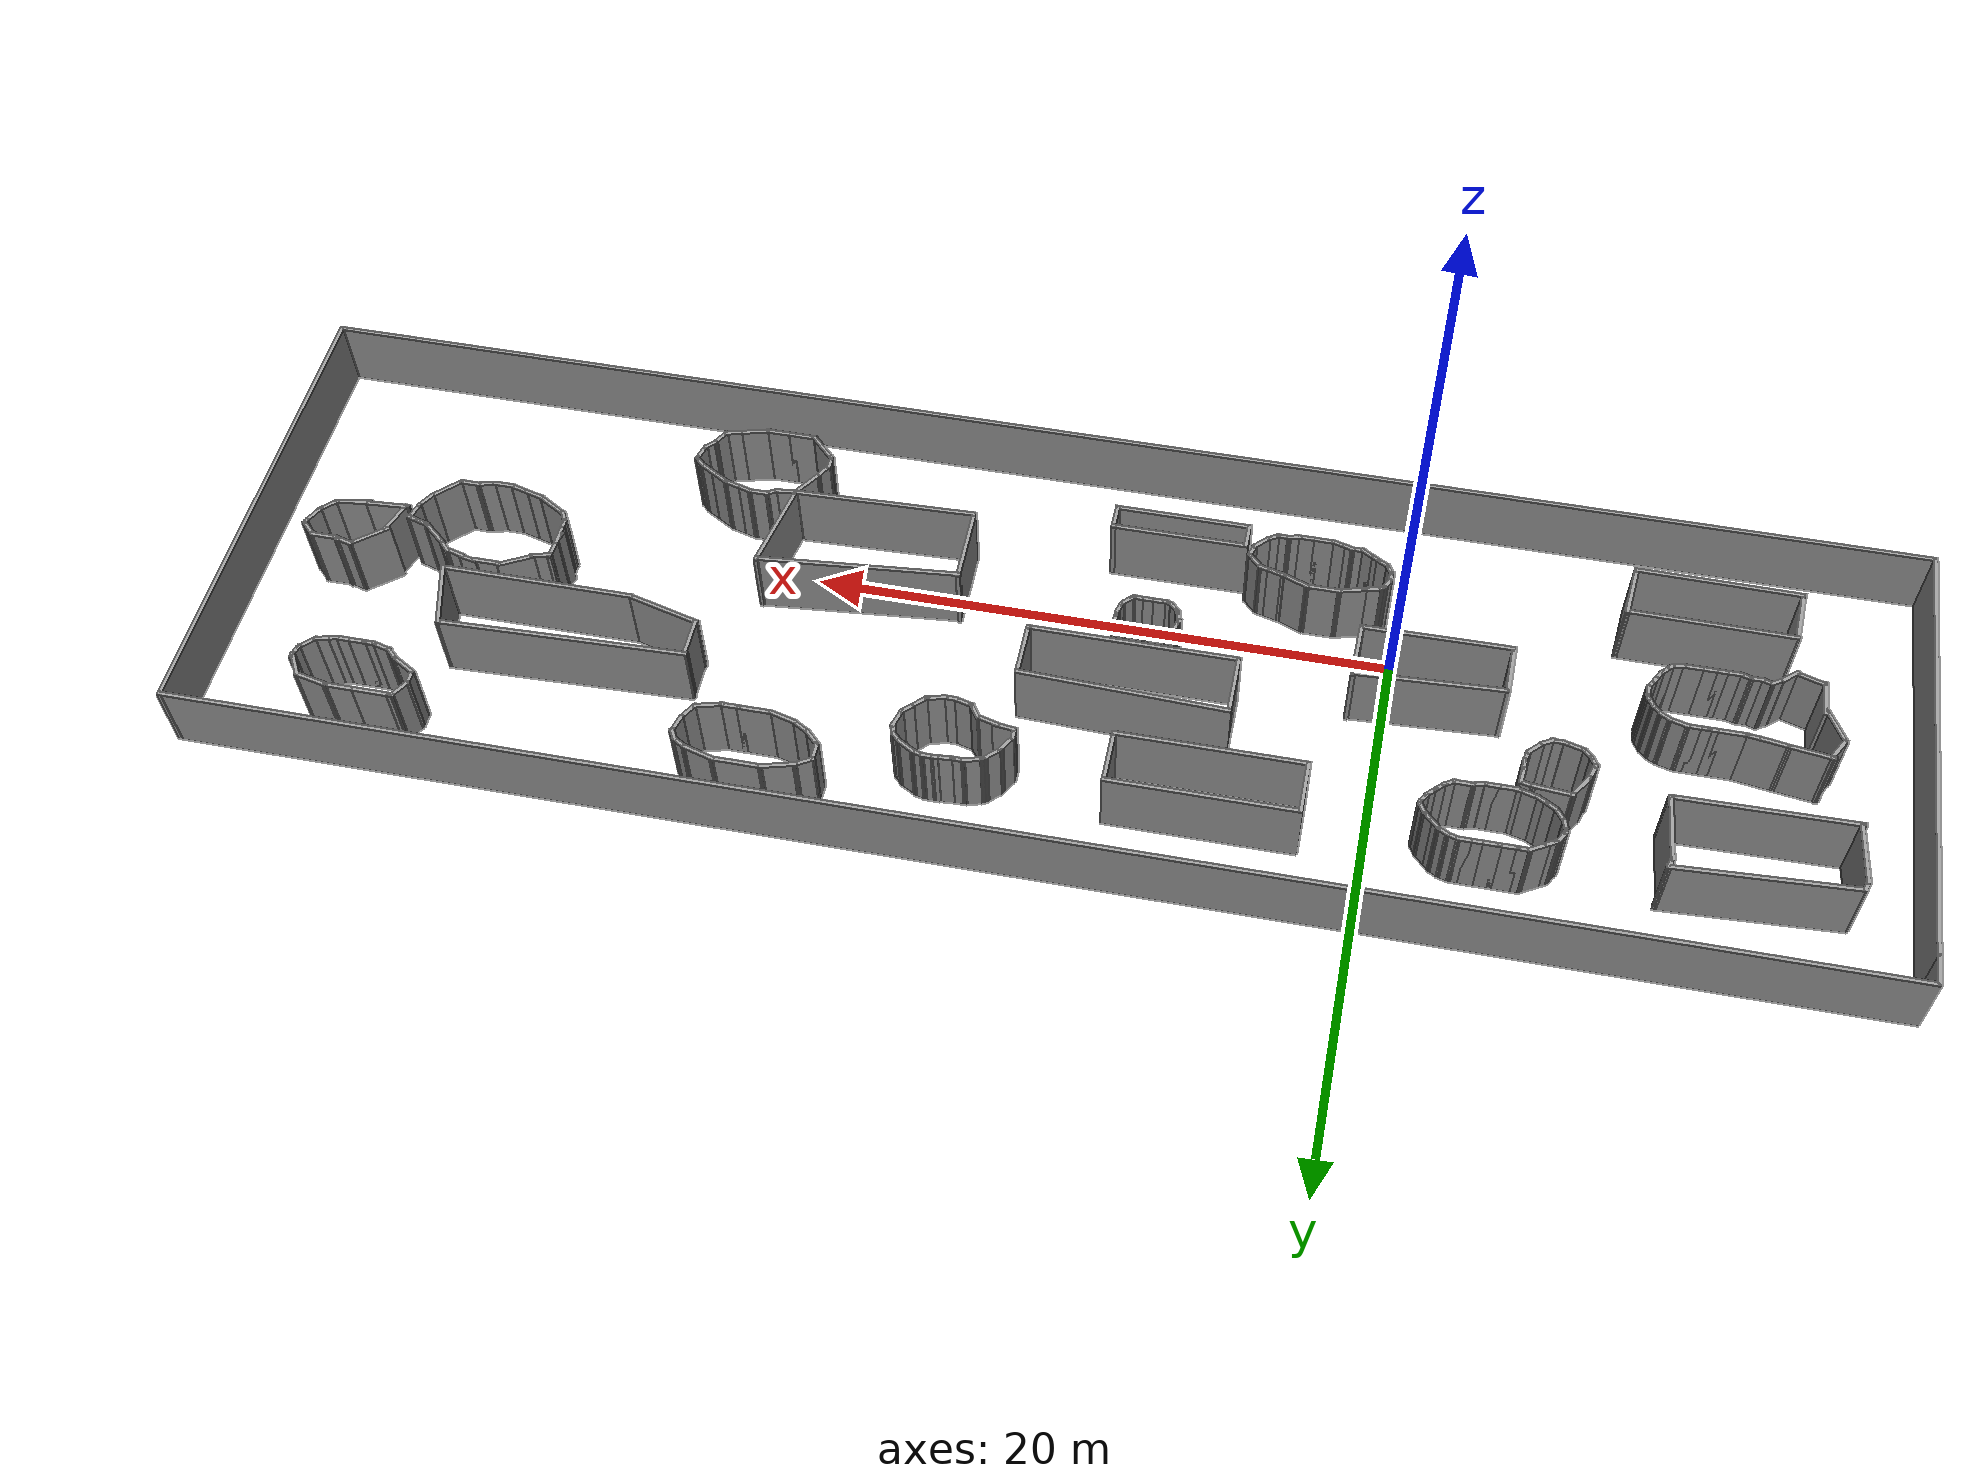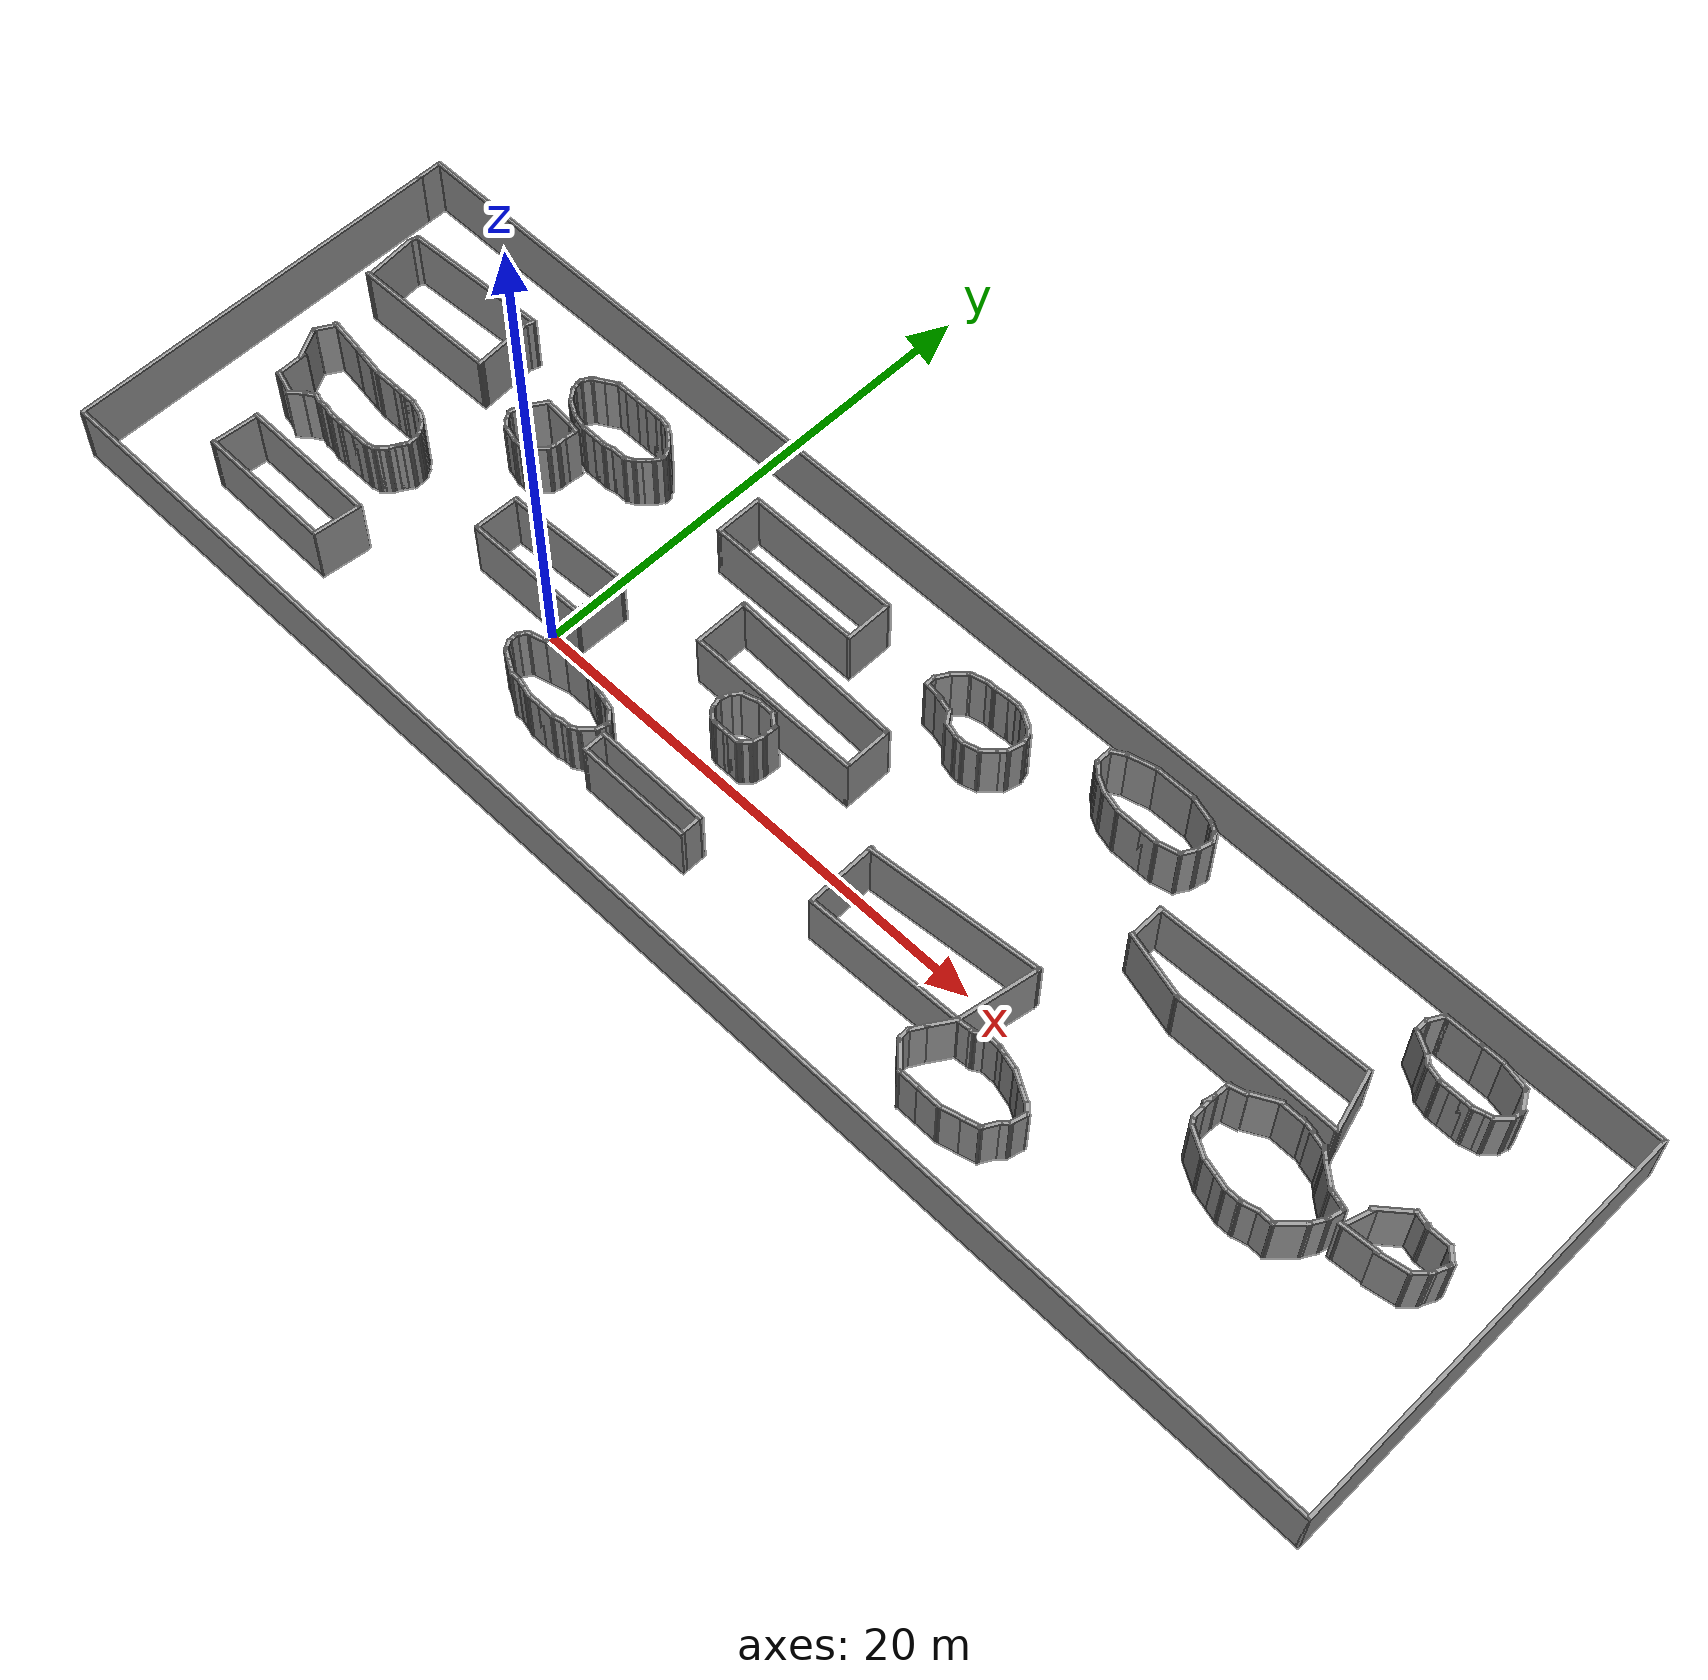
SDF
<?xml version='1.0'?>
<sdf version='1.7'>
  <model name='complex_wall'>
    <pose>10.8814 2.11175 0 0 -0 0</pose>
    <link name='Wall_100'>
      <collision name='Wall_100_Collision'>
        <geometry>
          <box>
            <size>0.5 0.15 2.5</size>
          </box>
        </geometry>
        <pose>0 0 1.25 0 -0 0</pose>
      </collision>
      <visual name='Wall_100_Visual'>
        <pose>0 0 1.25 0 -0 0</pose>
        <geometry>
          <box>
            <size>0.5 0.15 2.5</size>
          </box>
        </geometry>
        <material>
          <script>
            <uri>file://media/materials/scripts/gazebo.material</uri>
            <name>Gazebo/Grey</name>
          </script>
          <ambient>1 1 1 1</ambient>
        </material>
        <meta>
          <layer>0</layer>
        </meta>
      </visual>
      <pose>-19.3948 -0.52786 0 0 -0 2.0944</pose>
    </link>
    <link name='Wall_101'>
      <collision name='Wall_101_Collision'>
        <geometry>
          <box>
            <size>0.5 0.15 2.5</size>
          </box>
        </geometry>
        <pose>0 0 1.25 0 -0 0</pose>
      </collision>
      <visual name='Wall_101_Visual'>
        <pose>0 0 1.25 0 -0 0</pose>
        <geometry>
          <box>
            <size>0.5 0.15 2.5</size>
          </box>
        </geometry>
        <material>
          <script>
            <uri>file://media/materials/scripts/gazebo.material</uri>
            <name>Gazebo/Grey</name>
          </script>
          <ambient>1 1 1 1</ambient>
        </material>
        <meta>
          <layer>0</layer>
        </meta>
      </visual>
      <pose>-19.606 -0.252562 0 0 -0 2.35619</pose>
    </link>
    <link name='Wall_102'>
      <collision name='Wall_102_Collision'>
        <geometry>
          <box>
            <size>0.5 0.15 2.5</size>
          </box>
        </geometry>
        <pose>0 0 1.25 0 -0 0</pose>
      </collision>
      <visual name='Wall_102_Visual'>
        <pose>0 0 1.25 0 -0 0</pose>
        <geometry>
          <box>
            <size>0.5 0.15 2.5</size>
          </box>
        </geometry>
        <material>
          <script>
            <uri>file://media/materials/scripts/gazebo.material</uri>
            <name>Gazebo/Grey</name>
          </script>
          <ambient>1 1 1 1</ambient>
        </material>
        <meta>
          <layer>0</layer>
        </meta>
      </visual>
      <pose>-19.8813 -0.041319 0 0 -0 2.61799</pose>
    </link>
    <link name='Wall_103'>
      <collision name='Wall_103_Collision'>
        <geometry>
          <box>
            <size>0.75 0.15 2.5</size>
          </box>
        </geometry>
        <pose>0 0 1.25 0 -0 0</pose>
      </collision>
      <visual name='Wall_103_Visual'>
        <pose>0 0 1.25 0 -0 0</pose>
        <geometry>
          <box>
            <size>0.75 0.15 2.5</size>
          </box>
        </geometry>
        <material>
          <script>
            <uri>file://media/materials/scripts/gazebo.material</uri>
            <name>Gazebo/Grey</name>
          </script>
          <ambient>1 1 1 1</ambient>
        </material>
        <meta>
          <layer>0</layer>
        </meta>
      </visual>
      <pose>-20.3227 0.123827 0 0 -0 2.87979</pose>
    </link>
    <link name='Wall_104'>
      <collision name='Wall_104_Collision'>
        <geometry>
          <box>
            <size>0.5 0.15 2.5</size>
          </box>
        </geometry>
        <pose>0 0 1.25 0 -0 0</pose>
      </collision>
      <visual name='Wall_104_Visual'>
        <pose>0 0 1.25 0 -0 0</pose>
        <geometry>
          <box>
            <size>0.5 0.15 2.5</size>
          </box>
        </geometry>
        <material>
          <script>
            <uri>file://media/materials/scripts/gazebo.material</uri>
            <name>Gazebo/Grey</name>
          </script>
          <ambient>1 1 1 1</ambient>
        </material>
        <meta>
          <layer>0</layer>
        </meta>
      </visual>
      <pose>-20.7874 0.201473 0 0 -0 3.14159</pose>
    </link>
    <link name='Wall_105'>
      <collision name='Wall_105_Collision'>
        <geometry>
          <box>
            <size>0.5 0.15 2.5</size>
          </box>
        </geometry>
        <pose>0 0 1.25 0 -0 0</pose>
      </collision>
      <visual name='Wall_105_Visual'>
        <pose>0 0 1.25 0 -0 0</pose>
        <geometry>
          <box>
            <size>0.5 0.15 2.5</size>
          </box>
        </geometry>
        <material>
          <script>
            <uri>file://media/materials/scripts/gazebo.material</uri>
            <name>Gazebo/Grey</name>
          </script>
          <ambient>1 1 1 1</ambient>
        </material>
        <meta>
          <layer>0</layer>
        </meta>
      </visual>
      <pose>-21.1374 0.201473 0 0 -0 3.14159</pose>
    </link>
    <link name='Wall_106'>
      <collision name='Wall_106_Collision'>
        <geometry>
          <box>
            <size>0.5 0.15 2.5</size>
          </box>
        </geometry>
        <pose>0 0 1.25 0 -0 0</pose>
      </collision>
      <visual name='Wall_106_Visual'>
        <pose>0 0 1.25 0 -0 0</pose>
        <geometry>
          <box>
            <size>0.5 0.15 2.5</size>
          </box>
        </geometry>
        <material>
          <script>
            <uri>file://media/materials/scripts/gazebo.material</uri>
            <name>Gazebo/Grey</name>
          </script>
          <ambient>1 1 1 1</ambient>
        </material>
        <meta>
          <layer>0</layer>
        </meta>
      </visual>
      <pose>-21.4874 0.201473 0 0 -0 3.14159</pose>
    </link>
    <link name='Wall_107'>
      <collision name='Wall_107_Collision'>
        <geometry>
          <box>
            <size>1 0.15 2.5</size>
          </box>
        </geometry>
        <pose>0 0 1.25 0 -0 0</pose>
      </collision>
      <visual name='Wall_107_Visual'>
        <pose>0 0 1.25 0 -0 0</pose>
        <geometry>
          <box>
            <size>1 0.15 2.5</size>
          </box>
        </geometry>
        <material>
          <script>
            <uri>file://media/materials/scripts/gazebo.material</uri>
            <name>Gazebo/Grey</name>
          </script>
          <ambient>1 1 1 1</ambient>
        </material>
        <meta>
          <layer>0</layer>
        </meta>
      </visual>
      <pose>-22.0874 0.201473 0 0 -0 3.14159</pose>
    </link>
    <link name='Wall_111'>
      <collision name='Wall_111_Collision'>
        <geometry>
          <box>
            <size>1.61529 0.15 2.5</size>
          </box>
        </geometry>
        <pose>0 0 1.25 0 -0 0</pose>
      </collision>
      <visual name='Wall_111_Visual'>
        <pose>0 0 1.25 0 -0 0</pose>
        <geometry>
          <box>
            <size>1.61529 0.15 2.5</size>
          </box>
        </geometry>
        <material>
          <script>
            <uri>file://media/materials/scripts/gazebo.material</uri>
            <name>Gazebo/Grey</name>
          </script>
          <ambient>1 1 1 1</ambient>
        </material>
        <meta>
          <layer>0</layer>
        </meta>
      </visual>
      <pose>-24.5927 0.497103 0 0 -0 3.00766</pose>
    </link>
    <link name='Wall_112'>
      <collision name='Wall_112_Collision'>
        <geometry>
          <box>
            <size>0.15 0.15 2.5</size>
          </box>
        </geometry>
        <pose>0 0 1.25 0 -0 0</pose>
      </collision>
      <visual name='Wall_112_Visual'>
        <pose>0 0 1.25 0 -0 0</pose>
        <geometry>
          <box>
            <size>0.15 0.15 2.5</size>
          </box>
        </geometry>
        <material>
          <script>
            <uri>file://media/materials/scripts/gazebo.material</uri>
            <name>Gazebo/Grey</name>
          </script>
          <ambient>1 1 1 1</ambient>
        </material>
        <meta>
          <layer>0</layer>
        </meta>
      </visual>
      <pose>-25.3187 0.594936 0 0 -0 0</pose>
    </link>
    <link name='Wall_113'>
      <collision name='Wall_113_Collision'>
        <geometry>
          <box>
            <size>1 0.15 2.5</size>
          </box>
        </geometry>
        <pose>0 0 1.25 0 -0 0</pose>
      </collision>
      <visual name='Wall_113_Visual'>
        <pose>0 0 1.25 0 -0 0</pose>
        <geometry>
          <box>
            <size>1 0.15 2.5</size>
          </box>
        </geometry>
        <material>
          <script>
            <uri>file://media/materials/scripts/gazebo.material</uri>
            <name>Gazebo/Grey</name>
          </script>
          <ambient>1 1 1 1</ambient>
        </material>
        <meta>
          <layer>0</layer>
        </meta>
      </visual>
      <pose>-25.4386 0.226876 0 0 -0 -2.0944</pose>
    </link>
    <link name='Wall_114'>
      <collision name='Wall_114_Collision'>
        <geometry>
          <box>
            <size>1.44528 0.15 2.5</size>
          </box>
        </geometry>
        <pose>0 0 1.25 0 -0 0</pose>
      </collision>
      <visual name='Wall_114_Visual'>
        <pose>0 0 1.25 0 -0 0</pose>
        <geometry>
          <box>
            <size>1.44528 0.15 2.5</size>
          </box>
        </geometry>
        <material>
          <script>
            <uri>file://media/materials/scripts/gazebo.material</uri>
            <name>Gazebo/Grey</name>
          </script>
          <ambient>1 1 1 1</ambient>
        </material>
        <meta>
          <layer>0</layer>
        </meta>
      </visual>
      <pose>-25.3438 -0.711293 0 0 -0 -1.07646</pose>
    </link>
    <link name='Wall_117'>
      <collision name='Wall_117_Collision'>
        <geometry>
          <box>
            <size>1.34808 0.15 2.5</size>
          </box>
        </geometry>
        <pose>0 0 1.25 0 -0 0</pose>
      </collision>
      <visual name='Wall_117_Visual'>
        <pose>0 0 1.25 0 -0 0</pose>
        <geometry>
          <box>
            <size>1.34808 0.15 2.5</size>
          </box>
        </geometry>
        <material>
          <script>
            <uri>file://media/materials/scripts/gazebo.material</uri>
            <name>Gazebo/Grey</name>
          </script>
          <ambient>1 1 1 1</ambient>
        </material>
        <meta>
          <layer>0</layer>
        </meta>
      </visual>
      <pose>-24.9902 -1.76917 0 0 -0 -1.55537</pose>
    </link>
    <link name='Wall_118'>
      <collision name='Wall_118_Collision'>
        <geometry>
          <box>
            <size>1.09701 0.15 2.5</size>
          </box>
        </geometry>
        <pose>0 0 1.25 0 -0 0</pose>
      </collision>
      <visual name='Wall_118_Visual'>
        <pose>0 0 1.25 0 -0 0</pose>
        <geometry>
          <box>
            <size>1.09701 0.15 2.5</size>
          </box>
        </geometry>
        <material>
          <script>
            <uri>file://media/materials/scripts/gazebo.material</uri>
            <name>Gazebo/Grey</name>
          </script>
          <ambient>1 1 1 1</ambient>
        </material>
        <meta>
          <layer>0</layer>
        </meta>
      </visual>
      <pose>-24.5284 -2.47011 0 0 -0 -0.298026</pose>
    </link>
    <link name='Wall_120'>
      <collision name='Wall_120_Collision'>
        <geometry>
          <box>
            <size>1.91735 0.15 2.5</size>
          </box>
        </geometry>
        <pose>0 0 1.25 0 -0 0</pose>
      </collision>
      <visual name='Wall_120_Visual'>
        <pose>0 0 1.25 0 -0 0</pose>
        <geometry>
          <box>
            <size>1.91735 0.15 2.5</size>
          </box>
        </geometry>
        <material>
          <script>
            <uri>file://media/materials/scripts/gazebo.material</uri>
            <name>Gazebo/Grey</name>
          </script>
          <ambient>1 1 1 1</ambient>
        </material>
        <meta>
          <layer>0</layer>
        </meta>
      </visual>
      <pose>-14.791 -0.964174 0 0 -0 -1.59854</pose>
    </link>
    <link name='Wall_121'>
      <collision name='Wall_121_Collision'>
        <geometry>
          <box>
            <size>5.20588 0.15 2.5</size>
          </box>
        </geometry>
        <pose>0 0 1.25 0 -0 0</pose>
      </collision>
      <visual name='Wall_121_Visual'>
        <pose>0 0 1.25 0 -0 0</pose>
        <geometry>
          <box>
            <size>5.20588 0.15 2.5</size>
          </box>
        </geometry>
        <material>
          <script>
            <uri>file://media/materials/scripts/gazebo.material</uri>
            <name>Gazebo/Grey</name>
          </script>
          <ambient>1 1 1 1</ambient>
        </material>
        <meta>
          <layer>0</layer>
        </meta>
      </visual>
      <pose>-12.2631 -1.84751 0 0 -0 0.009695</pose>
    </link>
    <link name='Wall_122'>
      <collision name='Wall_122_Collision'>
        <geometry>
          <box>
            <size>2.16727 0.15 2.5</size>
          </box>
        </geometry>
        <pose>0 0 1.25 0 -0 0</pose>
      </collision>
      <visual name='Wall_122_Visual'>
        <pose>0 0 1.25 0 -0 0</pose>
        <geometry>
          <box>
            <size>2.16727 0.15 2.5</size>
          </box>
        </geometry>
        <material>
          <script>
            <uri>file://media/materials/scripts/gazebo.material</uri>
            <name>Gazebo/Grey</name>
          </script>
          <ambient>1 1 1 1</ambient>
        </material>
        <meta>
          <layer>0</layer>
        </meta>
      </visual>
      <pose>-9.7106 -0.814664 0 0 -0 1.54649</pose>
    </link>
    <link name='Wall_123'>
      <collision name='Wall_123_Collision'>
        <geometry>
          <box>
            <size>5.21205 0.15 2.5</size>
          </box>
        </geometry>
        <pose>0 0 1.25 0 -0 0</pose>
      </collision>
      <visual name='Wall_123_Visual'>
        <pose>0 0 1.25 0 -0 0</pose>
        <geometry>
          <box>
            <size>5.21205 0.15 2.5</size>
          </box>
        </geometry>
        <material>
          <script>
            <uri>file://media/materials/scripts/gazebo.material</uri>
            <name>Gazebo/Grey</name>
          </script>
          <ambient>1 1 1 1</ambient>
        </material>
        <meta>
          <layer>0</layer>
        </meta>
      </visual>
      <pose>-12.214 0.019653 0 0 -0 -3.09219</pose>
    </link>
    <link name='Wall_129'>
      <collision name='Wall_129_Collision'>
        <geometry>
          <box>
            <size>0.25 0.15 2.5</size>
          </box>
        </geometry>
        <pose>0 0 1.25 0 -0 0</pose>
      </collision>
      <visual name='Wall_129_Visual'>
        <pose>0 0 1.25 0 -0 0</pose>
        <geometry>
          <box>
            <size>0.25 0.15 2.5</size>
          </box>
        </geometry>
        <material>
          <script>
            <uri>file://media/materials/scripts/gazebo.material</uri>
            <name>Gazebo/Grey</name>
          </script>
          <ambient>1 1 1 1</ambient>
        </material>
        <meta>
          <layer>0</layer>
        </meta>
      </visual>
      <pose>-17.8126 2.40032 0 0 -0 -1.5708</pose>
    </link>
    <link name='Wall_130'>
      <collision name='Wall_130_Collision'>
        <geometry>
          <box>
            <size>0.5 0.15 2.5</size>
          </box>
        </geometry>
        <pose>0 0 1.25 0 -0 0</pose>
      </collision>
      <visual name='Wall_130_Visual'>
        <pose>0 0 1.25 0 -0 0</pose>
        <geometry>
          <box>
            <size>0.5 0.15 2.5</size>
          </box>
        </geometry>
        <material>
          <script>
            <uri>file://media/materials/scripts/gazebo.material</uri>
            <name>Gazebo/Grey</name>
          </script>
          <ambient>1 1 1 1</ambient>
        </material>
        <meta>
          <layer>0</layer>
        </meta>
      </visual>
      <pose>-17.7251 2.19877 0 0 -0 -1.0472</pose>
    </link>
    <link name='Wall_131'>
      <collision name='Wall_131_Collision'>
        <geometry>
          <box>
            <size>0.5 0.15 2.5</size>
          </box>
        </geometry>
        <pose>0 0 1.25 0 -0 0</pose>
      </collision>
      <visual name='Wall_131_Visual'>
        <pose>0 0 1.25 0 -0 0</pose>
        <geometry>
          <box>
            <size>0.5 0.15 2.5</size>
          </box>
        </geometry>
        <material>
          <script>
            <uri>file://media/materials/scripts/gazebo.material</uri>
            <name>Gazebo/Grey</name>
          </script>
          <ambient>1 1 1 1</ambient>
        </material>
        <meta>
          <layer>0</layer>
        </meta>
      </visual>
      <pose>-17.5139 1.92347 0 0 -0 -0.785398</pose>
    </link>
    <link name='Wall_132'>
      <collision name='Wall_132_Collision'>
        <geometry>
          <box>
            <size>0.75 0.15 2.5</size>
          </box>
        </geometry>
        <pose>0 0 1.25 0 -0 0</pose>
      </collision>
      <visual name='Wall_132_Visual'>
        <pose>0 0 1.25 0 -0 0</pose>
        <geometry>
          <box>
            <size>0.75 0.15 2.5</size>
          </box>
        </geometry>
        <material>
          <script>
            <uri>file://media/materials/scripts/gazebo.material</uri>
            <name>Gazebo/Grey</name>
          </script>
          <ambient>1 1 1 1</ambient>
        </material>
        <meta>
          <layer>0</layer>
        </meta>
      </visual>
      <pose>-17.1003 1.72208 0 0 -0 -0.261799</pose>
    </link>
    <link name='Wall_133'>
      <collision name='Wall_133_Collision'>
        <geometry>
          <box>
            <size>0.25 0.15 2.5</size>
          </box>
        </geometry>
        <pose>0 0 1.25 0 -0 0</pose>
      </collision>
      <visual name='Wall_133_Visual'>
        <pose>0 0 1.25 0 -0 0</pose>
        <geometry>
          <box>
            <size>0.25 0.15 2.5</size>
          </box>
        </geometry>
        <material>
          <script>
            <uri>file://media/materials/scripts/gazebo.material</uri>
            <name>Gazebo/Grey</name>
          </script>
          <ambient>1 1 1 1</ambient>
        </material>
        <meta>
          <layer>0</layer>
        </meta>
      </visual>
      <pose>-16.7623 1.63149 0 0 -0 -0.261799</pose>
    </link>
    <link name='Wall_134'>
      <collision name='Wall_134_Collision'>
        <geometry>
          <box>
            <size>0.5 0.15 2.5</size>
          </box>
        </geometry>
        <pose>0 0 1.25 0 -0 0</pose>
      </collision>
      <visual name='Wall_134_Visual'>
        <pose>0 0 1.25 0 -0 0</pose>
        <geometry>
          <box>
            <size>0.5 0.15 2.5</size>
          </box>
        </geometry>
        <material>
          <script>
            <uri>file://media/materials/scripts/gazebo.material</uri>
            <name>Gazebo/Grey</name>
          </script>
          <ambient>1 1 1 1</ambient>
        </material>
        <meta>
          <layer>0</layer>
        </meta>
      </visual>
      <pose>-16.539 1.61855 0 0 -0 0</pose>
    </link>
    <link name='Wall_135'>
      <collision name='Wall_135_Collision'>
        <geometry>
          <box>
            <size>0.5 0.15 2.5</size>
          </box>
        </geometry>
        <pose>0 0 1.25 0 -0 0</pose>
      </collision>
      <visual name='Wall_135_Visual'>
        <pose>0 0 1.25 0 -0 0</pose>
        <geometry>
          <box>
            <size>0.5 0.15 2.5</size>
          </box>
        </geometry>
        <material>
          <script>
            <uri>file://media/materials/scripts/gazebo.material</uri>
            <name>Gazebo/Grey</name>
          </script>
          <ambient>1 1 1 1</ambient>
        </material>
        <meta>
          <layer>0</layer>
        </meta>
      </visual>
      <pose>-16.2124 1.70606 0 0 -0 0.523599</pose>
    </link>
    <link name='Wall_136'>
      <collision name='Wall_136_Collision'>
        <geometry>
          <box>
            <size>0.75 0.15 2.5</size>
          </box>
        </geometry>
        <pose>0 0 1.25 0 -0 0</pose>
      </collision>
      <visual name='Wall_136_Visual'>
        <pose>0 0 1.25 0 -0 0</pose>
        <geometry>
          <box>
            <size>0.75 0.15 2.5</size>
          </box>
        </geometry>
        <material>
          <script>
            <uri>file://media/materials/scripts/gazebo.material</uri>
            <name>Gazebo/Grey</name>
          </script>
          <ambient>1 1 1 1</ambient>
        </material>
        <meta>
          <layer>0</layer>
        </meta>
      </visual>
      <pose>-15.8487 2.00569 0 0 -0 0.785398</pose>
    </link>
    <link name='Wall_137'>
      <collision name='Wall_137_Collision'>
        <geometry>
          <box>
            <size>0.5 0.15 2.5</size>
          </box>
        </geometry>
        <pose>0 0 1.25 0 -0 0</pose>
      </collision>
      <visual name='Wall_137_Visual'>
        <pose>0 0 1.25 0 -0 0</pose>
        <geometry>
          <box>
            <size>0.5 0.15 2.5</size>
          </box>
        </geometry>
        <material>
          <script>
            <uri>file://media/materials/scripts/gazebo.material</uri>
            <name>Gazebo/Grey</name>
          </script>
          <ambient>1 1 1 1</ambient>
        </material>
        <meta>
          <layer>0</layer>
        </meta>
      </visual>
      <pose>-15.5913 2.38686 0 0 -0 1.309</pose>
    </link>
    <link name='Wall_138'>
      <collision name='Wall_138_Collision'>
        <geometry>
          <box>
            <size>0.5 0.15 2.5</size>
          </box>
        </geometry>
        <pose>0 0 1.25 0 -0 0</pose>
      </collision>
      <visual name='Wall_138_Visual'>
        <pose>0 0 1.25 0 -0 0</pose>
        <geometry>
          <box>
            <size>0.5 0.15 2.5</size>
          </box>
        </geometry>
        <material>
          <script>
            <uri>file://media/materials/scripts/gazebo.material</uri>
            <name>Gazebo/Grey</name>
          </script>
          <ambient>1 1 1 1</ambient>
        </material>
        <meta>
          <layer>0</layer>
        </meta>
      </visual>
      <pose>-15.546 2.73089 0 0 -0 1.5708</pose>
    </link>
    <link name='Wall_139'>
      <collision name='Wall_139_Collision'>
        <geometry>
          <box>
            <size>0.661181 0.15 2.5</size>
          </box>
        </geometry>
        <pose>0 0 1.25 0 -0 0</pose>
      </collision>
      <visual name='Wall_139_Visual'>
        <pose>0 0 1.25 0 -0 0</pose>
        <geometry>
          <box>
            <size>0.661181 0.15 2.5</size>
          </box>
        </geometry>
        <material>
          <script>
            <uri>file://media/materials/scripts/gazebo.material</uri>
            <name>Gazebo/Grey</name>
          </script>
          <ambient>1 1 1 1</ambient>
        </material>
        <meta>
          <layer>0</layer>
        </meta>
      </visual>
      <pose>-15.5203 3.16018 0 0 -0 1.46988</pose>
    </link>
    <link name='Wall_140'>
      <collision name='Wall_140_Collision'>
        <geometry>
          <box>
            <size>0.521727 0.15 2.5</size>
          </box>
        </geometry>
        <pose>0 0 1.25 0 -0 0</pose>
      </collision>
      <visual name='Wall_140_Visual'>
        <pose>0 0 1.25 0 -0 0</pose>
        <geometry>
          <box>
            <size>0.521727 0.15 2.5</size>
          </box>
        </geometry>
        <material>
          <script>
            <uri>file://media/materials/scripts/gazebo.material</uri>
            <name>Gazebo/Grey</name>
          </script>
          <ambient>1 1 1 1</ambient>
        </material>
        <meta>
          <layer>0</layer>
        </meta>
      </visual>
      <pose>-15.7062 3.47397 0 0 -0 2.97356</pose>
    </link>
    <link name='Wall_144'>
      <collision name='Wall_144_Collision'>
        <geometry>
          <box>
            <size>0.15 0.15 2.5</size>
          </box>
        </geometry>
        <pose>0 0 1.25 0 -0 0</pose>
      </collision>
      <visual name='Wall_144_Visual'>
        <pose>0 0 1.25 0 -0 0</pose>
        <geometry>
          <box>
            <size>0.15 0.15 2.5</size>
          </box>
        </geometry>
        <material>
          <script>
            <uri>file://media/materials/scripts/gazebo.material</uri>
            <name>Gazebo/Grey</name>
          </script>
          <ambient>1 1 1 1</ambient>
        </material>
        <meta>
          <layer>0</layer>
        </meta>
      </visual>
      <pose>-17.1676 3.6136 0 0 -0 0</pose>
    </link>
    <link name='Wall_148'>
      <collision name='Wall_148_Collision'>
        <geometry>
          <box>
            <size>2.29146 0.15 2.5</size>
          </box>
        </geometry>
        <pose>0 0 1.25 0 -0 0</pose>
      </collision>
      <visual name='Wall_148_Visual'>
        <pose>0 0 1.25 0 -0 0</pose>
        <geometry>
          <box>
            <size>2.29146 0.15 2.5</size>
          </box>
        </geometry>
        <material>
          <script>
            <uri>file://media/materials/scripts/gazebo.material</uri>
            <name>Gazebo/Grey</name>
          </script>
          <ambient>1 1 1 1</ambient>
        </material>
        <meta>
          <layer>0</layer>
        </meta>
      </visual>
      <pose>-26.3129 4.07044 0 0 -0 -1.46971</pose>
    </link>
    <link name='Wall_149'>
      <collision name='Wall_149_Collision'>
        <geometry>
          <box>
            <size>6.21671 0.15 2.5</size>
          </box>
        </geometry>
        <pose>0 0 1.25 0 -0 0</pose>
      </collision>
      <visual name='Wall_149_Visual'>
        <pose>0 0 1.25 0 -0 0</pose>
        <geometry>
          <box>
            <size>6.21671 0.15 2.5</size>
          </box>
        </geometry>
        <material>
          <script>
            <uri>file://media/materials/scripts/gazebo.material</uri>
            <name>Gazebo/Grey</name>
          </script>
          <ambient>1 1 1 1</ambient>
        </material>
        <meta>
          <layer>0</layer>
        </meta>
      </visual>
      <pose>-23.2582 3.04839 0 0 -0 0.014249</pose>
    </link>
    <link name='Wall_150'>
      <collision name='Wall_150_Collision'>
        <geometry>
          <box>
            <size>2.51228 0.15 2.5</size>
          </box>
        </geometry>
        <pose>0 0 1.25 0 -0 0</pose>
      </collision>
      <visual name='Wall_150_Visual'>
        <pose>0 0 1.25 0 -0 0</pose>
        <geometry>
          <box>
            <size>2.51228 0.15 2.5</size>
          </box>
        </geometry>
        <material>
          <script>
            <uri>file://media/materials/scripts/gazebo.material</uri>
            <name>Gazebo/Grey</name>
          </script>
          <ambient>1 1 1 1</ambient>
        </material>
        <meta>
          <layer>0</layer>
        </meta>
      </visual>
      <pose>-20.3116 4.26959 0 0 -0 1.64404</pose>
    </link>
    <link name='Wall_151'>
      <collision name='Wall_151_Collision'>
        <geometry>
          <box>
            <size>6.18095 0.15 2.5</size>
          </box>
        </geometry>
        <pose>0 0 1.25 0 -0 0</pose>
      </collision>
      <visual name='Wall_151_Visual'>
        <pose>0 0 1.25 0 -0 0</pose>
        <geometry>
          <box>
            <size>6.18095 0.15 2.5</size>
          </box>
        </geometry>
        <material>
          <script>
            <uri>file://media/materials/scripts/gazebo.material</uri>
            <name>Gazebo/Grey</name>
          </script>
          <ambient>1 1 1 1</ambient>
        </material>
        <meta>
          <layer>0</layer>
        </meta>
      </visual>
      <pose>-23.3231 5.59417 0 0 -0 -3.08986</pose>
    </link>
    <link name='Wall_153'>
      <collision name='Wall_153_Collision'>
        <geometry>
          <box>
            <size>0.5 0.15 2.5</size>
          </box>
        </geometry>
        <pose>0 0 1.25 0 -0 0</pose>
      </collision>
      <visual name='Wall_153_Visual'>
        <pose>0 0 1.25 0 -0 0</pose>
        <geometry>
          <box>
            <size>0.5 0.15 2.5</size>
          </box>
        </geometry>
        <material>
          <script>
            <uri>file://media/materials/scripts/gazebo.material</uri>
            <name>Gazebo/Grey</name>
          </script>
          <ambient>1 1 1 1</ambient>
        </material>
        <meta>
          <layer>0</layer>
        </meta>
      </visual>
      <pose>-16.5234 4.17445 0 0 -0 -0.523599</pose>
    </link>
    <link name='Wall_154'>
      <collision name='Wall_154_Collision'>
        <geometry>
          <box>
            <size>0.5 0.15 2.5</size>
          </box>
        </geometry>
        <pose>0 0 1.25 0 -0 0</pose>
      </collision>
      <visual name='Wall_154_Visual'>
        <pose>0 0 1.25 0 -0 0</pose>
        <geometry>
          <box>
            <size>0.5 0.15 2.5</size>
          </box>
        </geometry>
        <material>
          <script>
            <uri>file://media/materials/scripts/gazebo.material</uri>
            <name>Gazebo/Grey</name>
          </script>
          <ambient>1 1 1 1</ambient>
        </material>
        <meta>
          <layer>0</layer>
        </meta>
      </visual>
      <pose>-16.2203 3.99945 0 0 -0 -0.523599</pose>
    </link>
    <link name='Wall_155'>
      <collision name='Wall_155_Collision'>
        <geometry>
          <box>
            <size>0.75 0.15 2.5</size>
          </box>
        </geometry>
        <pose>0 0 1.25 0 -0 0</pose>
      </collision>
      <visual name='Wall_155_Visual'>
        <pose>0 0 1.25 0 -0 0</pose>
        <geometry>
          <box>
            <size>0.75 0.15 2.5</size>
          </box>
        </geometry>
        <material>
          <script>
            <uri>file://media/materials/scripts/gazebo.material</uri>
            <name>Gazebo/Grey</name>
          </script>
          <ambient>1 1 1 1</ambient>
        </material>
        <meta>
          <layer>0</layer>
        </meta>
      </visual>
      <pose>-15.7789 3.83431 0 0 -0 -0.261799</pose>
    </link>
    <link name='Wall_156'>
      <collision name='Wall_156_Collision'>
        <geometry>
          <box>
            <size>0.25 0.15 2.5</size>
          </box>
        </geometry>
        <pose>0 0 1.25 0 -0 0</pose>
      </collision>
      <visual name='Wall_156_Visual'>
        <pose>0 0 1.25 0 -0 0</pose>
        <geometry>
          <box>
            <size>0.25 0.15 2.5</size>
          </box>
        </geometry>
        <material>
          <script>
            <uri>file://media/materials/scripts/gazebo.material</uri>
            <name>Gazebo/Grey</name>
          </script>
          <ambient>1 1 1 1</ambient>
        </material>
        <meta>
          <layer>0</layer>
        </meta>
      </visual>
      <pose>-15.4408 3.74372 0 0 -0 -0.261799</pose>
    </link>
    <link name='Wall_157'>
      <collision name='Wall_157_Collision'>
        <geometry>
          <box>
            <size>0.75 0.15 2.5</size>
          </box>
        </geometry>
        <pose>0 0 1.25 0 -0 0</pose>
      </collision>
      <visual name='Wall_157_Visual'>
        <pose>0 0 1.25 0 -0 0</pose>
        <geometry>
          <box>
            <size>0.75 0.15 2.5</size>
          </box>
        </geometry>
        <material>
          <script>
            <uri>file://media/materials/scripts/gazebo.material</uri>
            <name>Gazebo/Grey</name>
          </script>
          <ambient>1 1 1 1</ambient>
        </material>
        <meta>
          <layer>0</layer>
        </meta>
      </visual>
      <pose>-15.0926 3.73078 0 0 -0 0</pose>
    </link>
    <link name='Wall_158'>
      <collision name='Wall_158_Collision'>
        <geometry>
          <box>
            <size>0.5 0.15 2.5</size>
          </box>
        </geometry>
        <pose>0 0 1.25 0 -0 0</pose>
      </collision>
      <visual name='Wall_158_Visual'>
        <pose>0 0 1.25 0 -0 0</pose>
        <geometry>
          <box>
            <size>0.5 0.15 2.5</size>
          </box>
        </geometry>
        <material>
          <script>
            <uri>file://media/materials/scripts/gazebo.material</uri>
            <name>Gazebo/Grey</name>
          </script>
          <ambient>1 1 1 1</ambient>
        </material>
        <meta>
          <layer>0</layer>
        </meta>
      </visual>
      <pose>-14.6176 3.73078 0 0 -0 0</pose>
    </link>
    <link name='Wall_159'>
      <collision name='Wall_159_Collision'>
        <geometry>
          <box>
            <size>0.25 0.15 2.5</size>
          </box>
        </geometry>
        <pose>0 0 1.25 0 -0 0</pose>
      </collision>
      <visual name='Wall_159_Visual'>
        <pose>0 0 1.25 0 -0 0</pose>
        <geometry>
          <box>
            <size>0.25 0.15 2.5</size>
          </box>
        </geometry>
        <material>
          <script>
            <uri>file://media/materials/scripts/gazebo.material</uri>
            <name>Gazebo/Grey</name>
          </script>
          <ambient>1 1 1 1</ambient>
        </material>
        <meta>
          <layer>0</layer>
        </meta>
      </visual>
      <pose>-14.3926 3.73078 0 0 -0 0</pose>
    </link>
    <link name='Wall_160'>
      <collision name='Wall_160_Collision'>
        <geometry>
          <box>
            <size>0.5 0.15 2.5</size>
          </box>
        </geometry>
        <pose>0 0 1.25 0 -0 0</pose>
      </collision>
      <visual name='Wall_160_Visual'>
        <pose>0 0 1.25 0 -0 0</pose>
        <geometry>
          <box>
            <size>0.5 0.15 2.5</size>
          </box>
        </geometry>
        <material>
          <script>
            <uri>file://media/materials/scripts/gazebo.material</uri>
            <name>Gazebo/Grey</name>
          </script>
          <ambient>1 1 1 1</ambient>
        </material>
        <meta>
          <layer>0</layer>
        </meta>
      </visual>
      <pose>-14.1735 3.77607 0 0 -0 0.261799</pose>
    </link>
    <link name='Wall_161'>
      <collision name='Wall_161_Collision'>
        <geometry>
          <box>
            <size>0.15 0.15 2.5</size>
          </box>
        </geometry>
        <pose>0 0 1.25 0 -0 0</pose>
      </collision>
      <visual name='Wall_161_Visual'>
        <pose>0 0 1.25 0 -0 0</pose>
        <geometry>
          <box>
            <size>0.15 0.15 2.5</size>
          </box>
        </geometry>
        <material>
          <script>
            <uri>file://media/materials/scripts/gazebo.material</uri>
            <name>Gazebo/Grey</name>
          </script>
          <ambient>1 1 1 1</ambient>
        </material>
        <meta>
          <layer>0</layer>
        </meta>
      </visual>
      <pose>-14.0045 3.82137 0 0 -0 0</pose>
    </link>
    <link name='Wall_162'>
      <collision name='Wall_162_Collision'>
        <geometry>
          <box>
            <size>0.75 0.15 2.5</size>
          </box>
        </geometry>
        <pose>0 0 1.25 0 -0 0</pose>
      </collision>
      <visual name='Wall_162_Visual'>
        <pose>0 0 1.25 0 -0 0</pose>
        <geometry>
          <box>
            <size>0.75 0.15 2.5</size>
          </box>
        </geometry>
        <material>
          <script>
            <uri>file://media/materials/scripts/gazebo.material</uri>
            <name>Gazebo/Grey</name>
          </script>
          <ambient>1 1 1 1</ambient>
        </material>
        <meta>
          <layer>0</layer>
        </meta>
      </visual>
      <pose>-13.7045 3.82137 0 0 -0 0</pose>
    </link>
    <link name='Wall_163'>
      <collision name='Wall_163_Collision'>
        <geometry>
          <box>
            <size>0.5 0.15 2.5</size>
          </box>
        </geometry>
        <pose>0 0 1.25 0 -0 0</pose>
      </collision>
      <visual name='Wall_163_Visual'>
        <pose>0 0 1.25 0 -0 0</pose>
        <geometry>
          <box>
            <size>0.5 0.15 2.5</size>
          </box>
        </geometry>
        <material>
          <script>
            <uri>file://media/materials/scripts/gazebo.material</uri>
            <name>Gazebo/Grey</name>
          </script>
          <ambient>1 1 1 1</ambient>
        </material>
        <meta>
          <layer>0</layer>
        </meta>
      </visual>
      <pose>-13.2529 3.90887 0 0 -0 0.523599</pose>
    </link>
    <link name='Wall_164'>
      <collision name='Wall_164_Collision'>
        <geometry>
          <box>
            <size>0.5 0.15 2.5</size>
          </box>
        </geometry>
        <pose>0 0 1.25 0 -0 0</pose>
      </collision>
      <visual name='Wall_164_Visual'>
        <pose>0 0 1.25 0 -0 0</pose>
        <geometry>
          <box>
            <size>0.5 0.15 2.5</size>
          </box>
        </geometry>
        <material>
          <script>
            <uri>file://media/materials/scripts/gazebo.material</uri>
            <name>Gazebo/Grey</name>
          </script>
          <ambient>1 1 1 1</ambient>
        </material>
        <meta>
          <layer>0</layer>
        </meta>
      </visual>
      <pose>-12.9776 4.12011 0 0 -0 0.785398</pose>
    </link>
    <link name='Wall_165'>
      <collision name='Wall_165_Collision'>
        <geometry>
          <box>
            <size>0.5 0.15 2.5</size>
          </box>
        </geometry>
        <pose>0 0 1.25 0 -0 0</pose>
      </collision>
      <visual name='Wall_165_Visual'>
        <pose>0 0 1.25 0 -0 0</pose>
        <geometry>
          <box>
            <size>0.5 0.15 2.5</size>
          </box>
        </geometry>
        <material>
          <script>
            <uri>file://media/materials/scripts/gazebo.material</uri>
            <name>Gazebo/Grey</name>
          </script>
          <ambient>1 1 1 1</ambient>
        </material>
        <meta>
          <layer>0</layer>
        </meta>
      </visual>
      <pose>-12.7301 4.3676 0 0 -0 0.785398</pose>
    </link>
    <link name='Wall_166'>
      <collision name='Wall_166_Collision'>
        <geometry>
          <box>
            <size>0.5 0.15 2.5</size>
          </box>
        </geometry>
        <pose>0 0 1.25 0 -0 0</pose>
      </collision>
      <visual name='Wall_166_Visual'>
        <pose>0 0 1.25 0 -0 0</pose>
        <geometry>
          <box>
            <size>0.5 0.15 2.5</size>
          </box>
        </geometry>
        <material>
          <script>
            <uri>file://media/materials/scripts/gazebo.material</uri>
            <name>Gazebo/Grey</name>
          </script>
          <ambient>1 1 1 1</ambient>
        </material>
        <meta>
          <layer>0</layer>
        </meta>
      </visual>
      <pose>-12.5189 4.6429 0 0 -0 1.0472</pose>
    </link>
    <link name='Wall_167'>
      <collision name='Wall_167_Collision'>
        <geometry>
          <box>
            <size>0.25 0.15 2.5</size>
          </box>
        </geometry>
        <pose>0 0 1.25 0 -0 0</pose>
      </collision>
      <visual name='Wall_167_Visual'>
        <pose>0 0 1.25 0 -0 0</pose>
        <geometry>
          <box>
            <size>0.25 0.15 2.5</size>
          </box>
        </geometry>
        <material>
          <script>
            <uri>file://media/materials/scripts/gazebo.material</uri>
            <name>Gazebo/Grey</name>
          </script>
          <ambient>1 1 1 1</ambient>
        </material>
        <meta>
          <layer>0</layer>
        </meta>
      </visual>
      <pose>-12.4314 4.84445 0 0 -0 1.5708</pose>
    </link>
    <link name='Wall_168'>
      <collision name='Wall_168_Collision'>
        <geometry>
          <box>
            <size>0.5 0.15 2.5</size>
          </box>
        </geometry>
        <pose>0 0 1.25 0 -0 0</pose>
      </collision>
      <visual name='Wall_168_Visual'>
        <pose>0 0 1.25 0 -0 0</pose>
        <geometry>
          <box>
            <size>0.5 0.15 2.5</size>
          </box>
        </geometry>
        <material>
          <script>
            <uri>file://media/materials/scripts/gazebo.material</uri>
            <name>Gazebo/Grey</name>
          </script>
          <ambient>1 1 1 1</ambient>
        </material>
        <meta>
          <layer>0</layer>
        </meta>
      </visual>
      <pose>-12.5189 5.04601 0 0 -0 2.0944</pose>
    </link>
    <link name='Wall_169'>
      <collision name='Wall_169_Collision'>
        <geometry>
          <box>
            <size>0.5 0.15 2.5</size>
          </box>
        </geometry>
        <pose>0 0 1.25 0 -0 0</pose>
      </collision>
      <visual name='Wall_169_Visual'>
        <pose>0 0 1.25 0 -0 0</pose>
        <geometry>
          <box>
            <size>0.5 0.15 2.5</size>
          </box>
        </geometry>
        <material>
          <script>
            <uri>file://media/materials/scripts/gazebo.material</uri>
            <name>Gazebo/Grey</name>
          </script>
          <ambient>1 1 1 1</ambient>
        </material>
        <meta>
          <layer>0</layer>
        </meta>
      </visual>
      <pose>-12.7301 5.3213 0 0 -0 2.35619</pose>
    </link>
    <link name='Wall_170'>
      <collision name='Wall_170_Collision'>
        <geometry>
          <box>
            <size>0.5 0.15 2.5</size>
          </box>
        </geometry>
        <pose>0 0 1.25 0 -0 0</pose>
      </collision>
      <visual name='Wall_170_Visual'>
        <pose>0 0 1.25 0 -0 0</pose>
        <geometry>
          <box>
            <size>0.5 0.15 2.5</size>
          </box>
        </geometry>
        <material>
          <script>
            <uri>file://media/materials/scripts/gazebo.material</uri>
            <name>Gazebo/Grey</name>
          </script>
          <ambient>1 1 1 1</ambient>
        </material>
        <meta>
          <layer>0</layer>
        </meta>
      </visual>
      <pose>-12.9776 5.56879 0 0 -0 2.35619</pose>
    </link>
    <link name='Wall_171'>
      <collision name='Wall_171_Collision'>
        <geometry>
          <box>
            <size>0.5 0.15 2.5</size>
          </box>
        </geometry>
        <pose>0 0 1.25 0 -0 0</pose>
      </collision>
      <visual name='Wall_171_Visual'>
        <pose>0 0 1.25 0 -0 0</pose>
        <geometry>
          <box>
            <size>0.5 0.15 2.5</size>
          </box>
        </geometry>
        <material>
          <script>
            <uri>file://media/materials/scripts/gazebo.material</uri>
            <name>Gazebo/Grey</name>
          </script>
          <ambient>1 1 1 1</ambient>
        </material>
        <meta>
          <layer>0</layer>
        </meta>
      </visual>
      <pose>-13.2529 5.78003 0 0 -0 2.61799</pose>
    </link>
    <link name='Wall_172'>
      <collision name='Wall_172_Collision'>
        <geometry>
          <box>
            <size>0.5 0.15 2.5</size>
          </box>
        </geometry>
        <pose>0 0 1.25 0 -0 0</pose>
      </collision>
      <visual name='Wall_172_Visual'>
        <pose>0 0 1.25 0 -0 0</pose>
        <geometry>
          <box>
            <size>0.5 0.15 2.5</size>
          </box>
        </geometry>
        <material>
          <script>
            <uri>file://media/materials/scripts/gazebo.material</uri>
            <name>Gazebo/Grey</name>
          </script>
          <ambient>1 1 1 1</ambient>
        </material>
        <meta>
          <layer>0</layer>
        </meta>
      </visual>
      <pose>-13.5735 5.91283 0 0 -0 2.87979</pose>
    </link>
    <link name='Wall_173'>
      <collision name='Wall_173_Collision'>
        <geometry>
          <box>
            <size>0.5 0.15 2.5</size>
          </box>
        </geometry>
        <pose>0 0 1.25 0 -0 0</pose>
      </collision>
      <visual name='Wall_173_Visual'>
        <pose>0 0 1.25 0 -0 0</pose>
        <geometry>
          <box>
            <size>0.5 0.15 2.5</size>
          </box>
        </geometry>
        <material>
          <script>
            <uri>file://media/materials/scripts/gazebo.material</uri>
            <name>Gazebo/Grey</name>
          </script>
          <ambient>1 1 1 1</ambient>
        </material>
        <meta>
          <layer>0</layer>
        </meta>
      </visual>
      <pose>-13.9176 5.95812 0 0 -0 3.14159</pose>
    </link>
    <link name='Wall_174'>
      <collision name='Wall_174_Collision'>
        <geometry>
          <box>
            <size>0.5 0.15 2.5</size>
          </box>
        </geometry>
        <pose>0 0 1.25 0 -0 0</pose>
      </collision>
      <visual name='Wall_174_Visual'>
        <pose>0 0 1.25 0 -0 0</pose>
        <geometry>
          <box>
            <size>0.5 0.15 2.5</size>
          </box>
        </geometry>
        <material>
          <script>
            <uri>file://media/materials/scripts/gazebo.material</uri>
            <name>Gazebo/Grey</name>
          </script>
          <ambient>1 1 1 1</ambient>
        </material>
        <meta>
          <layer>0</layer>
        </meta>
      </visual>
      <pose>-14.2676 5.95812 0 0 -0 3.14159</pose>
    </link>
    <link name='Wall_175'>
      <collision name='Wall_175_Collision'>
        <geometry>
          <box>
            <size>0.75 0.15 2.5</size>
          </box>
        </geometry>
        <pose>0 0 1.25 0 -0 0</pose>
      </collision>
      <visual name='Wall_175_Visual'>
        <pose>0 0 1.25 0 -0 0</pose>
        <geometry>
          <box>
            <size>0.75 0.15 2.5</size>
          </box>
        </geometry>
        <material>
          <script>
            <uri>file://media/materials/scripts/gazebo.material</uri>
            <name>Gazebo/Grey</name>
          </script>
          <ambient>1 1 1 1</ambient>
        </material>
        <meta>
          <layer>0</layer>
        </meta>
      </visual>
      <pose>-14.7426 5.95812 0 0 -0 3.14159</pose>
    </link>
    <link name='Wall_176'>
      <collision name='Wall_176_Collision'>
        <geometry>
          <box>
            <size>0.75 0.15 2.5</size>
          </box>
        </geometry>
        <pose>0 0 1.25 0 -0 0</pose>
      </collision>
      <visual name='Wall_176_Visual'>
        <pose>0 0 1.25 0 -0 0</pose>
        <geometry>
          <box>
            <size>0.75 0.15 2.5</size>
          </box>
        </geometry>
        <material>
          <script>
            <uri>file://media/materials/scripts/gazebo.material</uri>
            <name>Gazebo/Grey</name>
          </script>
          <ambient>1 1 1 1</ambient>
        </material>
        <meta>
          <layer>0</layer>
        </meta>
      </visual>
      <pose>-15.3426 5.95812 0 0 -0 3.14159</pose>
    </link>
    <link name='Wall_177'>
      <collision name='Wall_177_Collision'>
        <geometry>
          <box>
            <size>0.5 0.15 2.5</size>
          </box>
        </geometry>
        <pose>0 0 1.25 0 -0 0</pose>
      </collision>
      <visual name='Wall_177_Visual'>
        <pose>0 0 1.25 0 -0 0</pose>
        <geometry>
          <box>
            <size>0.5 0.15 2.5</size>
          </box>
        </geometry>
        <material>
          <script>
            <uri>file://media/materials/scripts/gazebo.material</uri>
            <name>Gazebo/Grey</name>
          </script>
          <ambient>1 1 1 1</ambient>
        </material>
        <meta>
          <layer>0</layer>
        </meta>
      </visual>
      <pose>-15.8176 5.95812 0 0 -0 3.14159</pose>
    </link>
    <link name='Wall_178'>
      <collision name='Wall_178_Collision'>
        <geometry>
          <box>
            <size>0.75 0.15 2.5</size>
          </box>
        </geometry>
        <pose>0 0 1.25 0 -0 0</pose>
      </collision>
      <visual name='Wall_178_Visual'>
        <pose>0 0 1.25 0 -0 0</pose>
        <geometry>
          <box>
            <size>0.75 0.15 2.5</size>
          </box>
        </geometry>
        <material>
          <script>
            <uri>file://media/materials/scripts/gazebo.material</uri>
            <name>Gazebo/Grey</name>
          </script>
          <ambient>1 1 1 1</ambient>
        </material>
        <meta>
          <layer>0</layer>
        </meta>
      </visual>
      <pose>-16.2524 5.80812 0 0 -0 -2.61799</pose>
    </link>
    <link name='Wall_179'>
      <collision name='Wall_179_Collision'>
        <geometry>
          <box>
            <size>0.5 0.15 2.5</size>
          </box>
        </geometry>
        <pose>0 0 1.25 0 -0 0</pose>
      </collision>
      <visual name='Wall_179_Visual'>
        <pose>0 0 1.25 0 -0 0</pose>
        <geometry>
          <box>
            <size>0.5 0.15 2.5</size>
          </box>
        </geometry>
        <material>
          <script>
            <uri>file://media/materials/scripts/gazebo.material</uri>
            <name>Gazebo/Grey</name>
          </script>
          <ambient>1 1 1 1</ambient>
        </material>
        <meta>
          <layer>0</layer>
        </meta>
      </visual>
      <pose>-16.6637 5.57062 0 0 -0 -2.61799</pose>
    </link>
    <link name='Wall_180'>
      <collision name='Wall_180_Collision'>
        <geometry>
          <box>
            <size>0.25 0.15 2.5</size>
          </box>
        </geometry>
        <pose>0 0 1.25 0 -0 0</pose>
      </collision>
      <visual name='Wall_180_Visual'>
        <pose>0 0 1.25 0 -0 0</pose>
        <geometry>
          <box>
            <size>0.25 0.15 2.5</size>
          </box>
        </geometry>
        <material>
          <script>
            <uri>file://media/materials/scripts/gazebo.material</uri>
            <name>Gazebo/Grey</name>
          </script>
          <ambient>1 1 1 1</ambient>
        </material>
        <meta>
          <layer>0</layer>
        </meta>
      </visual>
      <pose>-16.8506 5.44777 0 0 -0 -2.35619</pose>
    </link>
    <link name='Wall_181'>
      <collision name='Wall_181_Collision'>
        <geometry>
          <box>
            <size>0.5 0.15 2.5</size>
          </box>
        </geometry>
        <pose>0 0 1.25 0 -0 0</pose>
      </collision>
      <visual name='Wall_181_Visual'>
        <pose>0 0 1.25 0 -0 0</pose>
        <geometry>
          <box>
            <size>0.5 0.15 2.5</size>
          </box>
        </geometry>
        <material>
          <script>
            <uri>file://media/materials/scripts/gazebo.material</uri>
            <name>Gazebo/Grey</name>
          </script>
          <ambient>1 1 1 1</ambient>
        </material>
        <meta>
          <layer>0</layer>
        </meta>
      </visual>
      <pose>-16.9735 5.26086 0 0 -0 -2.0944</pose>
    </link>
    <link name='Wall_182'>
      <collision name='Wall_182_Collision'>
        <geometry>
          <box>
            <size>0.15 0.15 2.5</size>
          </box>
        </geometry>
        <pose>0 0 1.25 0 -0 0</pose>
      </collision>
      <visual name='Wall_182_Visual'>
        <pose>0 0 1.25 0 -0 0</pose>
        <geometry>
          <box>
            <size>0.15 0.15 2.5</size>
          </box>
        </geometry>
        <material>
          <script>
            <uri>file://media/materials/scripts/gazebo.material</uri>
            <name>Gazebo/Grey</name>
          </script>
          <ambient>1 1 1 1</ambient>
        </material>
        <meta>
          <layer>0</layer>
        </meta>
      </visual>
      <pose>-17.061 5.1093 0 0 -0 0</pose>
    </link>
    <link name='Wall_183'>
      <collision name='Wall_183_Collision'>
        <geometry>
          <box>
            <size>0.25 0.15 2.5</size>
          </box>
        </geometry>
        <pose>0 0 1.25 0 -0 0</pose>
      </collision>
      <visual name='Wall_183_Visual'>
        <pose>0 0 1.25 0 -0 0</pose>
        <geometry>
          <box>
            <size>0.25 0.15 2.5</size>
          </box>
        </geometry>
        <material>
          <script>
            <uri>file://media/materials/scripts/gazebo.material</uri>
            <name>Gazebo/Grey</name>
          </script>
          <ambient>1 1 1 1</ambient>
        </material>
        <meta>
          <layer>0</layer>
        </meta>
      </visual>
      <pose>-17.061 5.0593 0 0 -0 -1.5708</pose>
    </link>
    <link name='Wall_184'>
      <collision name='Wall_184_Collision'>
        <geometry>
          <box>
            <size>0.5 0.15 2.5</size>
          </box>
        </geometry>
        <pose>0 0 1.25 0 -0 0</pose>
      </collision>
      <visual name='Wall_184_Visual'>
        <pose>0 0 1.25 0 -0 0</pose>
        <geometry>
          <box>
            <size>0.5 0.15 2.5</size>
          </box>
        </geometry>
        <material>
          <script>
            <uri>file://media/materials/scripts/gazebo.material</uri>
            <name>Gazebo/Grey</name>
          </script>
          <ambient>1 1 1 1</ambient>
        </material>
        <meta>
          <layer>0</layer>
        </meta>
      </visual>
      <pose>-17.0157 4.84026 0 0 -0 -1.309</pose>
    </link>
    <link name='Wall_185'>
      <collision name='Wall_185_Collision'>
        <geometry>
          <box>
            <size>0.654792 0.15 2.5</size>
          </box>
        </geometry>
        <pose>0 0 1.25 0 -0 0</pose>
      </collision>
      <visual name='Wall_185_Visual'>
        <pose>0 0 1.25 0 -0 0</pose>
        <geometry>
          <box>
            <size>0.654792 0.15 2.5</size>
          </box>
        </geometry>
        <material>
          <script>
            <uri>file://media/materials/scripts/gazebo.material</uri>
            <name>Gazebo/Grey</name>
          </script>
          <ambient>1 1 1 1</ambient>
        </material>
        <meta>
          <layer>0</layer>
        </meta>
      </visual>
      <pose>-16.8227 4.46659 0 0 -0 -0.945479</pose>
    </link>
    <link name='Wall_187'>
      <collision name='Wall_187_Collision'>
        <geometry>
          <box>
            <size>2 0.15 2.5</size>
          </box>
        </geometry>
        <pose>0 0 1.25 0 -0 0</pose>
      </collision>
      <visual name='Wall_187_Visual'>
        <pose>0 0 1.25 0 -0 0</pose>
        <geometry>
          <box>
            <size>2 0.15 2.5</size>
          </box>
        </geometry>
        <material>
          <script>
            <uri>file://media/materials/scripts/gazebo.material</uri>
            <name>Gazebo/Grey</name>
          </script>
          <ambient>1 1 1 1</ambient>
        </material>
        <meta>
          <layer>0</layer>
        </meta>
      </visual>
      <pose>-8.7492 4.94555 0 0 -0 -1.5708</pose>
    </link>
    <link name='Wall_188'>
      <collision name='Wall_188_Collision'>
        <geometry>
          <box>
            <size>6.5 0.15 2.5</size>
          </box>
        </geometry>
        <pose>0 0 1.25 0 -0 0</pose>
      </collision>
      <visual name='Wall_188_Visual'>
        <pose>0 0 1.25 0 -0 0</pose>
        <geometry>
          <box>
            <size>6.5 0.15 2.5</size>
          </box>
        </geometry>
        <material>
          <script>
            <uri>file://media/materials/scripts/gazebo.material</uri>
            <name>Gazebo/Grey</name>
          </script>
          <ambient>1 1 1 1</ambient>
        </material>
        <meta>
          <layer>0</layer>
        </meta>
      </visual>
      <pose>-5.5742 4.02055 0 0 -0 0</pose>
    </link>
    <link name='Wall_189'>
      <collision name='Wall_189_Collision'>
        <geometry>
          <box>
            <size>2 0.15 2.5</size>
          </box>
        </geometry>
        <pose>0 0 1.25 0 -0 0</pose>
      </collision>
      <visual name='Wall_189_Visual'>
        <pose>0 0 1.25 0 -0 0</pose>
        <geometry>
          <box>
            <size>2 0.15 2.5</size>
          </box>
        </geometry>
        <material>
          <script>
            <uri>file://media/materials/scripts/gazebo.material</uri>
            <name>Gazebo/Grey</name>
          </script>
          <ambient>1 1 1 1</ambient>
        </material>
        <meta>
          <layer>0</layer>
        </meta>
      </visual>
      <pose>-2.3992 4.94555 0 0 -0 1.5708</pose>
    </link>
    <link name='Wall_190'>
      <collision name='Wall_190_Collision'>
        <geometry>
          <box>
            <size>6.5 0.15 2.5</size>
          </box>
        </geometry>
        <pose>0 0 1.25 0 -0 0</pose>
      </collision>
      <visual name='Wall_190_Visual'>
        <pose>0 0 1.25 0 -0 0</pose>
        <geometry>
          <box>
            <size>6.5 0.15 2.5</size>
          </box>
        </geometry>
        <material>
          <script>
            <uri>file://media/materials/scripts/gazebo.material</uri>
            <name>Gazebo/Grey</name>
          </script>
          <ambient>1 1 1 1</ambient>
        </material>
        <meta>
          <layer>0</layer>
        </meta>
      </visual>
      <pose>-5.5742 5.87056 0 0 -0 3.14159</pose>
    </link>
    <link name='Wall_192'>
      <collision name='Wall_192_Collision'>
        <geometry>
          <box>
            <size>2.25149 0.15 2.5</size>
          </box>
        </geometry>
        <pose>0 0 1.25 0 -0 0</pose>
      </collision>
      <visual name='Wall_192_Visual'>
        <pose>0 0 1.25 0 -0 0</pose>
        <geometry>
          <box>
            <size>2.25149 0.15 2.5</size>
          </box>
        </geometry>
        <material>
          <script>
            <uri>file://media/materials/scripts/gazebo.material</uri>
            <name>Gazebo/Grey</name>
          </script>
          <ambient>1 1 1 1</ambient>
        </material>
        <meta>
          <layer>0</layer>
        </meta>
      </visual>
      <pose>-5.91739 1.3541 0 0 -0 -1.5708</pose>
    </link>
    <link name='Wall_193'>
      <collision name='Wall_193_Collision'>
        <geometry>
          <box>
            <size>7.25 0.15 2.5</size>
          </box>
        </geometry>
        <pose>0 0 1.25 0 -0 0</pose>
      </collision>
      <visual name='Wall_193_Visual'>
        <pose>0 0 1.25 0 -0 0</pose>
        <geometry>
          <box>
            <size>7.25 0.15 2.5</size>
          </box>
        </geometry>
        <material>
          <script>
            <uri>file://media/materials/scripts/gazebo.material</uri>
            <name>Gazebo/Grey</name>
          </script>
          <ambient>1 1 1 1</ambient>
        </material>
        <meta>
          <layer>0</layer>
        </meta>
      </visual>
      <pose>-2.36739 0.303352 0 0 -0 0</pose>
    </link>
    <link name='Wall_194'>
      <collision name='Wall_194_Collision'>
        <geometry>
          <box>
            <size>2.00149 0.15 2.5</size>
          </box>
        </geometry>
        <pose>0 0 1.25 0 -0 0</pose>
      </collision>
      <visual name='Wall_194_Visual'>
        <pose>0 0 1.25 0 -0 0</pose>
        <geometry>
          <box>
            <size>2.00149 0.15 2.5</size>
          </box>
        </geometry>
        <material>
          <script>
            <uri>file://media/materials/scripts/gazebo.material</uri>
            <name>Gazebo/Grey</name>
          </script>
          <ambient>1 1 1 1</ambient>
        </material>
        <meta>
          <layer>0</layer>
        </meta>
      </visual>
      <pose>1.18261 1.2291 0 0 -0 1.5708</pose>
    </link>
    <link name='Wall_195'>
      <collision name='Wall_195_Collision'>
        <geometry>
          <box>
            <size>7.2544 0.15 2.5</size>
          </box>
        </geometry>
        <pose>0 0 1.25 0 -0 0</pose>
      </collision>
      <visual name='Wall_195_Visual'>
        <pose>0 0 1.25 0 -0 0</pose>
        <geometry>
          <box>
            <size>7.2544 0.15 2.5</size>
          </box>
        </geometry>
        <material>
          <script>
            <uri>file://media/materials/scripts/gazebo.material</uri>
            <name>Gazebo/Grey</name>
          </script>
          <ambient>1 1 1 1</ambient>
        </material>
        <meta>
          <layer>0</layer>
        </meta>
      </visual>
      <pose>-2.36739 2.30469 0 0 -0 3.1064</pose>
    </link>
    <link name='Wall_197'>
      <collision name='Wall_197_Collision'>
        <geometry>
          <box>
            <size>0.835395 0.15 2.5</size>
          </box>
        </geometry>
        <pose>0 0 1.25 0 -0 0</pose>
      </collision>
      <visual name='Wall_197_Visual'>
        <pose>0 0 1.25 0 -0 0</pose>
        <geometry>
          <box>
            <size>0.835395 0.15 2.5</size>
          </box>
        </geometry>
        <material>
          <script>
            <uri>file://media/materials/scripts/gazebo.material</uri>
            <name>Gazebo/Grey</name>
          </script>
          <ambient>1 1 1 1</ambient>
        </material>
        <meta>
          <layer>0</layer>
        </meta>
      </visual>
      <pose>-3.01908 -0.08228 0 0 -0 -2.8381</pose>
    </link>
    <link name='Wall_198'>
      <collision name='Wall_198_Collision'>
        <geometry>
          <box>
            <size>0.524368 0.15 2.5</size>
          </box>
        </geometry>
        <pose>0 0 1.25 0 -0 0</pose>
      </collision>
      <visual name='Wall_198_Visual'>
        <pose>0 0 1.25 0 -0 0</pose>
        <geometry>
          <box>
            <size>0.524368 0.15 2.5</size>
          </box>
        </geometry>
        <material>
          <script>
            <uri>file://media/materials/scripts/gazebo.material</uri>
            <name>Gazebo/Grey</name>
          </script>
          <ambient>1 1 1 1</ambient>
        </material>
        <meta>
          <layer>0</layer>
        </meta>
      </visual>
      <pose>-3.47894 -0.315381 0 0 -0 -2.27135</pose>
    </link>
    <link name='Wall_199'>
      <collision name='Wall_199_Collision'>
        <geometry>
          <box>
            <size>0.5 0.15 2.5</size>
          </box>
        </geometry>
        <pose>0 0 1.25 0 -0 0</pose>
      </collision>
      <visual name='Wall_199_Visual'>
        <pose>0 0 1.25 0 -0 0</pose>
        <geometry>
          <box>
            <size>0.5 0.15 2.5</size>
          </box>
        </geometry>
        <material>
          <script>
            <uri>file://media/materials/scripts/gazebo.material</uri>
            <name>Gazebo/Grey</name>
          </script>
          <ambient>1 1 1 1</ambient>
        </material>
        <meta>
          <layer>0</layer>
        </meta>
      </visual>
      <pose>-3.6449 -0.627518 0 0 -0 -1.8326</pose>
    </link>
    <link name='Wall_200'>
      <collision name='Wall_200_Collision'>
        <geometry>
          <box>
            <size>0.25 0.15 2.5</size>
          </box>
        </geometry>
        <pose>0 0 1.25 0 -0 0</pose>
      </collision>
      <visual name='Wall_200_Visual'>
        <pose>0 0 1.25 0 -0 0</pose>
        <geometry>
          <box>
            <size>0.25 0.15 2.5</size>
          </box>
        </geometry>
        <material>
          <script>
            <uri>file://media/materials/scripts/gazebo.material</uri>
            <name>Gazebo/Grey</name>
          </script>
          <ambient>1 1 1 1</ambient>
        </material>
        <meta>
          <layer>0</layer>
        </meta>
      </visual>
      <pose>-3.70314 -0.844851 0 0 -0 -1.8326</pose>
    </link>
    <link name='Wall_201'>
      <collision name='Wall_201_Collision'>
        <geometry>
          <box>
            <size>0.5 0.15 2.5</size>
          </box>
        </geometry>
        <pose>0 0 1.25 0 -0 0</pose>
      </collision>
      <visual name='Wall_201_Visual'>
        <pose>0 0 1.25 0 -0 0</pose>
        <geometry>
          <box>
            <size>0.5 0.15 2.5</size>
          </box>
        </geometry>
        <material>
          <script>
            <uri>file://media/materials/scripts/gazebo.material</uri>
            <name>Gazebo/Grey</name>
          </script>
          <ambient>1 1 1 1</ambient>
        </material>
        <meta>
          <layer>0</layer>
        </meta>
      </visual>
      <pose>-3.67078 -1.06218 0 0 -0 -1.309</pose>
    </link>
    <link name='Wall_202'>
      <collision name='Wall_202_Collision'>
        <geometry>
          <box>
            <size>0.25 0.15 2.5</size>
          </box>
        </geometry>
        <pose>0 0 1.25 0 -0 0</pose>
      </collision>
      <visual name='Wall_202_Visual'>
        <pose>0 0 1.25 0 -0 0</pose>
        <geometry>
          <box>
            <size>0.25 0.15 2.5</size>
          </box>
        </geometry>
        <material>
          <script>
            <uri>file://media/materials/scripts/gazebo.material</uri>
            <name>Gazebo/Grey</name>
          </script>
          <ambient>1 1 1 1</ambient>
        </material>
        <meta>
          <layer>0</layer>
        </meta>
      </visual>
      <pose>-3.60049 -1.27452 0 0 -0 -1.0472</pose>
    </link>
    <link name='Wall_203'>
      <collision name='Wall_203_Collision'>
        <geometry>
          <box>
            <size>0.5 0.15 2.5</size>
          </box>
        </geometry>
        <pose>0 0 1.25 0 -0 0</pose>
      </collision>
      <visual name='Wall_203_Visual'>
        <pose>0 0 1.25 0 -0 0</pose>
        <geometry>
          <box>
            <size>0.5 0.15 2.5</size>
          </box>
        </geometry>
        <material>
          <script>
            <uri>file://media/materials/scripts/gazebo.material</uri>
            <name>Gazebo/Grey</name>
          </script>
          <ambient>1 1 1 1</ambient>
        </material>
        <meta>
          <layer>0</layer>
        </meta>
      </visual>
      <pose>-3.45175 -1.44157 0 0 -0 -0.785398</pose>
    </link>
    <link name='Wall_204'>
      <collision name='Wall_204_Collision'>
        <geometry>
          <box>
            <size>0.25 0.15 2.5</size>
          </box>
        </geometry>
        <pose>0 0 1.25 0 -0 0</pose>
      </collision>
      <visual name='Wall_204_Visual'>
        <pose>0 0 1.25 0 -0 0</pose>
        <geometry>
          <box>
            <size>0.25 0.15 2.5</size>
          </box>
        </geometry>
        <material>
          <script>
            <uri>file://media/materials/scripts/gazebo.material</uri>
            <name>Gazebo/Grey</name>
          </script>
          <ambient>1 1 1 1</ambient>
        </material>
        <meta>
          <layer>0</layer>
        </meta>
      </visual>
      <pose>-3.27971 -1.57825 0 0 -0 -0.261799</pose>
    </link>
    <link name='Wall_205'>
      <collision name='Wall_205_Collision'>
        <geometry>
          <box>
            <size>0.25 0.15 2.5</size>
          </box>
        </geometry>
        <pose>0 0 1.25 0 -0 0</pose>
      </collision>
      <visual name='Wall_205_Visual'>
        <pose>0 0 1.25 0 -0 0</pose>
        <geometry>
          <box>
            <size>0.25 0.15 2.5</size>
          </box>
        </geometry>
        <material>
          <script>
            <uri>file://media/materials/scripts/gazebo.material</uri>
            <name>Gazebo/Grey</name>
          </script>
          <ambient>1 1 1 1</ambient>
        </material>
        <meta>
          <layer>0</layer>
        </meta>
      </visual>
      <pose>-3.18311 -1.60413 0 0 -0 -0.261799</pose>
    </link>
    <link name='Wall_206'>
      <collision name='Wall_206_Collision'>
        <geometry>
          <box>
            <size>0.5 0.15 2.5</size>
          </box>
        </geometry>
        <pose>0 0 1.25 0 -0 0</pose>
      </collision>
      <visual name='Wall_206_Visual'>
        <pose>0 0 1.25 0 -0 0</pose>
        <geometry>
          <box>
            <size>0.5 0.15 2.5</size>
          </box>
        </geometry>
        <material>
          <script>
            <uri>file://media/materials/scripts/gazebo.material</uri>
            <name>Gazebo/Grey</name>
          </script>
          <ambient>1 1 1 1</ambient>
        </material>
        <meta>
          <layer>0</layer>
        </meta>
      </visual>
      <pose>-2.95982 -1.61708 0 0 -0 0</pose>
    </link>
    <link name='Wall_207'>
      <collision name='Wall_207_Collision'>
        <geometry>
          <box>
            <size>0.5 0.15 2.5</size>
          </box>
        </geometry>
        <pose>0 0 1.25 0 -0 0</pose>
      </collision>
      <visual name='Wall_207_Visual'>
        <pose>0 0 1.25 0 -0 0</pose>
        <geometry>
          <box>
            <size>0.5 0.15 2.5</size>
          </box>
        </geometry>
        <material>
          <script>
            <uri>file://media/materials/scripts/gazebo.material</uri>
            <name>Gazebo/Grey</name>
          </script>
          <ambient>1 1 1 1</ambient>
        </material>
        <meta>
          <layer>0</layer>
        </meta>
      </visual>
      <pose>-2.60982 -1.61708 0 0 -0 0</pose>
    </link>
    <link name='Wall_208'>
      <collision name='Wall_208_Collision'>
        <geometry>
          <box>
            <size>0.5 0.15 2.5</size>
          </box>
        </geometry>
        <pose>0 0 1.25 0 -0 0</pose>
      </collision>
      <visual name='Wall_208_Visual'>
        <pose>0 0 1.25 0 -0 0</pose>
        <geometry>
          <box>
            <size>0.5 0.15 2.5</size>
          </box>
        </geometry>
        <material>
          <script>
            <uri>file://media/materials/scripts/gazebo.material</uri>
            <name>Gazebo/Grey</name>
          </script>
          <ambient>1 1 1 1</ambient>
        </material>
        <meta>
          <layer>0</layer>
        </meta>
      </visual>
      <pose>-2.25982 -1.61708 0 0 -0 0</pose>
    </link>
    <link name='Wall_209'>
      <collision name='Wall_209_Collision'>
        <geometry>
          <box>
            <size>0.25 0.15 2.5</size>
          </box>
        </geometry>
        <pose>0 0 1.25 0 -0 0</pose>
      </collision>
      <visual name='Wall_209_Visual'>
        <pose>0 0 1.25 0 -0 0</pose>
        <geometry>
          <box>
            <size>0.25 0.15 2.5</size>
          </box>
        </geometry>
        <material>
          <script>
            <uri>file://media/materials/scripts/gazebo.material</uri>
            <name>Gazebo/Grey</name>
          </script>
          <ambient>1 1 1 1</ambient>
        </material>
        <meta>
          <layer>0</layer>
        </meta>
      </visual>
      <pose>-2.04152 -1.59207 0 0 -0 0.523599</pose>
    </link>
    <link name='Wall_210'>
      <collision name='Wall_210_Collision'>
        <geometry>
          <box>
            <size>0.5 0.15 2.5</size>
          </box>
        </geometry>
        <pose>0 0 1.25 0 -0 0</pose>
      </collision>
      <visual name='Wall_210_Visual'>
        <pose>0 0 1.25 0 -0 0</pose>
        <geometry>
          <box>
            <size>0.5 0.15 2.5</size>
          </box>
        </geometry>
        <material>
          <script>
            <uri>file://media/materials/scripts/gazebo.material</uri>
            <name>Gazebo/Grey</name>
          </script>
          <ambient>1 1 1 1</ambient>
        </material>
        <meta>
          <layer>0</layer>
        </meta>
      </visual>
      <pose>-1.87447 -1.44333 0 0 -0 0.785398</pose>
    </link>
    <link name='Wall_211'>
      <collision name='Wall_211_Collision'>
        <geometry>
          <box>
            <size>0.25 0.15 2.5</size>
          </box>
        </geometry>
        <pose>0 0 1.25 0 -0 0</pose>
      </collision>
      <visual name='Wall_211_Visual'>
        <pose>0 0 1.25 0 -0 0</pose>
        <geometry>
          <box>
            <size>0.25 0.15 2.5</size>
          </box>
        </geometry>
        <material>
          <script>
            <uri>file://media/materials/scripts/gazebo.material</uri>
            <name>Gazebo/Grey</name>
          </script>
          <ambient>1 1 1 1</ambient>
        </material>
        <meta>
          <layer>0</layer>
        </meta>
      </visual>
      <pose>-1.72573 -1.27629 0 0 -0 1.0472</pose>
    </link>
    <link name='Wall_212'>
      <collision name='Wall_212_Collision'>
        <geometry>
          <box>
            <size>0.5 0.15 2.5</size>
          </box>
        </geometry>
        <pose>0 0 1.25 0 -0 0</pose>
      </collision>
      <visual name='Wall_212_Visual'>
        <pose>0 0 1.25 0 -0 0</pose>
        <geometry>
          <box>
            <size>0.5 0.15 2.5</size>
          </box>
        </geometry>
        <material>
          <script>
            <uri>file://media/materials/scripts/gazebo.material</uri>
            <name>Gazebo/Grey</name>
          </script>
          <ambient>1 1 1 1</ambient>
        </material>
        <meta>
          <layer>0</layer>
        </meta>
      </visual>
      <pose>-1.65543 -1.06395 0 0 -0 1.309</pose>
    </link>
    <link name='Wall_213'>
      <collision name='Wall_213_Collision'>
        <geometry>
          <box>
            <size>0.15 0.15 2.5</size>
          </box>
        </geometry>
        <pose>0 0 1.25 0 -0 0</pose>
      </collision>
      <visual name='Wall_213_Visual'>
        <pose>0 0 1.25 0 -0 0</pose>
        <geometry>
          <box>
            <size>0.15 0.15 2.5</size>
          </box>
        </geometry>
        <material>
          <script>
            <uri>file://media/materials/scripts/gazebo.material</uri>
            <name>Gazebo/Grey</name>
          </script>
          <ambient>1 1 1 1</ambient>
        </material>
        <meta>
          <layer>0</layer>
        </meta>
      </visual>
      <pose>-1.61014 -0.894911 0 0 -0 0</pose>
    </link>
    <link name='Wall_214'>
      <collision name='Wall_214_Collision'>
        <geometry>
          <box>
            <size>0.25 0.15 2.5</size>
          </box>
        </geometry>
        <pose>0 0 1.25 0 -0 0</pose>
      </collision>
      <visual name='Wall_214_Visual'>
        <pose>0 0 1.25 0 -0 0</pose>
        <geometry>
          <box>
            <size>0.25 0.15 2.5</size>
          </box>
        </geometry>
        <material>
          <script>
            <uri>file://media/materials/scripts/gazebo.material</uri>
            <name>Gazebo/Grey</name>
          </script>
          <ambient>1 1 1 1</ambient>
        </material>
        <meta>
          <layer>0</layer>
        </meta>
      </visual>
      <pose>-1.61014 -0.844911 0 0 -0 1.5708</pose>
    </link>
    <link name='Wall_215'>
      <collision name='Wall_215_Collision'>
        <geometry>
          <box>
            <size>0.612805 0.15 2.5</size>
          </box>
        </geometry>
        <pose>0 0 1.25 0 -0 0</pose>
      </collision>
      <visual name='Wall_215_Visual'>
        <pose>0 0 1.25 0 -0 0</pose>
        <geometry>
          <box>
            <size>0.612805 0.15 2.5</size>
          </box>
        </geometry>
        <material>
          <script>
            <uri>file://media/materials/scripts/gazebo.material</uri>
            <name>Gazebo/Grey</name>
          </script>
          <ambient>1 1 1 1</ambient>
        </material>
        <meta>
          <layer>0</layer>
        </meta>
      </visual>
      <pose>-1.59366 -0.564096 0 0 -0 1.4995</pose>
    </link>
    <link name='Wall_216'>
      <collision name='Wall_216_Collision'>
        <geometry>
          <box>
            <size>0.698828 0.15 2.5</size>
          </box>
        </geometry>
        <pose>0 0 1.25 0 -0 0</pose>
      </collision>
      <visual name='Wall_216_Visual'>
        <pose>0 0 1.25 0 -0 0</pose>
        <geometry>
          <box>
            <size>0.698828 0.15 2.5</size>
          </box>
        </geometry>
        <material>
          <script>
            <uri>file://media/materials/scripts/gazebo.material</uri>
            <name>Gazebo/Grey</name>
          </script>
          <ambient>1 1 1 1</ambient>
        </material>
        <meta>
          <layer>0</layer>
        </meta>
      </visual>
      <pose>-1.8308 -0.177104 0 0 -0 2.48028</pose>
    </link>
    <link name='Wall_217'>
      <collision name='Wall_217_Collision'>
        <geometry>
          <box>
            <size>0.84448 0.15 2.5</size>
          </box>
        </geometry>
        <pose>0 0 1.25 0 -0 0</pose>
      </collision>
      <visual name='Wall_217_Visual'>
        <pose>0 0 1.25 0 -0 0</pose>
        <geometry>
          <box>
            <size>0.84448 0.15 2.5</size>
          </box>
        </geometry>
        <material>
          <script>
            <uri>file://media/materials/scripts/gazebo.material</uri>
            <name>Gazebo/Grey</name>
          </script>
          <ambient>1 1 1 1</ambient>
        </material>
        <meta>
          <layer>0</layer>
        </meta>
      </visual>
      <pose>-2.35744 0.011931 0 0 -0 3.11813</pose>
    </link>
    <link name='Wall_218'>
      <collision name='Wall_218_Collision'>
        <geometry>
          <box>
            <size>0.15 0.15 2.5</size>
          </box>
        </geometry>
        <pose>0 0 1.25 0 -0 0</pose>
      </collision>
      <visual name='Wall_218_Visual'>
        <pose>0 0 1.25 0 -0 0</pose>
        <geometry>
          <box>
            <size>0.15 0.15 2.5</size>
          </box>
        </geometry>
        <material>
          <script>
            <uri>file://media/materials/scripts/gazebo.material</uri>
            <name>Gazebo/Grey</name>
          </script>
          <ambient>1 1 1 1</ambient>
        </material>
        <meta>
          <layer>0</layer>
        </meta>
      </visual>
      <pose>-2.69223 0.020077 0 0 -0 0</pose>
    </link>
    <link name='Wall_220'>
      <collision name='Wall_220_Collision'>
        <geometry>
          <box>
            <size>1.25 0.15 2.5</size>
          </box>
        </geometry>
        <pose>0 0 1.25 0 -0 0</pose>
      </collision>
      <visual name='Wall_220_Visual'>
        <pose>0 0 1.25 0 -0 0</pose>
        <geometry>
          <box>
            <size>1.25 0.15 2.5</size>
          </box>
        </geometry>
        <material>
          <script>
            <uri>file://media/materials/scripts/gazebo.material</uri>
            <name>Gazebo/Grey</name>
          </script>
          <ambient>1 1 1 1</ambient>
        </material>
        <meta>
          <layer>0</layer>
        </meta>
      </visual>
      <pose>-8.24356 -3.19459 0 0 -0 3.14159</pose>
    </link>
    <link name='Wall_221'>
      <collision name='Wall_221_Collision'>
        <geometry>
          <box>
            <size>1 0.15 2.5</size>
          </box>
        </geometry>
        <pose>0 0 1.25 0 -0 0</pose>
      </collision>
      <visual name='Wall_221_Visual'>
        <pose>0 0 1.25 0 -0 0</pose>
        <geometry>
          <box>
            <size>1 0.15 2.5</size>
          </box>
        </geometry>
        <material>
          <script>
            <uri>file://media/materials/scripts/gazebo.material</uri>
            <name>Gazebo/Grey</name>
          </script>
          <ambient>1 1 1 1</ambient>
        </material>
        <meta>
          <layer>0</layer>
        </meta>
      </visual>
      <pose>-9.20407 -3.30458 0 0 -0 -2.87979</pose>
    </link>
    <link name='Wall_222'>
      <collision name='Wall_222_Collision'>
        <geometry>
          <box>
            <size>0.75 0.15 2.5</size>
          </box>
        </geometry>
        <pose>0 0 1.25 0 -0 0</pose>
      </collision>
      <visual name='Wall_222_Visual'>
        <pose>0 0 1.25 0 -0 0</pose>
        <geometry>
          <box>
            <size>0.75 0.15 2.5</size>
          </box>
        </geometry>
        <material>
          <script>
            <uri>file://media/materials/scripts/gazebo.material</uri>
            <name>Gazebo/Grey</name>
          </script>
          <ambient>1 1 1 1</ambient>
        </material>
        <meta>
          <layer>0</layer>
        </meta>
      </visual>
      <pose>-9.90437 -3.49223 0 0 -0 -2.87979</pose>
    </link>
    <link name='Wall_223'>
      <collision name='Wall_223_Collision'>
        <geometry>
          <box>
            <size>0.25 0.15 2.5</size>
          </box>
        </geometry>
        <pose>0 0 1.25 0 -0 0</pose>
      </collision>
      <visual name='Wall_223_Visual'>
        <pose>0 0 1.25 0 -0 0</pose>
        <geometry>
          <box>
            <size>0.25 0.15 2.5</size>
          </box>
        </geometry>
        <material>
          <script>
            <uri>file://media/materials/scripts/gazebo.material</uri>
            <name>Gazebo/Grey</name>
          </script>
          <ambient>1 1 1 1</ambient>
        </material>
        <meta>
          <layer>0</layer>
        </meta>
      </visual>
      <pose>-10.2375 -3.59487 0 0 -0 -2.61799</pose>
    </link>
    <link name='Wall_224'>
      <collision name='Wall_224_Collision'>
        <geometry>
          <box>
            <size>0.5 0.15 2.5</size>
          </box>
        </geometry>
        <pose>0 0 1.25 0 -0 0</pose>
      </collision>
      <visual name='Wall_224_Visual'>
        <pose>0 0 1.25 0 -0 0</pose>
        <geometry>
          <box>
            <size>0.5 0.15 2.5</size>
          </box>
        </geometry>
        <material>
          <script>
            <uri>file://media/materials/scripts/gazebo.material</uri>
            <name>Gazebo/Grey</name>
          </script>
          <ambient>1 1 1 1</ambient>
        </material>
        <meta>
          <layer>0</layer>
        </meta>
      </visual>
      <pose>-10.3683 -3.77143 0 0 -0 -2.0944</pose>
    </link>
    <link name='Wall_225'>
      <collision name='Wall_225_Collision'>
        <geometry>
          <box>
            <size>0.15 0.15 2.5</size>
          </box>
        </geometry>
        <pose>0 0 1.25 0 -0 0</pose>
      </collision>
      <visual name='Wall_225_Visual'>
        <pose>0 0 1.25 0 -0 0</pose>
        <geometry>
          <box>
            <size>0.15 0.15 2.5</size>
          </box>
        </geometry>
        <material>
          <script>
            <uri>file://media/materials/scripts/gazebo.material</uri>
            <name>Gazebo/Grey</name>
          </script>
          <ambient>1 1 1 1</ambient>
        </material>
        <meta>
          <layer>0</layer>
        </meta>
      </visual>
      <pose>-10.4558 -3.92298 0 0 -0 0</pose>
    </link>
    <link name='Wall_226'>
      <collision name='Wall_226_Collision'>
        <geometry>
          <box>
            <size>0.5 0.15 2.5</size>
          </box>
        </geometry>
        <pose>0 0 1.25 0 -0 0</pose>
      </collision>
      <visual name='Wall_226_Visual'>
        <pose>0 0 1.25 0 -0 0</pose>
        <geometry>
          <box>
            <size>0.5 0.15 2.5</size>
          </box>
        </geometry>
        <material>
          <script>
            <uri>file://media/materials/scripts/gazebo.material</uri>
            <name>Gazebo/Grey</name>
          </script>
          <ambient>1 1 1 1</ambient>
        </material>
        <meta>
          <layer>0</layer>
        </meta>
      </visual>
      <pose>-10.4558 -4.09798 0 0 -0 -1.5708</pose>
    </link>
    <link name='Wall_227'>
      <collision name='Wall_227_Collision'>
        <geometry>
          <box>
            <size>0.5 0.15 2.5</size>
          </box>
        </geometry>
        <pose>0 0 1.25 0 -0 0</pose>
      </collision>
      <visual name='Wall_227_Visual'>
        <pose>0 0 1.25 0 -0 0</pose>
        <geometry>
          <box>
            <size>0.5 0.15 2.5</size>
          </box>
        </geometry>
        <material>
          <script>
            <uri>file://media/materials/scripts/gazebo.material</uri>
            <name>Gazebo/Grey</name>
          </script>
          <ambient>1 1 1 1</ambient>
        </material>
        <meta>
          <layer>0</layer>
        </meta>
      </visual>
      <pose>-10.3683 -4.42454 0 0 -0 -1.0472</pose>
    </link>
    <link name='Wall_228'>
      <collision name='Wall_228_Collision'>
        <geometry>
          <box>
            <size>0.5 0.15 2.5</size>
          </box>
        </geometry>
        <pose>0 0 1.25 0 -0 0</pose>
      </collision>
      <visual name='Wall_228_Visual'>
        <pose>0 0 1.25 0 -0 0</pose>
        <geometry>
          <box>
            <size>0.5 0.15 2.5</size>
          </box>
        </geometry>
        <material>
          <script>
            <uri>file://media/materials/scripts/gazebo.material</uri>
            <name>Gazebo/Grey</name>
          </script>
          <ambient>1 1 1 1</ambient>
        </material>
        <meta>
          <layer>0</layer>
        </meta>
      </visual>
      <pose>-10.1292 -4.66359 0 0 -0 -0.523599</pose>
    </link>
    <link name='Wall_229'>
      <collision name='Wall_229_Collision'>
        <geometry>
          <box>
            <size>0.5 0.15 2.5</size>
          </box>
        </geometry>
        <pose>0 0 1.25 0 -0 0</pose>
      </collision>
      <visual name='Wall_229_Visual'>
        <pose>0 0 1.25 0 -0 0</pose>
        <geometry>
          <box>
            <size>0.5 0.15 2.5</size>
          </box>
        </geometry>
        <material>
          <script>
            <uri>file://media/materials/scripts/gazebo.material</uri>
            <name>Gazebo/Grey</name>
          </script>
          <ambient>1 1 1 1</ambient>
        </material>
        <meta>
          <layer>0</layer>
        </meta>
      </visual>
      <pose>-9.82609 -4.83859 0 0 -0 -0.523599</pose>
    </link>
    <link name='Wall_230'>
      <collision name='Wall_230_Collision'>
        <geometry>
          <box>
            <size>0.5 0.15 2.5</size>
          </box>
        </geometry>
        <pose>0 0 1.25 0 -0 0</pose>
      </collision>
      <visual name='Wall_230_Visual'>
        <pose>0 0 1.25 0 -0 0</pose>
        <geometry>
          <box>
            <size>0.5 0.15 2.5</size>
          </box>
        </geometry>
        <material>
          <script>
            <uri>file://media/materials/scripts/gazebo.material</uri>
            <name>Gazebo/Grey</name>
          </script>
          <ambient>1 1 1 1</ambient>
        </material>
        <meta>
          <layer>0</layer>
        </meta>
      </visual>
      <pose>-9.52298 -5.01359 0 0 -0 -0.523599</pose>
    </link>
    <link name='Wall_231'>
      <collision name='Wall_231_Collision'>
        <geometry>
          <box>
            <size>0.5 0.15 2.5</size>
          </box>
        </geometry>
        <pose>0 0 1.25 0 -0 0</pose>
      </collision>
      <visual name='Wall_231_Visual'>
        <pose>0 0 1.25 0 -0 0</pose>
        <geometry>
          <box>
            <size>0.5 0.15 2.5</size>
          </box>
        </geometry>
        <material>
          <script>
            <uri>file://media/materials/scripts/gazebo.material</uri>
            <name>Gazebo/Grey</name>
          </script>
          <ambient>1 1 1 1</ambient>
        </material>
        <meta>
          <layer>0</layer>
        </meta>
      </visual>
      <pose>-9.19642 -5.10109 0 0 -0 0</pose>
    </link>
    <link name='Wall_232'>
      <collision name='Wall_232_Collision'>
        <geometry>
          <box>
            <size>0.5 0.15 2.5</size>
          </box>
        </geometry>
        <pose>0 0 1.25 0 -0 0</pose>
      </collision>
      <visual name='Wall_232_Visual'>
        <pose>0 0 1.25 0 -0 0</pose>
        <geometry>
          <box>
            <size>0.5 0.15 2.5</size>
          </box>
        </geometry>
        <material>
          <script>
            <uri>file://media/materials/scripts/gazebo.material</uri>
            <name>Gazebo/Grey</name>
          </script>
          <ambient>1 1 1 1</ambient>
        </material>
        <meta>
          <layer>0</layer>
        </meta>
      </visual>
      <pose>-8.85239 -5.14639 0 0 -0 -0.261799</pose>
    </link>
    <link name='Wall_233'>
      <collision name='Wall_233_Collision'>
        <geometry>
          <box>
            <size>0.5 0.15 2.5</size>
          </box>
        </geometry>
        <pose>0 0 1.25 0 -0 0</pose>
      </collision>
      <visual name='Wall_233_Visual'>
        <pose>0 0 1.25 0 -0 0</pose>
        <geometry>
          <box>
            <size>0.5 0.15 2.5</size>
          </box>
        </geometry>
        <material>
          <script>
            <uri>file://media/materials/scripts/gazebo.material</uri>
            <name>Gazebo/Grey</name>
          </script>
          <ambient>1 1 1 1</ambient>
        </material>
        <meta>
          <layer>0</layer>
        </meta>
      </visual>
      <pose>-8.51431 -5.23697 0 0 -0 -0.261799</pose>
    </link>
    <link name='Wall_234'>
      <collision name='Wall_234_Collision'>
        <geometry>
          <box>
            <size>0.75 0.15 2.5</size>
          </box>
        </geometry>
        <pose>0 0 1.25 0 -0 0</pose>
      </collision>
      <visual name='Wall_234_Visual'>
        <pose>0 0 1.25 0 -0 0</pose>
        <geometry>
          <box>
            <size>0.75 0.15 2.5</size>
          </box>
        </geometry>
        <material>
          <script>
            <uri>file://media/materials/scripts/gazebo.material</uri>
            <name>Gazebo/Grey</name>
          </script>
          <ambient>1 1 1 1</ambient>
        </material>
        <meta>
          <layer>0</layer>
        </meta>
      </visual>
      <pose>-8.04528 -5.28226 0 0 -0 0</pose>
    </link>
    <link name='Wall_235'>
      <collision name='Wall_235_Collision'>
        <geometry>
          <box>
            <size>0.75 0.15 2.5</size>
          </box>
        </geometry>
        <pose>0 0 1.25 0 -0 0</pose>
      </collision>
      <visual name='Wall_235_Visual'>
        <pose>0 0 1.25 0 -0 0</pose>
        <geometry>
          <box>
            <size>0.75 0.15 2.5</size>
          </box>
        </geometry>
        <material>
          <script>
            <uri>file://media/materials/scripts/gazebo.material</uri>
            <name>Gazebo/Grey</name>
          </script>
          <ambient>1 1 1 1</ambient>
        </material>
        <meta>
          <layer>0</layer>
        </meta>
      </visual>
      <pose>-7.44528 -5.28226 0 0 -0 0</pose>
    </link>
    <link name='Wall_236'>
      <collision name='Wall_236_Collision'>
        <geometry>
          <box>
            <size>0.5 0.15 2.5</size>
          </box>
        </geometry>
        <pose>0 0 1.25 0 -0 0</pose>
      </collision>
      <visual name='Wall_236_Visual'>
        <pose>0 0 1.25 0 -0 0</pose>
        <geometry>
          <box>
            <size>0.5 0.15 2.5</size>
          </box>
        </geometry>
        <material>
          <script>
            <uri>file://media/materials/scripts/gazebo.material</uri>
            <name>Gazebo/Grey</name>
          </script>
          <ambient>1 1 1 1</ambient>
        </material>
        <meta>
          <layer>0</layer>
        </meta>
      </visual>
      <pose>-6.97624 -5.23697 0 0 -0 0.261799</pose>
    </link>
    <link name='Wall_237'>
      <collision name='Wall_237_Collision'>
        <geometry>
          <box>
            <size>0.5 0.15 2.5</size>
          </box>
        </geometry>
        <pose>0 0 1.25 0 -0 0</pose>
      </collision>
      <visual name='Wall_237_Visual'>
        <pose>0 0 1.25 0 -0 0</pose>
        <geometry>
          <box>
            <size>0.5 0.15 2.5</size>
          </box>
        </geometry>
        <material>
          <script>
            <uri>file://media/materials/scripts/gazebo.material</uri>
            <name>Gazebo/Grey</name>
          </script>
          <ambient>1 1 1 1</ambient>
        </material>
        <meta>
          <layer>0</layer>
        </meta>
      </visual>
      <pose>-6.6322 -5.19168 0 0 -0 0</pose>
    </link>
    <link name='Wall_238'>
      <collision name='Wall_238_Collision'>
        <geometry>
          <box>
            <size>0.5 0.15 2.5</size>
          </box>
        </geometry>
        <pose>0 0 1.25 0 -0 0</pose>
      </collision>
      <visual name='Wall_238_Visual'>
        <pose>0 0 1.25 0 -0 0</pose>
        <geometry>
          <box>
            <size>0.5 0.15 2.5</size>
          </box>
        </geometry>
        <material>
          <script>
            <uri>file://media/materials/scripts/gazebo.material</uri>
            <name>Gazebo/Grey</name>
          </script>
          <ambient>1 1 1 1</ambient>
        </material>
        <meta>
          <layer>0</layer>
        </meta>
      </visual>
      <pose>-6.30565 -5.10418 0 0 -0 0.523599</pose>
    </link>
    <link name='Wall_239'>
      <collision name='Wall_239_Collision'>
        <geometry>
          <box>
            <size>0.75 0.15 2.5</size>
          </box>
        </geometry>
        <pose>0 0 1.25 0 -0 0</pose>
      </collision>
      <visual name='Wall_239_Visual'>
        <pose>0 0 1.25 0 -0 0</pose>
        <geometry>
          <box>
            <size>0.75 0.15 2.5</size>
          </box>
        </geometry>
        <material>
          <script>
            <uri>file://media/materials/scripts/gazebo.material</uri>
            <name>Gazebo/Grey</name>
          </script>
          <ambient>1 1 1 1</ambient>
        </material>
        <meta>
          <layer>0</layer>
        </meta>
      </visual>
      <pose>-5.94196 -4.80455 0 0 -0 0.785398</pose>
    </link>
    <link name='Wall_240'>
      <collision name='Wall_240_Collision'>
        <geometry>
          <box>
            <size>0.5 0.15 2.5</size>
          </box>
        </geometry>
        <pose>0 0 1.25 0 -0 0</pose>
      </collision>
      <visual name='Wall_240_Visual'>
        <pose>0 0 1.25 0 -0 0</pose>
        <geometry>
          <box>
            <size>0.5 0.15 2.5</size>
          </box>
        </geometry>
        <material>
          <script>
            <uri>file://media/materials/scripts/gazebo.material</uri>
            <name>Gazebo/Grey</name>
          </script>
          <ambient>1 1 1 1</ambient>
        </material>
        <meta>
          <layer>0</layer>
        </meta>
      </visual>
      <pose>-5.68454 -4.42338 0 0 -0 1.309</pose>
    </link>
    <link name='Wall_241'>
      <collision name='Wall_241_Collision'>
        <geometry>
          <box>
            <size>0.25 0.15 2.5</size>
          </box>
        </geometry>
        <pose>0 0 1.25 0 -0 0</pose>
      </collision>
      <visual name='Wall_241_Visual'>
        <pose>0 0 1.25 0 -0 0</pose>
        <geometry>
          <box>
            <size>0.25 0.15 2.5</size>
          </box>
        </geometry>
        <material>
          <script>
            <uri>file://media/materials/scripts/gazebo.material</uri>
            <name>Gazebo/Grey</name>
          </script>
          <ambient>1 1 1 1</ambient>
        </material>
        <meta>
          <layer>0</layer>
        </meta>
      </visual>
      <pose>-5.6263 -4.20604 0 0 -0 1.309</pose>
    </link>
    <link name='Wall_242'>
      <collision name='Wall_242_Collision'>
        <geometry>
          <box>
            <size>0.75 0.15 2.5</size>
          </box>
        </geometry>
        <pose>0 0 1.25 0 -0 0</pose>
      </collision>
      <visual name='Wall_242_Visual'>
        <pose>0 0 1.25 0 -0 0</pose>
        <geometry>
          <box>
            <size>0.75 0.15 2.5</size>
          </box>
        </geometry>
        <material>
          <script>
            <uri>file://media/materials/scripts/gazebo.material</uri>
            <name>Gazebo/Grey</name>
          </script>
          <ambient>1 1 1 1</ambient>
        </material>
        <meta>
          <layer>0</layer>
        </meta>
      </visual>
      <pose>-5.82549 -3.94562 0 0 -0 2.35619</pose>
    </link>
    <link name='Wall_243'>
      <collision name='Wall_243_Collision'>
        <geometry>
          <box>
            <size>0.5 0.15 2.5</size>
          </box>
        </geometry>
        <pose>0 0 1.25 0 -0 0</pose>
      </collision>
      <visual name='Wall_243_Visual'>
        <pose>0 0 1.25 0 -0 0</pose>
        <geometry>
          <box>
            <size>0.5 0.15 2.5</size>
          </box>
        </geometry>
        <material>
          <script>
            <uri>file://media/materials/scripts/gazebo.material</uri>
            <name>Gazebo/Grey</name>
          </script>
          <ambient>1 1 1 1</ambient>
        </material>
        <meta>
          <layer>0</layer>
        </meta>
      </visual>
      <pose>-6.20666 -3.68819 0 0 -0 2.87979</pose>
    </link>
    <link name='Wall_244'>
      <collision name='Wall_244_Collision'>
        <geometry>
          <box>
            <size>0.5 0.15 2.5</size>
          </box>
        </geometry>
        <pose>0 0 1.25 0 -0 0</pose>
      </collision>
      <visual name='Wall_244_Visual'>
        <pose>0 0 1.25 0 -0 0</pose>
        <geometry>
          <box>
            <size>0.5 0.15 2.5</size>
          </box>
        </geometry>
        <material>
          <script>
            <uri>file://media/materials/scripts/gazebo.material</uri>
            <name>Gazebo/Grey</name>
          </script>
          <ambient>1 1 1 1</ambient>
        </material>
        <meta>
          <layer>0</layer>
        </meta>
      </visual>
      <pose>-6.54474 -3.5976 0 0 -0 2.87979</pose>
    </link>
    <link name='Wall_245'>
      <collision name='Wall_245_Collision'>
        <geometry>
          <box>
            <size>0.25 0.15 2.5</size>
          </box>
        </geometry>
        <pose>0 0 1.25 0 -0 0</pose>
      </collision>
      <visual name='Wall_245_Visual'>
        <pose>0 0 1.25 0 -0 0</pose>
        <geometry>
          <box>
            <size>0.25 0.15 2.5</size>
          </box>
        </geometry>
        <material>
          <script>
            <uri>file://media/materials/scripts/gazebo.material</uri>
            <name>Gazebo/Grey</name>
          </script>
          <ambient>1 1 1 1</ambient>
        </material>
        <meta>
          <layer>0</layer>
        </meta>
      </visual>
      <pose>-6.76207 -3.53937 0 0 -0 2.87979</pose>
    </link>
    <link name='Wall_246'>
      <collision name='Wall_246_Collision'>
        <geometry>
          <box>
            <size>0.25 0.15 2.5</size>
          </box>
        </geometry>
        <pose>0 0 1.25 0 -0 0</pose>
      </collision>
      <visual name='Wall_246_Visual'>
        <pose>0 0 1.25 0 -0 0</pose>
        <geometry>
          <box>
            <size>0.25 0.15 2.5</size>
          </box>
        </geometry>
        <material>
          <script>
            <uri>file://media/materials/scripts/gazebo.material</uri>
            <name>Gazebo/Grey</name>
          </script>
          <ambient>1 1 1 1</ambient>
        </material>
        <meta>
          <layer>0</layer>
        </meta>
      </visual>
      <pose>-6.85866 -3.51349 0 0 -0 2.87979</pose>
    </link>
    <link name='Wall_247'>
      <collision name='Wall_247_Collision'>
        <geometry>
          <box>
            <size>0.994007 0.15 2.5</size>
          </box>
        </geometry>
        <pose>0 0 1.25 0 -0 0</pose>
      </collision>
      <visual name='Wall_247_Visual'>
        <pose>0 0 1.25 0 -0 0</pose>
        <geometry>
          <box>
            <size>0.994007 0.15 2.5</size>
          </box>
        </geometry>
        <material>
          <script>
            <uri>file://media/materials/scripts/gazebo.material</uri>
            <name>Gazebo/Grey</name>
          </script>
          <ambient>1 1 1 1</ambient>
        </material>
        <meta>
          <layer>0</layer>
        </meta>
      </visual>
      <pose>-7.30026 -3.34757 0 0 -0 2.77063</pose>
    </link>
    <link name='Wall_248'>
      <collision name='Wall_248_Collision'>
        <geometry>
          <box>
            <size>0.15 0.15 2.5</size>
          </box>
        </geometry>
        <pose>0 0 1.25 0 -0 0</pose>
      </collision>
      <visual name='Wall_248_Visual'>
        <pose>0 0 1.25 0 -0 0</pose>
        <geometry>
          <box>
            <size>0.15 0.15 2.5</size>
          </box>
        </geometry>
        <material>
          <script>
            <uri>file://media/materials/scripts/gazebo.material</uri>
            <name>Gazebo/Grey</name>
          </script>
          <ambient>1 1 1 1</ambient>
        </material>
        <meta>
          <layer>0</layer>
        </meta>
      </visual>
      <pose>-7.69356 -3.19459 0 0 -0 0</pose>
    </link>
    <link name='Wall_251'>
      <collision name='Wall_251_Collision'>
        <geometry>
          <box>
            <size>1 0.15 2.5</size>
          </box>
        </geometry>
        <pose>0 0 1.25 0 -0 0</pose>
      </collision>
      <visual name='Wall_251_Visual'>
        <pose>0 0 1.25 0 -0 0</pose>
        <geometry>
          <box>
            <size>1 0.15 2.5</size>
          </box>
        </geometry>
        <material>
          <script>
            <uri>file://media/materials/scripts/gazebo.material</uri>
            <name>Gazebo/Grey</name>
          </script>
          <ambient>1 1 1 1</ambient>
        </material>
        <meta>
          <layer>0</layer>
        </meta>
      </visual>
      <pose>-5.4147 -4.97684 0 0 -0 -1.5708</pose>
    </link>
    <link name='Wall_252'>
      <collision name='Wall_252_Collision'>
        <geometry>
          <box>
            <size>4.75 0.15 2.5</size>
          </box>
        </geometry>
        <pose>0 0 1.25 0 -0 0</pose>
      </collision>
      <visual name='Wall_252_Visual'>
        <pose>0 0 1.25 0 -0 0</pose>
        <geometry>
          <box>
            <size>4.75 0.15 2.5</size>
          </box>
        </geometry>
        <material>
          <script>
            <uri>file://media/materials/scripts/gazebo.material</uri>
            <name>Gazebo/Grey</name>
          </script>
          <ambient>1 1 1 1</ambient>
        </material>
        <meta>
          <layer>0</layer>
        </meta>
      </visual>
      <pose>-3.1147 -5.40184 0 0 -0 0</pose>
    </link>
    <link name='Wall_253'>
      <collision name='Wall_253_Collision'>
        <geometry>
          <box>
            <size>1 0.15 2.5</size>
          </box>
        </geometry>
        <pose>0 0 1.25 0 -0 0</pose>
      </collision>
      <visual name='Wall_253_Visual'>
        <pose>0 0 1.25 0 -0 0</pose>
        <geometry>
          <box>
            <size>1 0.15 2.5</size>
          </box>
        </geometry>
        <material>
          <script>
            <uri>file://media/materials/scripts/gazebo.material</uri>
            <name>Gazebo/Grey</name>
          </script>
          <ambient>1 1 1 1</ambient>
        </material>
        <meta>
          <layer>0</layer>
        </meta>
      </visual>
      <pose>-0.814704 -4.97684 0 0 -0 1.5708</pose>
    </link>
    <link name='Wall_254'>
      <collision name='Wall_254_Collision'>
        <geometry>
          <box>
            <size>4.75 0.15 2.5</size>
          </box>
        </geometry>
        <pose>0 0 1.25 0 -0 0</pose>
      </collision>
      <visual name='Wall_254_Visual'>
        <pose>0 0 1.25 0 -0 0</pose>
        <geometry>
          <box>
            <size>4.75 0.15 2.5</size>
          </box>
        </geometry>
        <material>
          <script>
            <uri>file://media/materials/scripts/gazebo.material</uri>
            <name>Gazebo/Grey</name>
          </script>
          <ambient>1 1 1 1</ambient>
        </material>
        <meta>
          <layer>0</layer>
        </meta>
      </visual>
      <pose>-3.1147 -4.55184 0 0 -0 3.14159</pose>
    </link>
    <link name='Wall_256'>
      <collision name='Wall_256_Collision'>
        <geometry>
          <box>
            <size>2.85471 0.15 2.5</size>
          </box>
        </geometry>
        <pose>0 0 1.25 0 -0 0</pose>
      </collision>
      <visual name='Wall_256_Visual'>
        <pose>0 0 1.25 0 -0 0</pose>
        <geometry>
          <box>
            <size>2.85471 0.15 2.5</size>
          </box>
        </geometry>
        <material>
          <script>
            <uri>file://media/materials/scripts/gazebo.material</uri>
            <name>Gazebo/Grey</name>
          </script>
          <ambient>1 1 1 1</ambient>
        </material>
        <meta>
          <layer>0</layer>
        </meta>
      </visual>
      <pose>3.97814 -2.74654 0 0 -0 -1.55865</pose>
    </link>
    <link name='Wall_257'>
      <collision name='Wall_257_Collision'>
        <geometry>
          <box>
            <size>6.44796 0.15 2.5</size>
          </box>
        </geometry>
        <pose>0 0 1.25 0 -0 0</pose>
      </collision>
      <visual name='Wall_257_Visual'>
        <pose>0 0 1.25 0 -0 0</pose>
        <geometry>
          <box>
            <size>6.44796 0.15 2.5</size>
          </box>
        </geometry>
        <material>
          <script>
            <uri>file://media/materials/scripts/gazebo.material</uri>
            <name>Gazebo/Grey</name>
          </script>
          <ambient>1 1 1 1</ambient>
        </material>
        <meta>
          <layer>0</layer>
        </meta>
      </visual>
      <pose>7.14138 -4.0526 0 0 -0 0.032582</pose>
    </link>
    <link name='Wall_258'>
      <collision name='Wall_258_Collision'>
        <geometry>
          <box>
            <size>3.32697 0.15 2.5</size>
          </box>
        </geometry>
        <pose>0 0 1.25 0 -0 0</pose>
      </collision>
      <visual name='Wall_258_Visual'>
        <pose>0 0 1.25 0 -0 0</pose>
        <geometry>
          <box>
            <size>3.32697 0.15 2.5</size>
          </box>
        </geometry>
        <material>
          <script>
            <uri>file://media/materials/scripts/gazebo.material</uri>
            <name>Gazebo/Grey</name>
          </script>
          <ambient>1 1 1 1</ambient>
        </material>
        <meta>
          <layer>0</layer>
        </meta>
      </visual>
      <pose>10.5759 -2.35923 0 0 -0 1.38869</pose>
    </link>
    <link name='Wall_259'>
      <collision name='Wall_259_Collision'>
        <geometry>
          <box>
            <size>7.0801 0.15 2.5</size>
          </box>
        </geometry>
        <pose>0 0 1.25 0 -0 0</pose>
      </collision>
      <visual name='Wall_259_Visual'>
        <pose>0 0 1.25 0 -0 0</pose>
        <geometry>
          <box>
            <size>7.0801 0.15 2.5</size>
          </box>
        </geometry>
        <material>
          <script>
            <uri>file://media/materials/scripts/gazebo.material</uri>
            <name>Gazebo/Grey</name>
          </script>
          <ambient>1 1 1 1</ambient>
        </material>
        <meta>
          <layer>0</layer>
        </meta>
      </visual>
      <pose>7.41263 -1.13812 0 0 -0 -3.05127</pose>
    </link>
    <link name='Wall_261'>
      <collision name='Wall_261_Collision'>
        <geometry>
          <box>
            <size>1.15263 0.15 2.5</size>
          </box>
        </geometry>
        <pose>0 0 1.25 0 -0 0</pose>
      </collision>
      <visual name='Wall_261_Visual'>
        <pose>0 0 1.25 0 -0 0</pose>
        <geometry>
          <box>
            <size>1.15263 0.15 2.5</size>
          </box>
        </geometry>
        <material>
          <script>
            <uri>file://media/materials/scripts/gazebo.material</uri>
            <name>Gazebo/Grey</name>
          </script>
          <ambient>1 1 1 1</ambient>
        </material>
        <meta>
          <layer>0</layer>
        </meta>
      </visual>
      <pose>10.0132 -4.36919 0 0 -0 -2.15143</pose>
    </link>
    <link name='Wall_262'>
      <collision name='Wall_262_Collision'>
        <geometry>
          <box>
            <size>0.75 0.15 2.5</size>
          </box>
        </geometry>
        <pose>0 0 1.25 0 -0 0</pose>
      </collision>
      <visual name='Wall_262_Visual'>
        <pose>0 0 1.25 0 -0 0</pose>
        <geometry>
          <box>
            <size>0.75 0.15 2.5</size>
          </box>
        </geometry>
        <material>
          <script>
            <uri>file://media/materials/scripts/gazebo.material</uri>
            <name>Gazebo/Grey</name>
          </script>
          <ambient>1 1 1 1</ambient>
        </material>
        <meta>
          <layer>0</layer>
        </meta>
      </visual>
      <pose>9.5882 -5.04815 0 0 -0 -2.0944</pose>
    </link>
    <link name='Wall_263'>
      <collision name='Wall_263_Collision'>
        <geometry>
          <box>
            <size>0.5 0.15 2.5</size>
          </box>
        </geometry>
        <pose>0 0 1.25 0 -0 0</pose>
      </collision>
      <visual name='Wall_263_Visual'>
        <pose>0 0 1.25 0 -0 0</pose>
        <geometry>
          <box>
            <size>0.5 0.15 2.5</size>
          </box>
        </geometry>
        <material>
          <script>
            <uri>file://media/materials/scripts/gazebo.material</uri>
            <name>Gazebo/Grey</name>
          </script>
          <ambient>1 1 1 1</ambient>
        </material>
        <meta>
          <layer>0</layer>
        </meta>
      </visual>
      <pose>9.43819 -5.48296 0 0 -0 -1.5708</pose>
    </link>
    <link name='Wall_264'>
      <collision name='Wall_264_Collision'>
        <geometry>
          <box>
            <size>0.25 0.15 2.5</size>
          </box>
        </geometry>
        <pose>0 0 1.25 0 -0 0</pose>
      </collision>
      <visual name='Wall_264_Visual'>
        <pose>0 0 1.25 0 -0 0</pose>
        <geometry>
          <box>
            <size>0.25 0.15 2.5</size>
          </box>
        </geometry>
        <material>
          <script>
            <uri>file://media/materials/scripts/gazebo.material</uri>
            <name>Gazebo/Grey</name>
          </script>
          <ambient>1 1 1 1</ambient>
        </material>
        <meta>
          <layer>0</layer>
        </meta>
      </visual>
      <pose>9.4632 -5.70126 0 0 -0 -1.0472</pose>
    </link>
    <link name='Wall_265'>
      <collision name='Wall_265_Collision'>
        <geometry>
          <box>
            <size>1.25 0.15 2.5</size>
          </box>
        </geometry>
        <pose>0 0 1.25 0 -0 0</pose>
      </collision>
      <visual name='Wall_265_Visual'>
        <pose>0 0 1.25 0 -0 0</pose>
        <geometry>
          <box>
            <size>1.25 0.15 2.5</size>
          </box>
        </geometry>
        <material>
          <script>
            <uri>file://media/materials/scripts/gazebo.material</uri>
            <name>Gazebo/Grey</name>
          </script>
          <ambient>1 1 1 1</ambient>
        </material>
        <meta>
          <layer>0</layer>
        </meta>
      </visual>
      <pose>9.8771 -6.13347 0 0 -0 -0.785398</pose>
    </link>
    <link name='Wall_266'>
      <collision name='Wall_266_Collision'>
        <geometry>
          <box>
            <size>1 0.15 2.5</size>
          </box>
        </geometry>
        <pose>0 0 1.25 0 -0 0</pose>
      </collision>
      <visual name='Wall_266_Visual'>
        <pose>0 0 1.25 0 -0 0</pose>
        <geometry>
          <box>
            <size>1 0.15 2.5</size>
          </box>
        </geometry>
        <material>
          <script>
            <uri>file://media/materials/scripts/gazebo.material</uri>
            <name>Gazebo/Grey</name>
          </script>
          <ambient>1 1 1 1</ambient>
        </material>
        <meta>
          <layer>0</layer>
        </meta>
      </visual>
      <pose>10.691 -6.52238 0 0 -0 0</pose>
    </link>
    <link name='Wall_267'>
      <collision name='Wall_267_Collision'>
        <geometry>
          <box>
            <size>1 0.15 2.5</size>
          </box>
        </geometry>
        <pose>0 0 1.25 0 -0 0</pose>
      </collision>
      <visual name='Wall_267_Visual'>
        <pose>0 0 1.25 0 -0 0</pose>
        <geometry>
          <box>
            <size>1 0.15 2.5</size>
          </box>
        </geometry>
        <material>
          <script>
            <uri>file://media/materials/scripts/gazebo.material</uri>
            <name>Gazebo/Grey</name>
          </script>
          <ambient>1 1 1 1</ambient>
        </material>
        <meta>
          <layer>0</layer>
        </meta>
      </visual>
      <pose>11.541 -6.52238 0 0 -0 0</pose>
    </link>
    <link name='Wall_268'>
      <collision name='Wall_268_Collision'>
        <geometry>
          <box>
            <size>1 0.15 2.5</size>
          </box>
        </geometry>
        <pose>0 0 1.25 0 -0 0</pose>
      </collision>
      <visual name='Wall_268_Visual'>
        <pose>0 0 1.25 0 -0 0</pose>
        <geometry>
          <box>
            <size>1 0.15 2.5</size>
          </box>
        </geometry>
        <material>
          <script>
            <uri>file://media/materials/scripts/gazebo.material</uri>
            <name>Gazebo/Grey</name>
          </script>
          <ambient>1 1 1 1</ambient>
        </material>
        <meta>
          <layer>0</layer>
        </meta>
      </visual>
      <pose>12.3765 -6.41238 0 0 -0 0.261799</pose>
    </link>
    <link name='Wall_269'>
      <collision name='Wall_269_Collision'>
        <geometry>
          <box>
            <size>0.75 0.15 2.5</size>
          </box>
        </geometry>
        <pose>0 0 1.25 0 -0 0</pose>
      </collision>
      <visual name='Wall_269_Visual'>
        <pose>0 0 1.25 0 -0 0</pose>
        <geometry>
          <box>
            <size>0.75 0.15 2.5</size>
          </box>
        </geometry>
        <material>
          <script>
            <uri>file://media/materials/scripts/gazebo.material</uri>
            <name>Gazebo/Grey</name>
          </script>
          <ambient>1 1 1 1</ambient>
        </material>
        <meta>
          <layer>0</layer>
        </meta>
      </visual>
      <pose>13.0768 -6.22474 0 0 -0 0.261799</pose>
    </link>
    <link name='Wall_270'>
      <collision name='Wall_270_Collision'>
        <geometry>
          <box>
            <size>0.75 0.15 2.5</size>
          </box>
        </geometry>
        <pose>0 0 1.25 0 -0 0</pose>
      </collision>
      <visual name='Wall_270_Visual'>
        <pose>0 0 1.25 0 -0 0</pose>
        <geometry>
          <box>
            <size>0.75 0.15 2.5</size>
          </box>
        </geometry>
        <material>
          <script>
            <uri>file://media/materials/scripts/gazebo.material</uri>
            <name>Gazebo/Grey</name>
          </script>
          <ambient>1 1 1 1</ambient>
        </material>
        <meta>
          <layer>0</layer>
        </meta>
      </visual>
      <pose>13.5166 -5.88729 0 0 -0 1.0472</pose>
    </link>
    <link name='Wall_271'>
      <collision name='Wall_271_Collision'>
        <geometry>
          <box>
            <size>0.5 0.15 2.5</size>
          </box>
        </geometry>
        <pose>0 0 1.25 0 -0 0</pose>
      </collision>
      <visual name='Wall_271_Visual'>
        <pose>0 0 1.25 0 -0 0</pose>
        <geometry>
          <box>
            <size>0.5 0.15 2.5</size>
          </box>
        </geometry>
        <material>
          <script>
            <uri>file://media/materials/scripts/gazebo.material</uri>
            <name>Gazebo/Grey</name>
          </script>
          <ambient>1 1 1 1</ambient>
        </material>
        <meta>
          <layer>0</layer>
        </meta>
      </visual>
      <pose>13.7903 -5.50373 0 0 -0 0.785398</pose>
    </link>
    <link name='Wall_272'>
      <collision name='Wall_272_Collision'>
        <geometry>
          <box>
            <size>0.75 0.15 2.5</size>
          </box>
        </geometry>
        <pose>0 0 1.25 0 -0 0</pose>
      </collision>
      <visual name='Wall_272_Visual'>
        <pose>0 0 1.25 0 -0 0</pose>
        <geometry>
          <box>
            <size>0.75 0.15 2.5</size>
          </box>
        </geometry>
        <material>
          <script>
            <uri>file://media/materials/scripts/gazebo.material</uri>
            <name>Gazebo/Grey</name>
          </script>
          <ambient>1 1 1 1</ambient>
        </material>
        <meta>
          <layer>0</layer>
        </meta>
      </visual>
      <pose>13.9917 -5.09021 0 0 -0 1.309</pose>
    </link>
    <link name='Wall_273'>
      <collision name='Wall_273_Collision'>
        <geometry>
          <box>
            <size>0.5 0.15 2.5</size>
          </box>
        </geometry>
        <pose>0 0 1.25 0 -0 0</pose>
      </collision>
      <visual name='Wall_273_Visual'>
        <pose>0 0 1.25 0 -0 0</pose>
        <geometry>
          <box>
            <size>0.5 0.15 2.5</size>
          </box>
        </geometry>
        <material>
          <script>
            <uri>file://media/materials/scripts/gazebo.material</uri>
            <name>Gazebo/Grey</name>
          </script>
          <ambient>1 1 1 1</ambient>
        </material>
        <meta>
          <layer>0</layer>
        </meta>
      </visual>
      <pose>13.9456 -4.67669 0 0 -0 2.35619</pose>
    </link>
    <link name='Wall_274'>
      <collision name='Wall_274_Collision'>
        <geometry>
          <box>
            <size>0.75 0.15 2.5</size>
          </box>
        </geometry>
        <pose>0 0 1.25 0 -0 0</pose>
      </collision>
      <visual name='Wall_274_Visual'>
        <pose>0 0 1.25 0 -0 0</pose>
        <geometry>
          <box>
            <size>0.75 0.15 2.5</size>
          </box>
        </geometry>
        <material>
          <script>
            <uri>file://media/materials/scripts/gazebo.material</uri>
            <name>Gazebo/Grey</name>
          </script>
          <ambient>1 1 1 1</ambient>
        </material>
        <meta>
          <layer>0</layer>
        </meta>
      </visual>
      <pose>13.5621 -4.40295 0 0 -0 2.61799</pose>
    </link>
    <link name='Wall_275'>
      <collision name='Wall_275_Collision'>
        <geometry>
          <box>
            <size>0.75 0.15 2.5</size>
          </box>
        </geometry>
        <pose>0 0 1.25 0 -0 0</pose>
      </collision>
      <visual name='Wall_275_Visual'>
        <pose>0 0 1.25 0 -0 0</pose>
        <geometry>
          <box>
            <size>0.75 0.15 2.5</size>
          </box>
        </geometry>
        <material>
          <script>
            <uri>file://media/materials/scripts/gazebo.material</uri>
            <name>Gazebo/Grey</name>
          </script>
          <ambient>1 1 1 1</ambient>
        </material>
        <meta>
          <layer>0</layer>
        </meta>
      </visual>
      <pose>13.0425 -4.10295 0 0 -0 2.61799</pose>
    </link>
    <link name='Wall_276'>
      <collision name='Wall_276_Collision'>
        <geometry>
          <box>
            <size>0.75 0.15 2.5</size>
          </box>
        </geometry>
        <pose>0 0 1.25 0 -0 0</pose>
      </collision>
      <visual name='Wall_276_Visual'>
        <pose>0 0 1.25 0 -0 0</pose>
        <geometry>
          <box>
            <size>0.75 0.15 2.5</size>
          </box>
        </geometry>
        <material>
          <script>
            <uri>file://media/materials/scripts/gazebo.material</uri>
            <name>Gazebo/Grey</name>
          </script>
          <ambient>1 1 1 1</ambient>
        </material>
        <meta>
          <layer>0</layer>
        </meta>
      </visual>
      <pose>12.4929 -3.8753 0 0 -0 2.87979</pose>
    </link>
    <link name='Wall_277'>
      <collision name='Wall_277_Collision'>
        <geometry>
          <box>
            <size>0.5 0.15 2.5</size>
          </box>
        </geometry>
        <pose>0 0 1.25 0 -0 0</pose>
      </collision>
      <visual name='Wall_277_Visual'>
        <pose>0 0 1.25 0 -0 0</pose>
        <geometry>
          <box>
            <size>0.5 0.15 2.5</size>
          </box>
        </geometry>
        <material>
          <script>
            <uri>file://media/materials/scripts/gazebo.material</uri>
            <name>Gazebo/Grey</name>
          </script>
          <ambient>1 1 1 1</ambient>
        </material>
        <meta>
          <layer>0</layer>
        </meta>
      </visual>
      <pose>12.0341 -3.75236 0 0 -0 2.87979</pose>
    </link>
    <link name='Wall_278'>
      <collision name='Wall_278_Collision'>
        <geometry>
          <box>
            <size>0.75 0.15 2.5</size>
          </box>
        </geometry>
        <pose>0 0 1.25 0 -0 0</pose>
      </collision>
      <visual name='Wall_278_Visual'>
        <pose>0 0 1.25 0 -0 0</pose>
        <geometry>
          <box>
            <size>0.75 0.15 2.5</size>
          </box>
        </geometry>
        <material>
          <script>
            <uri>file://media/materials/scripts/gazebo.material</uri>
            <name>Gazebo/Grey</name>
          </script>
          <ambient>1 1 1 1</ambient>
        </material>
        <meta>
          <layer>0</layer>
        </meta>
      </visual>
      <pose>11.565 -3.70707 0 0 -0 3.14159</pose>
    </link>
    <link name='Wall_279'>
      <collision name='Wall_279_Collision'>
        <geometry>
          <box>
            <size>0.5 0.15 2.5</size>
          </box>
        </geometry>
        <pose>0 0 1.25 0 -0 0</pose>
      </collision>
      <visual name='Wall_279_Visual'>
        <pose>0 0 1.25 0 -0 0</pose>
        <geometry>
          <box>
            <size>0.5 0.15 2.5</size>
          </box>
        </geometry>
        <material>
          <script>
            <uri>file://media/materials/scripts/gazebo.material</uri>
            <name>Gazebo/Grey</name>
          </script>
          <ambient>1 1 1 1</ambient>
        </material>
        <meta>
          <layer>0</layer>
        </meta>
      </visual>
      <pose>11.1135 -3.79457 0 0 -0 -2.61799</pose>
    </link>
    <link name='Wall_280'>
      <collision name='Wall_280_Collision'>
        <geometry>
          <box>
            <size>0.25 0.15 2.5</size>
          </box>
        </geometry>
        <pose>0 0 1.25 0 -0 0</pose>
      </collision>
      <visual name='Wall_280_Visual'>
        <pose>0 0 1.25 0 -0 0</pose>
        <geometry>
          <box>
            <size>0.25 0.15 2.5</size>
          </box>
        </geometry>
        <material>
          <script>
            <uri>file://media/materials/scripts/gazebo.material</uri>
            <name>Gazebo/Grey</name>
          </script>
          <ambient>1 1 1 1</ambient>
        </material>
        <meta>
          <layer>0</layer>
        </meta>
      </visual>
      <pose>10.9136 -3.89501 0 0 -0 -2.87979</pose>
    </link>
    <link name='Wall_282'>
      <collision name='Wall_282_Collision'>
        <geometry>
          <box>
            <size>0.827152 0.15 2.5</size>
          </box>
        </geometry>
        <pose>0 0 1.25 0 -0 0</pose>
      </collision>
      <visual name='Wall_282_Visual'>
        <pose>0 0 1.25 0 -0 0</pose>
        <geometry>
          <box>
            <size>0.827152 0.15 2.5</size>
          </box>
        </geometry>
        <material>
          <script>
            <uri>file://media/materials/scripts/gazebo.material</uri>
            <name>Gazebo/Grey</name>
          </script>
          <ambient>1 1 1 1</ambient>
        </material>
        <meta>
          <layer>0</layer>
        </meta>
      </visual>
      <pose>10.6251 -3.91605 0 0 -0 -3.04106</pose>
    </link>
    <link name='Wall_283'>
      <collision name='Wall_283_Collision'>
        <geometry>
          <box>
            <size>0.15 0.15 2.5</size>
          </box>
        </geometry>
        <pose>0 0 1.25 0 -0 0</pose>
      </collision>
      <visual name='Wall_283_Visual'>
        <pose>0 0 1.25 0 -0 0</pose>
        <geometry>
          <box>
            <size>0.15 0.15 2.5</size>
          </box>
        </geometry>
        <material>
          <script>
            <uri>file://media/materials/scripts/gazebo.material</uri>
            <name>Gazebo/Grey</name>
          </script>
          <ambient>1 1 1 1</ambient>
        </material>
        <meta>
          <layer>0</layer>
        </meta>
      </visual>
      <pose>10.2882 -3.95003 0 0 -0 0</pose>
    </link>
    <link name='Wall_286'>
      <collision name='Wall_286_Collision'>
        <geometry>
          <box>
            <size>0.5 0.15 2.5</size>
          </box>
        </geometry>
        <pose>0 0 1.25 0 -0 0</pose>
      </collision>
      <visual name='Wall_286_Visual'>
        <pose>0 0 1.25 0 -0 0</pose>
        <geometry>
          <box>
            <size>0.5 0.15 2.5</size>
          </box>
        </geometry>
        <material>
          <script>
            <uri>file://media/materials/scripts/gazebo.material</uri>
            <name>Gazebo/Grey</name>
          </script>
          <ambient>1 1 1 1</ambient>
        </material>
        <meta>
          <layer>0</layer>
        </meta>
      </visual>
      <pose>2.3435 6.00433 0 0 -0 3.14159</pose>
    </link>
    <link name='Wall_287'>
      <collision name='Wall_287_Collision'>
        <geometry>
          <box>
            <size>0.75 0.15 2.5</size>
          </box>
        </geometry>
        <pose>0 0 1.25 0 -0 0</pose>
      </collision>
      <visual name='Wall_287_Visual'>
        <pose>0 0 1.25 0 -0 0</pose>
        <geometry>
          <box>
            <size>0.75 0.15 2.5</size>
          </box>
        </geometry>
        <material>
          <script>
            <uri>file://media/materials/scripts/gazebo.material</uri>
            <name>Gazebo/Grey</name>
          </script>
          <ambient>1 1 1 1</ambient>
        </material>
        <meta>
          <layer>0</layer>
        </meta>
      </visual>
      <pose>1.87872 5.92668 0 0 -0 -2.87979</pose>
    </link>
    <link name='Wall_288'>
      <collision name='Wall_288_Collision'>
        <geometry>
          <box>
            <size>0.25 0.15 2.5</size>
          </box>
        </geometry>
        <pose>0 0 1.25 0 -0 0</pose>
      </collision>
      <visual name='Wall_288_Visual'>
        <pose>0 0 1.25 0 -0 0</pose>
        <geometry>
          <box>
            <size>0.25 0.15 2.5</size>
          </box>
        </geometry>
        <material>
          <script>
            <uri>file://media/materials/scripts/gazebo.material</uri>
            <name>Gazebo/Grey</name>
          </script>
          <ambient>1 1 1 1</ambient>
        </material>
        <meta>
          <layer>0</layer>
        </meta>
      </visual>
      <pose>1.54565 5.82404 0 0 -0 -2.61799</pose>
    </link>
    <link name='Wall_289'>
      <collision name='Wall_289_Collision'>
        <geometry>
          <box>
            <size>0.75 0.15 2.5</size>
          </box>
        </geometry>
        <pose>0 0 1.25 0 -0 0</pose>
      </collision>
      <visual name='Wall_289_Visual'>
        <pose>0 0 1.25 0 -0 0</pose>
        <geometry>
          <box>
            <size>0.75 0.15 2.5</size>
          </box>
        </geometry>
        <material>
          <script>
            <uri>file://media/materials/scripts/gazebo.material</uri>
            <name>Gazebo/Grey</name>
          </script>
          <ambient>1 1 1 1</ambient>
        </material>
        <meta>
          <layer>0</layer>
        </meta>
      </visual>
      <pose>1.29021 5.58691 0 0 -0 -2.35619</pose>
    </link>
    <link name='Wall_290'>
      <collision name='Wall_290_Collision'>
        <geometry>
          <box>
            <size>0.75 0.15 2.5</size>
          </box>
        </geometry>
        <pose>0 0 1.25 0 -0 0</pose>
      </collision>
      <visual name='Wall_290_Visual'>
        <pose>0 0 1.25 0 -0 0</pose>
        <geometry>
          <box>
            <size>0.75 0.15 2.5</size>
          </box>
        </geometry>
        <material>
          <script>
            <uri>file://media/materials/scripts/gazebo.material</uri>
            <name>Gazebo/Grey</name>
          </script>
          <ambient>1 1 1 1</ambient>
        </material>
        <meta>
          <layer>0</layer>
        </meta>
      </visual>
      <pose>0.92808 5.11497 0 0 -0 -2.0944</pose>
    </link>
    <link name='Wall_291'>
      <collision name='Wall_291_Collision'>
        <geometry>
          <box>
            <size>0.5 0.15 2.5</size>
          </box>
        </geometry>
        <pose>0 0 1.25 0 -0 0</pose>
      </collision>
      <visual name='Wall_291_Visual'>
        <pose>0 0 1.25 0 -0 0</pose>
        <geometry>
          <box>
            <size>0.5 0.15 2.5</size>
          </box>
        </geometry>
        <material>
          <script>
            <uri>file://media/materials/scripts/gazebo.material</uri>
            <name>Gazebo/Grey</name>
          </script>
          <ambient>1 1 1 1</ambient>
        </material>
        <meta>
          <layer>0</layer>
        </meta>
      </visual>
      <pose>0.77808 4.68016 0 0 -0 -1.5708</pose>
    </link>
    <link name='Wall_292'>
      <collision name='Wall_292_Collision'>
        <geometry>
          <box>
            <size>0.849073 0.15 2.5</size>
          </box>
        </geometry>
        <pose>0 0 1.25 0 -0 0</pose>
      </collision>
      <visual name='Wall_292_Visual'>
        <pose>0 0 1.25 0 -0 0</pose>
        <geometry>
          <box>
            <size>0.849073 0.15 2.5</size>
          </box>
        </geometry>
        <material>
          <script>
            <uri>file://media/materials/scripts/gazebo.material</uri>
            <name>Gazebo/Grey</name>
          </script>
          <ambient>1 1 1 1</ambient>
        </material>
        <meta>
          <layer>0</layer>
        </meta>
      </visual>
      <pose>1.1249 4.46165 0 0 -0 -0.124789</pose>
    </link>
    <link name='Wall_293'>
      <collision name='Wall_293_Collision'>
        <geometry>
          <box>
            <size>0.75 0.15 2.5</size>
          </box>
        </geometry>
        <pose>0 0 1.25 0 -0 0</pose>
      </collision>
      <visual name='Wall_293_Visual'>
        <pose>0 0 1.25 0 -0 0</pose>
        <geometry>
          <box>
            <size>0.75 0.15 2.5</size>
          </box>
        </geometry>
        <material>
          <script>
            <uri>file://media/materials/scripts/gazebo.material</uri>
            <name>Gazebo/Grey</name>
          </script>
          <ambient>1 1 1 1</ambient>
        </material>
        <meta>
          <layer>0</layer>
        </meta>
      </visual>
      <pose>1.67506 4.3405 0 0 -0 -0.261799</pose>
    </link>
    <link name='Wall_294'>
      <collision name='Wall_294_Collision'>
        <geometry>
          <box>
            <size>0.680683 0.15 2.5</size>
          </box>
        </geometry>
        <pose>0 0 1.25 0 -0 0</pose>
      </collision>
      <visual name='Wall_294_Visual'>
        <pose>0 0 1.25 0 -0 0</pose>
        <geometry>
          <box>
            <size>0.680683 0.15 2.5</size>
          </box>
        </geometry>
        <material>
          <script>
            <uri>file://media/materials/scripts/gazebo.material</uri>
            <name>Gazebo/Grey</name>
          </script>
          <ambient>1 1 1 1</ambient>
        </material>
        <meta>
          <layer>0</layer>
        </meta>
      </visual>
      <pose>2.20247 4.04481 0 0 -0 -0.964496</pose>
    </link>
    <link name='Wall_295'>
      <collision name='Wall_295_Collision'>
        <geometry>
          <box>
            <size>0.75 0.15 2.5</size>
          </box>
        </geometry>
        <pose>0 0 1.25 0 -0 0</pose>
      </collision>
      <visual name='Wall_295_Visual'>
        <pose>0 0 1.25 0 -0 0</pose>
        <geometry>
          <box>
            <size>0.75 0.15 2.5</size>
          </box>
        </geometry>
        <material>
          <script>
            <uri>file://media/materials/scripts/gazebo.material</uri>
            <name>Gazebo/Grey</name>
          </script>
          <ambient>1 1 1 1</ambient>
        </material>
        <meta>
          <layer>0</layer>
        </meta>
      </visual>
      <pose>2.64345 3.74912 0 0 -0 -0.261799</pose>
    </link>
    <link name='Wall_296'>
      <collision name='Wall_296_Collision'>
        <geometry>
          <box>
            <size>0.5 0.15 2.5</size>
          </box>
        </geometry>
        <pose>0 0 1.25 0 -0 0</pose>
      </collision>
      <visual name='Wall_296_Visual'>
        <pose>0 0 1.25 0 -0 0</pose>
        <geometry>
          <box>
            <size>0.5 0.15 2.5</size>
          </box>
        </geometry>
        <material>
          <script>
            <uri>file://media/materials/scripts/gazebo.material</uri>
            <name>Gazebo/Grey</name>
          </script>
          <ambient>1 1 1 1</ambient>
        </material>
        <meta>
          <layer>0</layer>
        </meta>
      </visual>
      <pose>3.10823 3.67147 0 0 -0 0</pose>
    </link>
    <link name='Wall_297'>
      <collision name='Wall_297_Collision'>
        <geometry>
          <box>
            <size>0.75 0.15 2.5</size>
          </box>
        </geometry>
        <pose>0 0 1.25 0 -0 0</pose>
      </collision>
      <visual name='Wall_297_Visual'>
        <pose>0 0 1.25 0 -0 0</pose>
        <geometry>
          <box>
            <size>0.75 0.15 2.5</size>
          </box>
        </geometry>
        <material>
          <script>
            <uri>file://media/materials/scripts/gazebo.material</uri>
            <name>Gazebo/Grey</name>
          </script>
          <ambient>1 1 1 1</ambient>
        </material>
        <meta>
          <layer>0</layer>
        </meta>
      </visual>
      <pose>3.57301 3.74912 0 0 -0 0.261799</pose>
    </link>
    <link name='Wall_298'>
      <collision name='Wall_298_Collision'>
        <geometry>
          <box>
            <size>0.75 0.15 2.5</size>
          </box>
        </geometry>
        <pose>0 0 1.25 0 -0 0</pose>
      </collision>
      <visual name='Wall_298_Visual'>
        <pose>0 0 1.25 0 -0 0</pose>
        <geometry>
          <box>
            <size>0.75 0.15 2.5</size>
          </box>
        </geometry>
        <material>
          <script>
            <uri>file://media/materials/scripts/gazebo.material</uri>
            <name>Gazebo/Grey</name>
          </script>
          <ambient>1 1 1 1</ambient>
        </material>
        <meta>
          <layer>0</layer>
        </meta>
      </visual>
      <pose>4.07492 4.03889 0 0 -0 0.785398</pose>
    </link>
    <link name='Wall_299'>
      <collision name='Wall_299_Collision'>
        <geometry>
          <box>
            <size>0.5 0.15 2.5</size>
          </box>
        </geometry>
        <pose>0 0 1.25 0 -0 0</pose>
      </collision>
      <visual name='Wall_299_Visual'>
        <pose>0 0 1.25 0 -0 0</pose>
        <geometry>
          <box>
            <size>0.5 0.15 2.5</size>
          </box>
        </geometry>
        <material>
          <script>
            <uri>file://media/materials/scripts/gazebo.material</uri>
            <name>Gazebo/Grey</name>
          </script>
          <ambient>1 1 1 1</ambient>
        </material>
        <meta>
          <layer>0</layer>
        </meta>
      </visual>
      <pose>4.41079 4.37477 0 0 -0 0.785398</pose>
    </link>
    <link name='Wall_300'>
      <collision name='Wall_300_Collision'>
        <geometry>
          <box>
            <size>0.75 0.15 2.5</size>
          </box>
        </geometry>
        <pose>0 0 1.25 0 -0 0</pose>
      </collision>
      <visual name='Wall_300_Visual'>
        <pose>0 0 1.25 0 -0 0</pose>
        <geometry>
          <box>
            <size>0.75 0.15 2.5</size>
          </box>
        </geometry>
        <material>
          <script>
            <uri>file://media/materials/scripts/gazebo.material</uri>
            <name>Gazebo/Grey</name>
          </script>
          <ambient>1 1 1 1</ambient>
        </material>
        <meta>
          <layer>0</layer>
        </meta>
      </visual>
      <pose>4.61218 4.78829 0 0 -0 1.309</pose>
    </link>
    <link name='Wall_301'>
      <collision name='Wall_301_Collision'>
        <geometry>
          <box>
            <size>0.5 0.15 2.5</size>
          </box>
        </geometry>
        <pose>0 0 1.25 0 -0 0</pose>
      </collision>
      <visual name='Wall_301_Visual'>
        <pose>0 0 1.25 0 -0 0</pose>
        <geometry>
          <box>
            <size>0.5 0.15 2.5</size>
          </box>
        </geometry>
        <material>
          <script>
            <uri>file://media/materials/scripts/gazebo.material</uri>
            <name>Gazebo/Grey</name>
          </script>
          <ambient>1 1 1 1</ambient>
        </material>
        <meta>
          <layer>0</layer>
        </meta>
      </visual>
      <pose>4.64453 5.24711 0 0 -0 1.8326</pose>
    </link>
    <link name='Wall_302'>
      <collision name='Wall_302_Collision'>
        <geometry>
          <box>
            <size>0.5 0.15 2.5</size>
          </box>
        </geometry>
        <pose>0 0 1.25 0 -0 0</pose>
      </collision>
      <visual name='Wall_302_Visual'>
        <pose>0 0 1.25 0 -0 0</pose>
        <geometry>
          <box>
            <size>0.5 0.15 2.5</size>
          </box>
        </geometry>
        <material>
          <script>
            <uri>file://media/materials/scripts/gazebo.material</uri>
            <name>Gazebo/Grey</name>
          </script>
          <ambient>1 1 1 1</ambient>
        </material>
        <meta>
          <layer>0</layer>
        </meta>
      </visual>
      <pose>4.4755 5.53989 0 0 -0 2.35619</pose>
    </link>
    <link name='Wall_303'>
      <collision name='Wall_303_Collision'>
        <geometry>
          <box>
            <size>0.75 0.15 2.5</size>
          </box>
        </geometry>
        <pose>0 0 1.25 0 -0 0</pose>
      </collision>
      <visual name='Wall_303_Visual'>
        <pose>0 0 1.25 0 -0 0</pose>
        <geometry>
          <box>
            <size>0.75 0.15 2.5</size>
          </box>
        </geometry>
        <material>
          <script>
            <uri>file://media/materials/scripts/gazebo.material</uri>
            <name>Gazebo/Grey</name>
          </script>
          <ambient>1 1 1 1</ambient>
        </material>
        <meta>
          <layer>0</layer>
        </meta>
      </visual>
      <pose>4.09194 5.81363 0 0 -0 2.61799</pose>
    </link>
    <link name='Wall_304'>
      <collision name='Wall_304_Collision'>
        <geometry>
          <box>
            <size>0.5 0.15 2.5</size>
          </box>
        </geometry>
        <pose>0 0 1.25 0 -0 0</pose>
      </collision>
      <visual name='Wall_304_Visual'>
        <pose>0 0 1.25 0 -0 0</pose>
        <geometry>
          <box>
            <size>0.5 0.15 2.5</size>
          </box>
        </geometry>
        <material>
          <script>
            <uri>file://media/materials/scripts/gazebo.material</uri>
            <name>Gazebo/Grey</name>
          </script>
          <ambient>1 1 1 1</ambient>
        </material>
        <meta>
          <layer>0</layer>
        </meta>
      </visual>
      <pose>3.6631 6.00892 0 0 -0 2.87979</pose>
    </link>
    <link name='Wall_305'>
      <collision name='Wall_305_Collision'>
        <geometry>
          <box>
            <size>0.5 0.15 2.5</size>
          </box>
        </geometry>
        <pose>0 0 1.25 0 -0 0</pose>
      </collision>
      <visual name='Wall_305_Visual'>
        <pose>0 0 1.25 0 -0 0</pose>
        <geometry>
          <box>
            <size>0.5 0.15 2.5</size>
          </box>
        </geometry>
        <material>
          <script>
            <uri>file://media/materials/scripts/gazebo.material</uri>
            <name>Gazebo/Grey</name>
          </script>
          <ambient>1 1 1 1</ambient>
        </material>
        <meta>
          <layer>0</layer>
        </meta>
      </visual>
      <pose>3.31906 6.05422 0 0 -0 3.14159</pose>
    </link>
    <link name='Wall_306'>
      <collision name='Wall_306_Collision'>
        <geometry>
          <box>
            <size>0.25 0.15 2.5</size>
          </box>
        </geometry>
        <pose>0 0 1.25 0 -0 0</pose>
      </collision>
      <visual name='Wall_306_Visual'>
        <pose>0 0 1.25 0 -0 0</pose>
        <geometry>
          <box>
            <size>0.25 0.15 2.5</size>
          </box>
        </geometry>
        <material>
          <script>
            <uri>file://media/materials/scripts/gazebo.material</uri>
            <name>Gazebo/Grey</name>
          </script>
          <ambient>1 1 1 1</ambient>
        </material>
        <meta>
          <layer>0</layer>
        </meta>
      </visual>
      <pose>3.09406 6.05422 0 0 -0 3.14159</pose>
    </link>
    <link name='Wall_308'>
      <collision name='Wall_308_Collision'>
        <geometry>
          <box>
            <size>0.777547 0.15 2.5</size>
          </box>
        </geometry>
        <pose>0 0 1.25 0 -0 0</pose>
      </collision>
      <visual name='Wall_308_Visual'>
        <pose>0 0 1.25 0 -0 0</pose>
        <geometry>
          <box>
            <size>0.777547 0.15 2.5</size>
          </box>
        </geometry>
        <material>
          <script>
            <uri>file://media/materials/scripts/gazebo.material</uri>
            <name>Gazebo/Grey</name>
          </script>
          <ambient>1 1 1 1</ambient>
        </material>
        <meta>
          <layer>0</layer>
        </meta>
      </visual>
      <pose>2.83128 6.02927 0 0 -0 -3.06201</pose>
    </link>
    <link name='Wall_310'>
      <collision name='Wall_310_Collision'>
        <geometry>
          <box>
            <size>1.75 0.15 2.5</size>
          </box>
        </geometry>
        <pose>0 0 1.25 0 -0 0</pose>
      </collision>
      <visual name='Wall_310_Visual'>
        <pose>0 0 1.25 0 -0 0</pose>
        <geometry>
          <box>
            <size>1.75 0.15 2.5</size>
          </box>
        </geometry>
        <material>
          <script>
            <uri>file://media/materials/scripts/gazebo.material</uri>
            <name>Gazebo/Grey</name>
          </script>
          <ambient>1 1 1 1</ambient>
        </material>
        <meta>
          <layer>0</layer>
        </meta>
      </visual>
      <pose>9.30633 7.4742 0 0 -0 3.14159</pose>
    </link>
    <link name='Wall_311'>
      <collision name='Wall_311_Collision'>
        <geometry>
          <box>
            <size>1.25 0.15 2.5</size>
          </box>
        </geometry>
        <pose>0 0 1.25 0 -0 0</pose>
      </collision>
      <visual name='Wall_311_Visual'>
        <pose>0 0 1.25 0 -0 0</pose>
        <geometry>
          <box>
            <size>1.25 0.15 2.5</size>
          </box>
        </geometry>
        <material>
          <script>
            <uri>file://media/materials/scripts/gazebo.material</uri>
            <name>Gazebo/Grey</name>
          </script>
          <ambient>1 1 1 1</ambient>
        </material>
        <meta>
          <layer>0</layer>
        </meta>
      </visual>
      <pose>7.97507 7.33185 0 0 -0 -2.87979</pose>
    </link>
    <link name='Wall_312'>
      <collision name='Wall_312_Collision'>
        <geometry>
          <box>
            <size>0.75 0.15 2.5</size>
          </box>
        </geometry>
        <pose>0 0 1.25 0 -0 0</pose>
      </collision>
      <visual name='Wall_312_Visual'>
        <pose>0 0 1.25 0 -0 0</pose>
        <geometry>
          <box>
            <size>0.75 0.15 2.5</size>
          </box>
        </geometry>
        <material>
          <script>
            <uri>file://media/materials/scripts/gazebo.material</uri>
            <name>Gazebo/Grey</name>
          </script>
          <ambient>1 1 1 1</ambient>
        </material>
        <meta>
          <layer>0</layer>
        </meta>
      </visual>
      <pose>7.184 7.0395 0 0 -0 -2.61799</pose>
    </link>
    <link name='Wall_313'>
      <collision name='Wall_313_Collision'>
        <geometry>
          <box>
            <size>0.75 0.15 2.5</size>
          </box>
        </geometry>
        <pose>0 0 1.25 0 -0 0</pose>
      </collision>
      <visual name='Wall_313_Visual'>
        <pose>0 0 1.25 0 -0 0</pose>
        <geometry>
          <box>
            <size>0.75 0.15 2.5</size>
          </box>
        </geometry>
        <material>
          <script>
            <uri>file://media/materials/scripts/gazebo.material</uri>
            <name>Gazebo/Grey</name>
          </script>
          <ambient>1 1 1 1</ambient>
        </material>
        <meta>
          <layer>0</layer>
        </meta>
      </visual>
      <pose>6.92419 6.5895 0 0 -0 -1.5708</pose>
    </link>
    <link name='Wall_314'>
      <collision name='Wall_314_Collision'>
        <geometry>
          <box>
            <size>0.75 0.15 2.5</size>
          </box>
        </geometry>
        <pose>0 0 1.25 0 -0 0</pose>
      </collision>
      <visual name='Wall_314_Visual'>
        <pose>0 0 1.25 0 -0 0</pose>
        <geometry>
          <box>
            <size>0.75 0.15 2.5</size>
          </box>
        </geometry>
        <material>
          <script>
            <uri>file://media/materials/scripts/gazebo.material</uri>
            <name>Gazebo/Grey</name>
          </script>
          <ambient>1 1 1 1</ambient>
        </material>
        <meta>
          <layer>0</layer>
        </meta>
      </visual>
      <pose>7.13633 6.07737 0 0 -0 -0.785398</pose>
    </link>
    <link name='Wall_315'>
      <collision name='Wall_315_Collision'>
        <geometry>
          <box>
            <size>0.75 0.15 2.5</size>
          </box>
        </geometry>
        <pose>0 0 1.25 0 -0 0</pose>
      </collision>
      <visual name='Wall_315_Visual'>
        <pose>0 0 1.25 0 -0 0</pose>
        <geometry>
          <box>
            <size>0.75 0.15 2.5</size>
          </box>
        </geometry>
        <material>
          <script>
            <uri>file://media/materials/scripts/gazebo.material</uri>
            <name>Gazebo/Grey</name>
          </script>
          <ambient>1 1 1 1</ambient>
        </material>
        <meta>
          <layer>0</layer>
        </meta>
      </visual>
      <pose>7.60827 5.71523 0 0 -0 -0.523599</pose>
    </link>
    <link name='Wall_316'>
      <collision name='Wall_316_Collision'>
        <geometry>
          <box>
            <size>1 0.15 2.5</size>
          </box>
        </geometry>
        <pose>0 0 1.25 0 -0 0</pose>
      </collision>
      <visual name='Wall_316_Visual'>
        <pose>0 0 1.25 0 -0 0</pose>
        <geometry>
          <box>
            <size>1 0.15 2.5</size>
          </box>
        </geometry>
        <material>
          <script>
            <uri>file://media/materials/scripts/gazebo.material</uri>
            <name>Gazebo/Grey</name>
          </script>
          <ambient>1 1 1 1</ambient>
        </material>
        <meta>
          <layer>0</layer>
        </meta>
      </visual>
      <pose>8.27859 5.45524 0 0 -0 -0.261799</pose>
    </link>
    <link name='Wall_317'>
      <collision name='Wall_317_Collision'>
        <geometry>
          <box>
            <size>1.25 0.15 2.5</size>
          </box>
        </geometry>
        <pose>0 0 1.25 0 -0 0</pose>
      </collision>
      <visual name='Wall_317_Visual'>
        <pose>0 0 1.25 0 -0 0</pose>
        <geometry>
          <box>
            <size>1.25 0.15 2.5</size>
          </box>
        </geometry>
        <material>
          <script>
            <uri>file://media/materials/scripts/gazebo.material</uri>
            <name>Gazebo/Grey</name>
          </script>
          <ambient>1 1 1 1</ambient>
        </material>
        <meta>
          <layer>0</layer>
        </meta>
      </visual>
      <pose>9.23911 5.34524 0 0 -0 0</pose>
    </link>
    <link name='Wall_318'>
      <collision name='Wall_318_Collision'>
        <geometry>
          <box>
            <size>0.75 0.15 2.5</size>
          </box>
        </geometry>
        <pose>0 0 1.25 0 -0 0</pose>
      </collision>
      <visual name='Wall_318_Visual'>
        <pose>0 0 1.25 0 -0 0</pose>
        <geometry>
          <box>
            <size>0.75 0.15 2.5</size>
          </box>
        </geometry>
        <material>
          <script>
            <uri>file://media/materials/scripts/gazebo.material</uri>
            <name>Gazebo/Grey</name>
          </script>
          <ambient>1 1 1 1</ambient>
        </material>
        <meta>
          <layer>0</layer>
        </meta>
      </visual>
      <pose>10.0891 5.34524 0 0 -0 0</pose>
    </link>
    <link name='Wall_319'>
      <collision name='Wall_319_Collision'>
        <geometry>
          <box>
            <size>1 0.15 2.5</size>
          </box>
        </geometry>
        <pose>0 0 1.25 0 -0 0</pose>
      </collision>
      <visual name='Wall_319_Visual'>
        <pose>0 0 1.25 0 -0 0</pose>
        <geometry>
          <box>
            <size>1 0.15 2.5</size>
          </box>
        </geometry>
        <material>
          <script>
            <uri>file://media/materials/scripts/gazebo.material</uri>
            <name>Gazebo/Grey</name>
          </script>
          <ambient>1 1 1 1</ambient>
        </material>
        <meta>
          <layer>0</layer>
        </meta>
      </visual>
      <pose>10.7996 5.45524 0 0 -0 0.261799</pose>
    </link>
    <link name='Wall_320'>
      <collision name='Wall_320_Collision'>
        <geometry>
          <box>
            <size>0.75 0.15 2.5</size>
          </box>
        </geometry>
        <pose>0 0 1.25 0 -0 0</pose>
      </collision>
      <visual name='Wall_320_Visual'>
        <pose>0 0 1.25 0 -0 0</pose>
        <geometry>
          <box>
            <size>0.75 0.15 2.5</size>
          </box>
        </geometry>
        <material>
          <script>
            <uri>file://media/materials/scripts/gazebo.material</uri>
            <name>Gazebo/Grey</name>
          </script>
          <ambient>1 1 1 1</ambient>
        </material>
        <meta>
          <layer>0</layer>
        </meta>
      </visual>
      <pose>11.3601 5.82504 0 0 -0 1.0472</pose>
    </link>
    <link name='Wall_321'>
      <collision name='Wall_321_Collision'>
        <geometry>
          <box>
            <size>0.75 0.15 2.5</size>
          </box>
        </geometry>
        <pose>0 0 1.25 0 -0 0</pose>
      </collision>
      <visual name='Wall_321_Visual'>
        <pose>0 0 1.25 0 -0 0</pose>
        <geometry>
          <box>
            <size>0.75 0.15 2.5</size>
          </box>
        </geometry>
        <material>
          <script>
            <uri>file://media/materials/scripts/gazebo.material</uri>
            <name>Gazebo/Grey</name>
          </script>
          <ambient>1 1 1 1</ambient>
        </material>
        <meta>
          <layer>0</layer>
        </meta>
      </visual>
      <pose>11.5878 6.37463 0 0 -0 1.309</pose>
    </link>
    <link name='Wall_322'>
      <collision name='Wall_322_Collision'>
        <geometry>
          <box>
            <size>0.5 0.15 2.5</size>
          </box>
        </geometry>
        <pose>0 0 1.25 0 -0 0</pose>
      </collision>
      <visual name='Wall_322_Visual'>
        <pose>0 0 1.25 0 -0 0</pose>
        <geometry>
          <box>
            <size>0.5 0.15 2.5</size>
          </box>
        </geometry>
        <material>
          <script>
            <uri>file://media/materials/scripts/gazebo.material</uri>
            <name>Gazebo/Grey</name>
          </script>
          <ambient>1 1 1 1</ambient>
        </material>
        <meta>
          <layer>0</layer>
        </meta>
      </visual>
      <pose>11.5779 6.81596 0 0 -0 2.0944</pose>
    </link>
    <link name='Wall_323'>
      <collision name='Wall_323_Collision'>
        <geometry>
          <box>
            <size>0.5 0.15 2.5</size>
          </box>
        </geometry>
        <pose>0 0 1.25 0 -0 0</pose>
      </collision>
      <visual name='Wall_323_Visual'>
        <pose>0 0 1.25 0 -0 0</pose>
        <geometry>
          <box>
            <size>0.5 0.15 2.5</size>
          </box>
        </geometry>
        <material>
          <script>
            <uri>file://media/materials/scripts/gazebo.material</uri>
            <name>Gazebo/Grey</name>
          </script>
          <ambient>1 1 1 1</ambient>
        </material>
        <meta>
          <layer>0</layer>
        </meta>
      </visual>
      <pose>11.3389 7.05501 0 0 -0 2.61799</pose>
    </link>
    <link name='Wall_324'>
      <collision name='Wall_324_Collision'>
        <geometry>
          <box>
            <size>0.25 0.15 2.5</size>
          </box>
        </geometry>
        <pose>0 0 1.25 0 -0 0</pose>
      </collision>
      <visual name='Wall_324_Visual'>
        <pose>0 0 1.25 0 -0 0</pose>
        <geometry>
          <box>
            <size>0.25 0.15 2.5</size>
          </box>
        </geometry>
        <material>
          <script>
            <uri>file://media/materials/scripts/gazebo.material</uri>
            <name>Gazebo/Grey</name>
          </script>
          <ambient>1 1 1 1</ambient>
        </material>
        <meta>
          <layer>0</layer>
        </meta>
      </visual>
      <pose>11.144 7.16751 0 0 -0 2.61799</pose>
    </link>
    <link name='Wall_325'>
      <collision name='Wall_325_Collision'>
        <geometry>
          <box>
            <size>1.18353 0.15 2.5</size>
          </box>
        </geometry>
        <pose>0 0 1.25 0 -0 0</pose>
      </collision>
      <visual name='Wall_325_Visual'>
        <pose>0 0 1.25 0 -0 0</pose>
        <geometry>
          <box>
            <size>1.18353 0.15 2.5</size>
          </box>
        </geometry>
        <material>
          <script>
            <uri>file://media/materials/scripts/gazebo.material</uri>
            <name>Gazebo/Grey</name>
          </script>
          <ambient>1 1 1 1</ambient>
        </material>
        <meta>
          <layer>0</layer>
        </meta>
      </visual>
      <pose>10.6035 7.33336 0 0 -0 2.86555</pose>
    </link>
    <link name='Wall_327'>
      <collision name='Wall_327_Collision'>
        <geometry>
          <box>
            <size>1.5 0.15 2.5</size>
          </box>
        </geometry>
        <pose>0 0 1.25 0 -0 0</pose>
      </collision>
      <visual name='Wall_327_Visual'>
        <pose>0 0 1.25 0 -0 0</pose>
        <geometry>
          <box>
            <size>1.5 0.15 2.5</size>
          </box>
        </geometry>
        <material>
          <script>
            <uri>file://media/materials/scripts/gazebo.material</uri>
            <name>Gazebo/Grey</name>
          </script>
          <ambient>1 1 1 1</ambient>
        </material>
        <meta>
          <layer>0</layer>
        </meta>
      </visual>
      <pose>12.1471 2.90048 0 0 -0 -1.5708</pose>
    </link>
    <link name='Wall_328'>
      <collision name='Wall_328_Collision'>
        <geometry>
          <box>
            <size>2.73171 0.15 2.5</size>
          </box>
        </geometry>
        <pose>0 0 1.25 0 -0 0</pose>
      </collision>
      <visual name='Wall_328_Visual'>
        <pose>0 0 1.25 0 -0 0</pose>
        <geometry>
          <box>
            <size>2.73171 0.15 2.5</size>
          </box>
        </geometry>
        <material>
          <script>
            <uri>file://media/materials/scripts/gazebo.material</uri>
            <name>Gazebo/Grey</name>
          </script>
          <ambient>1 1 1 1</ambient>
        </material>
        <meta>
          <layer>0</layer>
        </meta>
      </visual>
      <pose>13.3632 1.89907 0 0 -0 -0.255633</pose>
    </link>
    <link name='Wall_329'>
      <collision name='Wall_329_Collision'>
        <geometry>
          <box>
            <size>6.75 0.15 2.5</size>
          </box>
        </geometry>
        <pose>0 0 1.25 0 -0 0</pose>
      </collision>
      <visual name='Wall_329_Visual'>
        <pose>0 0 1.25 0 -0 0</pose>
        <geometry>
          <box>
            <size>6.75 0.15 2.5</size>
          </box>
        </geometry>
        <material>
          <script>
            <uri>file://media/materials/scripts/gazebo.material</uri>
            <name>Gazebo/Grey</name>
          </script>
          <ambient>1 1 1 1</ambient>
        </material>
        <meta>
          <layer>0</layer>
        </meta>
      </visual>
      <pose>17.9121 1.57267 0 0 -0 0</pose>
    </link>
    <link name='Wall_330'>
      <collision name='Wall_330_Collision'>
        <geometry>
          <box>
            <size>2.5 0.15 2.5</size>
          </box>
        </geometry>
        <pose>0 0 1.25 0 -0 0</pose>
      </collision>
      <visual name='Wall_330_Visual'>
        <pose>0 0 1.25 0 -0 0</pose>
        <geometry>
          <box>
            <size>2.5 0.15 2.5</size>
          </box>
        </geometry>
        <material>
          <script>
            <uri>file://media/materials/scripts/gazebo.material</uri>
            <name>Gazebo/Grey</name>
          </script>
          <ambient>1 1 1 1</ambient>
        </material>
        <meta>
          <layer>0</layer>
        </meta>
      </visual>
      <pose>20.908 2.70763 0 0 -0 1.8326</pose>
    </link>
    <link name='Wall_331'>
      <collision name='Wall_331_Collision'>
        <geometry>
          <box>
            <size>8.64379 0.15 2.5</size>
          </box>
        </geometry>
        <pose>0 0 1.25 0 -0 0</pose>
      </collision>
      <visual name='Wall_331_Visual'>
        <pose>0 0 1.25 0 -0 0</pose>
        <geometry>
          <box>
            <size>8.64379 0.15 2.5</size>
          </box>
        </geometry>
        <material>
          <script>
            <uri>file://media/materials/scripts/gazebo.material</uri>
            <name>Gazebo/Grey</name>
          </script>
          <ambient>1 1 1 1</ambient>
        </material>
        <meta>
          <layer>0</layer>
        </meta>
      </visual>
      <pose>16.3591 3.70904 0 0 -0 -3.11014</pose>
    </link>
    <link name='Wall_333'>
      <collision name='Wall_333_Collision'>
        <geometry>
          <box>
            <size>1 0.15 2.5</size>
          </box>
        </geometry>
        <pose>0 0 1.25 0 -0 0</pose>
      </collision>
      <visual name='Wall_333_Visual'>
        <pose>0 0 1.25 0 -0 0</pose>
        <geometry>
          <box>
            <size>1 0.15 2.5</size>
          </box>
        </geometry>
        <material>
          <script>
            <uri>file://media/materials/scripts/gazebo.material</uri>
            <name>Gazebo/Grey</name>
          </script>
          <ambient>1 1 1 1</ambient>
        </material>
        <meta>
          <layer>0</layer>
        </meta>
      </visual>
      <pose>22.9295 7.04157 0 0 -0 3.14159</pose>
    </link>
    <link name='Wall_334'>
      <collision name='Wall_334_Collision'>
        <geometry>
          <box>
            <size>1.5 0.15 2.5</size>
          </box>
        </geometry>
        <pose>0 0 1.25 0 -0 0</pose>
      </collision>
      <visual name='Wall_334_Visual'>
        <pose>0 0 1.25 0 -0 0</pose>
        <geometry>
          <box>
            <size>1.5 0.15 2.5</size>
          </box>
        </geometry>
        <material>
          <script>
            <uri>file://media/materials/scripts/gazebo.material</uri>
            <name>Gazebo/Grey</name>
          </script>
          <ambient>1 1 1 1</ambient>
        </material>
        <meta>
          <layer>0</layer>
        </meta>
      </visual>
      <pose>21.8295 7.04157 0 0 -0 3.14159</pose>
    </link>
    <link name='Wall_335'>
      <collision name='Wall_335_Collision'>
        <geometry>
          <box>
            <size>0.25 0.15 2.5</size>
          </box>
        </geometry>
        <pose>0 0 1.25 0 -0 0</pose>
      </collision>
      <visual name='Wall_335_Visual'>
        <pose>0 0 1.25 0 -0 0</pose>
        <geometry>
          <box>
            <size>0.25 0.15 2.5</size>
          </box>
        </geometry>
        <material>
          <script>
            <uri>file://media/materials/scripts/gazebo.material</uri>
            <name>Gazebo/Grey</name>
          </script>
          <ambient>1 1 1 1</ambient>
        </material>
        <meta>
          <layer>0</layer>
        </meta>
      </visual>
      <pose>21.1045 7.04157 0 0 -0 3.14159</pose>
    </link>
    <link name='Wall_336'>
      <collision name='Wall_336_Collision'>
        <geometry>
          <box>
            <size>0.75 0.15 2.5</size>
          </box>
        </geometry>
        <pose>0 0 1.25 0 -0 0</pose>
      </collision>
      <visual name='Wall_336_Visual'>
        <pose>0 0 1.25 0 -0 0</pose>
        <geometry>
          <box>
            <size>0.75 0.15 2.5</size>
          </box>
        </geometry>
        <material>
          <script>
            <uri>file://media/materials/scripts/gazebo.material</uri>
            <name>Gazebo/Grey</name>
          </script>
          <ambient>1 1 1 1</ambient>
        </material>
        <meta>
          <layer>0</layer>
        </meta>
      </visual>
      <pose>20.9045 6.78176 0 0 -0 -2.0944</pose>
    </link>
    <link name='Wall_337'>
      <collision name='Wall_337_Collision'>
        <geometry>
          <box>
            <size>0.183062 0.15 2.5</size>
          </box>
        </geometry>
        <pose>0 0 1.25 0 -0 0</pose>
      </collision>
      <visual name='Wall_337_Visual'>
        <pose>0 0 1.25 0 -0 0</pose>
        <geometry>
          <box>
            <size>0.183062 0.15 2.5</size>
          </box>
        </geometry>
        <material>
          <script>
            <uri>file://media/materials/scripts/gazebo.material</uri>
            <name>Gazebo/Grey</name>
          </script>
          <ambient>1 1 1 1</ambient>
        </material>
        <meta>
          <layer>0</layer>
        </meta>
      </visual>
      <pose>20.7415 6.51167 0 0 -0 -2.47001</pose>
    </link>
    <link name='Wall_338'>
      <collision name='Wall_338_Collision'>
        <geometry>
          <box>
            <size>0.5 0.15 2.5</size>
          </box>
        </geometry>
        <pose>0 0 1.25 0 -0 0</pose>
      </collision>
      <visual name='Wall_338_Visual'>
        <pose>0 0 1.25 0 -0 0</pose>
        <geometry>
          <box>
            <size>0.5 0.15 2.5</size>
          </box>
        </geometry>
        <material>
          <script>
            <uri>file://media/materials/scripts/gazebo.material</uri>
            <name>Gazebo/Grey</name>
          </script>
          <ambient>1 1 1 1</ambient>
        </material>
        <meta>
          <layer>0</layer>
        </meta>
      </visual>
      <pose>20.7286 6.28837 0 0 -0 -1.5708</pose>
    </link>
    <link name='Wall_340'>
      <collision name='Wall_340_Collision'>
        <geometry>
          <box>
            <size>1 0.15 2.5</size>
          </box>
        </geometry>
        <pose>0 0 1.25 0 -0 0</pose>
      </collision>
      <visual name='Wall_340_Visual'>
        <pose>0 0 1.25 0 -0 0</pose>
        <geometry>
          <box>
            <size>1 0.15 2.5</size>
          </box>
        </geometry>
        <material>
          <script>
            <uri>file://media/materials/scripts/gazebo.material</uri>
            <name>Gazebo/Grey</name>
          </script>
          <ambient>1 1 1 1</ambient>
        </material>
        <meta>
          <layer>0</layer>
        </meta>
      </visual>
      <pose>21.0926 5.79937 0 0 -0 -0.523599</pose>
    </link>
    <link name='Wall_342'>
      <collision name='Wall_342_Collision'>
        <geometry>
          <box>
            <size>0.5 0.15 2.5</size>
          </box>
        </geometry>
        <pose>0 0 1.25 0 -0 0</pose>
      </collision>
      <visual name='Wall_342_Visual'>
        <pose>0 0 1.25 0 -0 0</pose>
        <geometry>
          <box>
            <size>0.5 0.15 2.5</size>
          </box>
        </geometry>
        <material>
          <script>
            <uri>file://media/materials/scripts/gazebo.material</uri>
            <name>Gazebo/Grey</name>
          </script>
          <ambient>1 1 1 1</ambient>
        </material>
        <meta>
          <layer>0</layer>
        </meta>
      </visual>
      <pose>22.5397 5.13075 0 0 -0 0</pose>
    </link>
    <link name='Wall_343'>
      <collision name='Wall_343_Collision'>
        <geometry>
          <box>
            <size>0.75 0.15 2.5</size>
          </box>
        </geometry>
        <pose>0 0 1.25 0 -0 0</pose>
      </collision>
      <visual name='Wall_343_Visual'>
        <pose>0 0 1.25 0 -0 0</pose>
        <geometry>
          <box>
            <size>0.75 0.15 2.5</size>
          </box>
        </geometry>
        <material>
          <script>
            <uri>file://media/materials/scripts/gazebo.material</uri>
            <name>Gazebo/Grey</name>
          </script>
          <ambient>1 1 1 1</ambient>
        </material>
        <meta>
          <layer>0</layer>
        </meta>
      </visual>
      <pose>23.0147 5.13075 0 0 -0 0</pose>
    </link>
    <link name='Wall_344'>
      <collision name='Wall_344_Collision'>
        <geometry>
          <box>
            <size>0.5 0.15 2.5</size>
          </box>
        </geometry>
        <pose>0 0 1.25 0 -0 0</pose>
      </collision>
      <visual name='Wall_344_Visual'>
        <pose>0 0 1.25 0 -0 0</pose>
        <geometry>
          <box>
            <size>0.5 0.15 2.5</size>
          </box>
        </geometry>
        <material>
          <script>
            <uri>file://media/materials/scripts/gazebo.material</uri>
            <name>Gazebo/Grey</name>
          </script>
          <ambient>1 1 1 1</ambient>
        </material>
        <meta>
          <layer>0</layer>
        </meta>
      </visual>
      <pose>23.4897 5.13075 0 0 -0 0</pose>
    </link>
    <link name='Wall_345'>
      <collision name='Wall_345_Collision'>
        <geometry>
          <box>
            <size>0.5 0.15 2.5</size>
          </box>
        </geometry>
        <pose>0 0 1.25 0 -0 0</pose>
      </collision>
      <visual name='Wall_345_Visual'>
        <pose>0 0 1.25 0 -0 0</pose>
        <geometry>
          <box>
            <size>0.5 0.15 2.5</size>
          </box>
        </geometry>
        <material>
          <script>
            <uri>file://media/materials/scripts/gazebo.material</uri>
            <name>Gazebo/Grey</name>
          </script>
          <ambient>1 1 1 1</ambient>
        </material>
        <meta>
          <layer>0</layer>
        </meta>
      </visual>
      <pose>23.8338 5.17604 0 0 -0 0.261799</pose>
    </link>
    <link name='Wall_346'>
      <collision name='Wall_346_Collision'>
        <geometry>
          <box>
            <size>0.5 0.15 2.5</size>
          </box>
        </geometry>
        <pose>0 0 1.25 0 -0 0</pose>
      </collision>
      <visual name='Wall_346_Visual'>
        <pose>0 0 1.25 0 -0 0</pose>
        <geometry>
          <box>
            <size>0.5 0.15 2.5</size>
          </box>
        </geometry>
        <material>
          <script>
            <uri>file://media/materials/scripts/gazebo.material</uri>
            <name>Gazebo/Grey</name>
          </script>
          <ambient>1 1 1 1</ambient>
        </material>
        <meta>
          <layer>0</layer>
        </meta>
      </visual>
      <pose>24.1718 5.26663 0 0 -0 0.261799</pose>
    </link>
    <link name='Wall_347'>
      <collision name='Wall_347_Collision'>
        <geometry>
          <box>
            <size>0.75 0.15 2.5</size>
          </box>
        </geometry>
        <pose>0 0 1.25 0 -0 0</pose>
      </collision>
      <visual name='Wall_347_Visual'>
        <pose>0 0 1.25 0 -0 0</pose>
        <geometry>
          <box>
            <size>0.75 0.15 2.5</size>
          </box>
        </geometry>
        <material>
          <script>
            <uri>file://media/materials/scripts/gazebo.material</uri>
            <name>Gazebo/Grey</name>
          </script>
          <ambient>1 1 1 1</ambient>
        </material>
        <meta>
          <layer>0</layer>
        </meta>
      </visual>
      <pose>24.553 5.52405 0 0 -0 0.785398</pose>
    </link>
    <link name='Wall_348'>
      <collision name='Wall_348_Collision'>
        <geometry>
          <box>
            <size>0.5 0.15 2.5</size>
          </box>
        </geometry>
        <pose>0 0 1.25 0 -0 0</pose>
      </collision>
      <visual name='Wall_348_Visual'>
        <pose>0 0 1.25 0 -0 0</pose>
        <geometry>
          <box>
            <size>0.5 0.15 2.5</size>
          </box>
        </geometry>
        <material>
          <script>
            <uri>file://media/materials/scripts/gazebo.material</uri>
            <name>Gazebo/Grey</name>
          </script>
          <ambient>1 1 1 1</ambient>
        </material>
        <meta>
          <layer>0</layer>
        </meta>
      </visual>
      <pose>24.8104 5.90522 0 0 -0 1.309</pose>
    </link>
    <link name='Wall_349'>
      <collision name='Wall_349_Collision'>
        <geometry>
          <box>
            <size>0.25 0.15 2.5</size>
          </box>
        </geometry>
        <pose>0 0 1.25 0 -0 0</pose>
      </collision>
      <visual name='Wall_349_Visual'>
        <pose>0 0 1.25 0 -0 0</pose>
        <geometry>
          <box>
            <size>0.25 0.15 2.5</size>
          </box>
        </geometry>
        <material>
          <script>
            <uri>file://media/materials/scripts/gazebo.material</uri>
            <name>Gazebo/Grey</name>
          </script>
          <ambient>1 1 1 1</ambient>
        </material>
        <meta>
          <layer>0</layer>
        </meta>
      </visual>
      <pose>24.8557 6.12426 0 0 -0 1.5708</pose>
    </link>
    <link name='Wall_351'>
      <collision name='Wall_351_Collision'>
        <geometry>
          <box>
            <size>1 0.15 2.5</size>
          </box>
        </geometry>
        <pose>0 0 1.25 0 -0 0</pose>
      </collision>
      <visual name='Wall_351_Visual'>
        <pose>0 0 1.25 0 -0 0</pose>
        <geometry>
          <box>
            <size>1 0.15 2.5</size>
          </box>
        </geometry>
        <material>
          <script>
            <uri>file://media/materials/scripts/gazebo.material</uri>
            <name>Gazebo/Grey</name>
          </script>
          <ambient>1 1 1 1</ambient>
        </material>
        <meta>
          <layer>0</layer>
        </meta>
      </visual>
      <pose>24.6432 6.44232 0 0 -0 2.0944</pose>
    </link>
    <link name='Wall_352'>
      <collision name='Wall_352_Collision'>
        <geometry>
          <box>
            <size>1.25079 0.15 2.5</size>
          </box>
        </geometry>
        <pose>0 0 1.25 0 -0 0</pose>
      </collision>
      <visual name='Wall_352_Visual'>
        <pose>0 0 1.25 0 -0 0</pose>
        <geometry>
          <box>
            <size>1.25079 0.15 2.5</size>
          </box>
        </geometry>
        <material>
          <script>
            <uri>file://media/materials/scripts/gazebo.material</uri>
            <name>Gazebo/Grey</name>
          </script>
          <ambient>1 1 1 1</ambient>
        </material>
        <meta>
          <layer>0</layer>
        </meta>
      </visual>
      <pose>23.8926 6.92598 0 0 -0 2.92999</pose>
    </link>
    <link name='Wall_354'>
      <collision name='Wall_354_Collision'>
        <geometry>
          <box>
            <size>1 0.15 2.5</size>
          </box>
        </geometry>
        <pose>0 0 1.25 0 -0 0</pose>
      </collision>
      <visual name='Wall_354_Visual'>
        <pose>0 0 1.25 0 -0 0</pose>
        <geometry>
          <box>
            <size>1 0.15 2.5</size>
          </box>
        </geometry>
        <material>
          <script>
            <uri>file://media/materials/scripts/gazebo.material</uri>
            <name>Gazebo/Grey</name>
          </script>
          <ambient>1 1 1 1</ambient>
        </material>
        <meta>
          <layer>0</layer>
        </meta>
      </visual>
      <pose>19.8515 1.07051 0 0 -0 3.14159</pose>
    </link>
    <link name='Wall_355'>
      <collision name='Wall_355_Collision'>
        <geometry>
          <box>
            <size>1.28471 0.15 2.5</size>
          </box>
        </geometry>
        <pose>0 0 1.25 0 -0 0</pose>
      </collision>
      <visual name='Wall_355_Visual'>
        <pose>0 0 1.25 0 -0 0</pose>
        <geometry>
          <box>
            <size>1.28471 0.15 2.5</size>
          </box>
        </geometry>
        <material>
          <script>
            <uri>file://media/materials/scripts/gazebo.material</uri>
            <name>Gazebo/Grey</name>
          </script>
          <ambient>1 1 1 1</ambient>
        </material>
        <meta>
          <layer>0</layer>
        </meta>
      </visual>
      <pose>18.8893 0.839214 0 0 -0 -2.64787</pose>
    </link>
    <link name='Wall_356'>
      <collision name='Wall_356_Collision'>
        <geometry>
          <box>
            <size>0.75 0.15 2.5</size>
          </box>
        </geometry>
        <pose>0 0 1.25 0 -0 0</pose>
      </collision>
      <visual name='Wall_356_Visual'>
        <pose>0 0 1.25 0 -0 0</pose>
        <geometry>
          <box>
            <size>0.75 0.15 2.5</size>
          </box>
        </geometry>
        <material>
          <script>
            <uri>file://media/materials/scripts/gazebo.material</uri>
            <name>Gazebo/Grey</name>
          </script>
          <ambient>1 1 1 1</ambient>
        </material>
        <meta>
          <layer>0</layer>
        </meta>
      </visual>
      <pose>18.0999 0.455113 0 0 -0 -2.87979</pose>
    </link>
    <link name='Wall_357'>
      <collision name='Wall_357_Collision'>
        <geometry>
          <box>
            <size>0.801562 0.15 2.5</size>
          </box>
        </geometry>
        <pose>0 0 1.25 0 -0 0</pose>
      </collision>
      <visual name='Wall_357_Visual'>
        <pose>0 0 1.25 0 -0 0</pose>
        <geometry>
          <box>
            <size>0.801562 0.15 2.5</size>
          </box>
        </geometry>
        <material>
          <script>
            <uri>file://media/materials/scripts/gazebo.material</uri>
            <name>Gazebo/Grey</name>
          </script>
          <ambient>1 1 1 1</ambient>
        </material>
        <meta>
          <layer>0</layer>
        </meta>
      </visual>
      <pose>17.7859 0.09017 0 0 -0 -1.64521</pose>
    </link>
    <link name='Wall_358'>
      <collision name='Wall_358_Collision'>
        <geometry>
          <box>
            <size>0.5 0.15 2.5</size>
          </box>
        </geometry>
        <pose>0 0 1.25 0 -0 0</pose>
      </collision>
      <visual name='Wall_358_Visual'>
        <pose>0 0 1.25 0 -0 0</pose>
        <geometry>
          <box>
            <size>0.5 0.15 2.5</size>
          </box>
        </geometry>
        <material>
          <script>
            <uri>file://media/materials/scripts/gazebo.material</uri>
            <name>Gazebo/Grey</name>
          </script>
          <ambient>1 1 1 1</ambient>
        </material>
        <meta>
          <layer>0</layer>
        </meta>
      </visual>
      <pose>17.7164 -0.403746 0 0 -0 -1.8326</pose>
    </link>
    <link name='Wall_360'>
      <collision name='Wall_360_Collision'>
        <geometry>
          <box>
            <size>0.75 0.15 2.5</size>
          </box>
        </geometry>
        <pose>0 0 1.25 0 -0 0</pose>
      </collision>
      <visual name='Wall_360_Visual'>
        <pose>0 0 1.25 0 -0 0</pose>
        <geometry>
          <box>
            <size>0.75 0.15 2.5</size>
          </box>
        </geometry>
        <material>
          <script>
            <uri>file://media/materials/scripts/gazebo.material</uri>
            <name>Gazebo/Grey</name>
          </script>
          <ambient>1 1 1 1</ambient>
        </material>
        <meta>
          <layer>0</layer>
        </meta>
      </visual>
      <pose>17.7617 -0.534709 0 0 -0 -1.5708</pose>
    </link>
    <link name='Wall_361'>
      <collision name='Wall_361_Collision'>
        <geometry>
          <box>
            <size>0.5 0.15 2.5</size>
          </box>
        </geometry>
        <pose>0 0 1.25 0 -0 0</pose>
      </collision>
      <visual name='Wall_361_Visual'>
        <pose>0 0 1.25 0 -0 0</pose>
        <geometry>
          <box>
            <size>0.5 0.15 2.5</size>
          </box>
        </geometry>
        <material>
          <script>
            <uri>file://media/materials/scripts/gazebo.material</uri>
            <name>Gazebo/Grey</name>
          </script>
          <ambient>1 1 1 1</ambient>
        </material>
        <meta>
          <layer>0</layer>
        </meta>
      </visual>
      <pose>17.7617 -1.00971 0 0 -0 -1.5708</pose>
    </link>
    <link name='Wall_362'>
      <collision name='Wall_362_Collision'>
        <geometry>
          <box>
            <size>0.5 0.15 2.5</size>
          </box>
        </geometry>
        <pose>0 0 1.25 0 -0 0</pose>
      </collision>
      <visual name='Wall_362_Visual'>
        <pose>0 0 1.25 0 -0 0</pose>
        <geometry>
          <box>
            <size>0.5 0.15 2.5</size>
          </box>
        </geometry>
        <material>
          <script>
            <uri>file://media/materials/scripts/gazebo.material</uri>
            <name>Gazebo/Grey</name>
          </script>
          <ambient>1 1 1 1</ambient>
        </material>
        <meta>
          <layer>0</layer>
        </meta>
      </visual>
      <pose>17.8492 -1.33626 0 0 -0 -1.0472</pose>
    </link>
    <link name='Wall_363'>
      <collision name='Wall_363_Collision'>
        <geometry>
          <box>
            <size>1.25 0.15 2.5</size>
          </box>
        </geometry>
        <pose>0 0 1.25 0 -0 0</pose>
      </collision>
      <visual name='Wall_363_Visual'>
        <pose>0 0 1.25 0 -0 0</pose>
        <geometry>
          <box>
            <size>1.25 0.15 2.5</size>
          </box>
        </geometry>
        <material>
          <script>
            <uri>file://media/materials/scripts/gazebo.material</uri>
            <name>Gazebo/Grey</name>
          </script>
          <ambient>1 1 1 1</ambient>
        </material>
        <meta>
          <layer>0</layer>
        </meta>
      </visual>
      <pose>18.413 -1.76282 0 0 -0 -0.523599</pose>
    </link>
    <link name='Wall_364'>
      <collision name='Wall_364_Collision'>
        <geometry>
          <box>
            <size>0.75 0.15 2.5</size>
          </box>
        </geometry>
        <pose>0 0 1.25 0 -0 0</pose>
      </collision>
      <visual name='Wall_364_Visual'>
        <pose>0 0 1.25 0 -0 0</pose>
        <geometry>
          <box>
            <size>0.75 0.15 2.5</size>
          </box>
        </geometry>
        <material>
          <script>
            <uri>file://media/materials/scripts/gazebo.material</uri>
            <name>Gazebo/Grey</name>
          </script>
          <ambient>1 1 1 1</ambient>
        </material>
        <meta>
          <layer>0</layer>
        </meta>
      </visual>
      <pose>19.1791 -2.11546 0 0 -0 -0.261799</pose>
    </link>
    <link name='Wall_365'>
      <collision name='Wall_365_Collision'>
        <geometry>
          <box>
            <size>0.75 0.15 2.5</size>
          </box>
        </geometry>
        <pose>0 0 1.25 0 -0 0</pose>
      </collision>
      <visual name='Wall_365_Visual'>
        <pose>0 0 1.25 0 -0 0</pose>
        <geometry>
          <box>
            <size>0.75 0.15 2.5</size>
          </box>
        </geometry>
        <material>
          <script>
            <uri>file://media/materials/scripts/gazebo.material</uri>
            <name>Gazebo/Grey</name>
          </script>
          <ambient>1 1 1 1</ambient>
        </material>
        <meta>
          <layer>0</layer>
        </meta>
      </visual>
      <pose>19.7587 -2.27075 0 0 -0 -0.261799</pose>
    </link>
    <link name='Wall_366'>
      <collision name='Wall_366_Collision'>
        <geometry>
          <box>
            <size>0.75 0.15 2.5</size>
          </box>
        </geometry>
        <pose>0 0 1.25 0 -0 0</pose>
      </collision>
      <visual name='Wall_366_Visual'>
        <pose>0 0 1.25 0 -0 0</pose>
        <geometry>
          <box>
            <size>0.75 0.15 2.5</size>
          </box>
        </geometry>
        <material>
          <script>
            <uri>file://media/materials/scripts/gazebo.material</uri>
            <name>Gazebo/Grey</name>
          </script>
          <ambient>1 1 1 1</ambient>
        </material>
        <meta>
          <layer>0</layer>
        </meta>
      </visual>
      <pose>20.3484 -2.3484 0 0 -0 0</pose>
    </link>
    <link name='Wall_367'>
      <collision name='Wall_367_Collision'>
        <geometry>
          <box>
            <size>0.75 0.15 2.5</size>
          </box>
        </geometry>
        <pose>0 0 1.25 0 -0 0</pose>
      </collision>
      <visual name='Wall_367_Visual'>
        <pose>0 0 1.25 0 -0 0</pose>
        <geometry>
          <box>
            <size>0.75 0.15 2.5</size>
          </box>
        </geometry>
        <material>
          <script>
            <uri>file://media/materials/scripts/gazebo.material</uri>
            <name>Gazebo/Grey</name>
          </script>
          <ambient>1 1 1 1</ambient>
        </material>
        <meta>
          <layer>0</layer>
        </meta>
      </visual>
      <pose>20.9382 -2.27075 0 0 -0 0.261799</pose>
    </link>
    <link name='Wall_368'>
      <collision name='Wall_368_Collision'>
        <geometry>
          <box>
            <size>0.75 0.15 2.5</size>
          </box>
        </geometry>
        <pose>0 0 1.25 0 -0 0</pose>
      </collision>
      <visual name='Wall_368_Visual'>
        <pose>0 0 1.25 0 -0 0</pose>
        <geometry>
          <box>
            <size>0.75 0.15 2.5</size>
          </box>
        </geometry>
        <material>
          <script>
            <uri>file://media/materials/scripts/gazebo.material</uri>
            <name>Gazebo/Grey</name>
          </script>
          <ambient>1 1 1 1</ambient>
        </material>
        <meta>
          <layer>0</layer>
        </meta>
      </visual>
      <pose>21.528 -2.19311 0 0 -0 0</pose>
    </link>
    <link name='Wall_369'>
      <collision name='Wall_369_Collision'>
        <geometry>
          <box>
            <size>0.15 0.15 2.5</size>
          </box>
        </geometry>
        <pose>0 0 1.25 0 -0 0</pose>
      </collision>
      <visual name='Wall_369_Visual'>
        <pose>0 0 1.25 0 -0 0</pose>
        <geometry>
          <box>
            <size>0.15 0.15 2.5</size>
          </box>
        </geometry>
        <material>
          <script>
            <uri>file://media/materials/scripts/gazebo.material</uri>
            <name>Gazebo/Grey</name>
          </script>
          <ambient>1 1 1 1</ambient>
        </material>
        <meta>
          <layer>0</layer>
        </meta>
      </visual>
      <pose>21.828 -2.19311 0 0 -0 0</pose>
    </link>
    <link name='Wall_370'>
      <collision name='Wall_370_Collision'>
        <geometry>
          <box>
            <size>1.25 0.15 2.5</size>
          </box>
        </geometry>
        <pose>0 0 1.25 0 -0 0</pose>
      </collision>
      <visual name='Wall_370_Visual'>
        <pose>0 0 1.25 0 -0 0</pose>
        <geometry>
          <box>
            <size>1.25 0.15 2.5</size>
          </box>
        </geometry>
        <material>
          <script>
            <uri>file://media/materials/scripts/gazebo.material</uri>
            <name>Gazebo/Grey</name>
          </script>
          <ambient>1 1 1 1</ambient>
        </material>
        <meta>
          <layer>0</layer>
        </meta>
      </visual>
      <pose>22.2169 -1.8042 0 0 -0 0.785398</pose>
    </link>
    <link name='Wall_371'>
      <collision name='Wall_371_Collision'>
        <geometry>
          <box>
            <size>0.75 0.15 2.5</size>
          </box>
        </geometry>
        <pose>0 0 1.25 0 -0 0</pose>
      </collision>
      <visual name='Wall_371_Visual'>
        <pose>0 0 1.25 0 -0 0</pose>
        <geometry>
          <box>
            <size>0.75 0.15 2.5</size>
          </box>
        </geometry>
        <material>
          <script>
            <uri>file://media/materials/scripts/gazebo.material</uri>
            <name>Gazebo/Grey</name>
          </script>
          <ambient>1 1 1 1</ambient>
        </material>
        <meta>
          <layer>0</layer>
        </meta>
      </visual>
      <pose>22.7558 -1.15548 0 0 -0 1.0472</pose>
    </link>
    <link name='Wall_372'>
      <collision name='Wall_372_Collision'>
        <geometry>
          <box>
            <size>0.75 0.15 2.5</size>
          </box>
        </geometry>
        <pose>0 0 1.25 0 -0 0</pose>
      </collision>
      <visual name='Wall_372_Visual'>
        <pose>0 0 1.25 0 -0 0</pose>
        <geometry>
          <box>
            <size>0.75 0.15 2.5</size>
          </box>
        </geometry>
        <material>
          <script>
            <uri>file://media/materials/scripts/gazebo.material</uri>
            <name>Gazebo/Grey</name>
          </script>
          <ambient>1 1 1 1</ambient>
        </material>
        <meta>
          <layer>0</layer>
        </meta>
      </visual>
      <pose>22.9835 -0.605899 0 0 -0 1.309</pose>
    </link>
    <link name='Wall_373'>
      <collision name='Wall_373_Collision'>
        <geometry>
          <box>
            <size>0.869093 0.15 2.5</size>
          </box>
        </geometry>
        <pose>0 0 1.25 0 -0 0</pose>
      </collision>
      <visual name='Wall_373_Visual'>
        <pose>0 0 1.25 0 -0 0</pose>
        <geometry>
          <box>
            <size>0.869093 0.15 2.5</size>
          </box>
        </geometry>
        <material>
          <script>
            <uri>file://media/materials/scripts/gazebo.material</uri>
            <name>Gazebo/Grey</name>
          </script>
          <ambient>1 1 1 1</ambient>
        </material>
        <meta>
          <layer>0</layer>
        </meta>
      </visual>
      <pose>22.7169 -0.212305 0 0 -0 2.84868</pose>
    </link>
    <link name='Wall_374'>
      <collision name='Wall_374_Collision'>
        <geometry>
          <box>
            <size>1.10627 0.15 2.5</size>
          </box>
        </geometry>
        <pose>0 0 1.25 0 -0 0</pose>
      </collision>
      <visual name='Wall_374_Visual'>
        <pose>0 0 1.25 0 -0 0</pose>
        <geometry>
          <box>
            <size>1.10627 0.15 2.5</size>
          </box>
        </geometry>
        <material>
          <script>
            <uri>file://media/materials/scripts/gazebo.material</uri>
            <name>Gazebo/Grey</name>
          </script>
          <ambient>1 1 1 1</ambient>
        </material>
        <meta>
          <layer>0</layer>
        </meta>
      </visual>
      <pose>22.0058 0.198214 0 0 -0 2.4452</pose>
    </link>
    <link name='Wall_375'>
      <collision name='Wall_375_Collision'>
        <geometry>
          <box>
            <size>0.639256 0.15 2.5</size>
          </box>
        </geometry>
        <pose>0 0 1.25 0 -0 0</pose>
      </collision>
      <visual name='Wall_375_Visual'>
        <pose>0 0 1.25 0 -0 0</pose>
        <geometry>
          <box>
            <size>0.639256 0.15 2.5</size>
          </box>
        </geometry>
        <material>
          <script>
            <uri>file://media/materials/scripts/gazebo.material</uri>
            <name>Gazebo/Grey</name>
          </script>
          <ambient>1 1 1 1</ambient>
        </material>
        <meta>
          <layer>0</layer>
        </meta>
      </visual>
      <pose>21.47 0.681747 0 0 -0 2.33366</pose>
    </link>
    <link name='Wall_376'>
      <collision name='Wall_376_Collision'>
        <geometry>
          <box>
            <size>0.75 0.15 2.5</size>
          </box>
        </geometry>
        <pose>0 0 1.25 0 -0 0</pose>
      </collision>
      <visual name='Wall_376_Visual'>
        <pose>0 0 1.25 0 -0 0</pose>
        <geometry>
          <box>
            <size>0.75 0.15 2.5</size>
          </box>
        </geometry>
        <material>
          <script>
            <uri>file://media/materials/scripts/gazebo.material</uri>
            <name>Gazebo/Grey</name>
          </script>
          <ambient>1 1 1 1</ambient>
        </material>
        <meta>
          <layer>0</layer>
        </meta>
      </visual>
      <pose>21.0112 0.898643 0 0 -0 2.87979</pose>
    </link>
    <link name='Wall_377'>
      <collision name='Wall_377_Collision'>
        <geometry>
          <box>
            <size>0.641615 0.15 2.5</size>
          </box>
        </geometry>
        <pose>0 0 1.25 0 -0 0</pose>
      </collision>
      <visual name='Wall_377_Visual'>
        <pose>0 0 1.25 0 -0 0</pose>
        <geometry>
          <box>
            <size>0.641615 0.15 2.5</size>
          </box>
        </geometry>
        <material>
          <script>
            <uri>file://media/materials/scripts/gazebo.material</uri>
            <name>Gazebo/Grey</name>
          </script>
          <ambient>1 1 1 1</ambient>
        </material>
        <meta>
          <layer>0</layer>
        </meta>
      </visual>
      <pose>20.4802 1.06098 0 0 -0 2.94875</pose>
    </link>
    <link name='Wall_382'>
      <collision name='Wall_382_Collision'>
        <geometry>
          <box>
            <size>0.75 0.15 2.5</size>
          </box>
        </geometry>
        <pose>0 0 1.25 0 -0 0</pose>
      </collision>
      <visual name='Wall_382_Visual'>
        <pose>0 0 1.25 0 -0 0</pose>
        <geometry>
          <box>
            <size>0.75 0.15 2.5</size>
          </box>
        </geometry>
        <material>
          <script>
            <uri>file://media/materials/scripts/gazebo.material</uri>
            <name>Gazebo/Grey</name>
          </script>
          <ambient>1 1 1 1</ambient>
        </material>
        <meta>
          <layer>0</layer>
        </meta>
      </visual>
      <pose>22.0749 5.20839 0 0 -0 2.87979</pose>
    </link>
    <link name='Wall_383'>
      <collision name='Wall_383_Collision'>
        <geometry>
          <box>
            <size>0.15 0.15 2.5</size>
          </box>
        </geometry>
        <pose>0 0 1.25 0 -0 0</pose>
      </collision>
      <visual name='Wall_383_Visual'>
        <pose>0 0 1.25 0 -0 0</pose>
        <geometry>
          <box>
            <size>0.15 0.15 2.5</size>
          </box>
        </geometry>
        <material>
          <script>
            <uri>file://media/materials/scripts/gazebo.material</uri>
            <name>Gazebo/Grey</name>
          </script>
          <ambient>1 1 1 1</ambient>
        </material>
        <meta>
          <layer>0</layer>
        </meta>
      </visual>
      <pose>21.7852 5.28604 0 0 -0 0</pose>
    </link>
    <link name='Wall_384'>
      <collision name='Wall_384_Collision'>
        <geometry>
          <box>
            <size>0.592515 0.15 2.5</size>
          </box>
        </geometry>
        <pose>0 0 1.25 0 -0 0</pose>
      </collision>
      <visual name='Wall_384_Visual'>
        <pose>0 0 1.25 0 -0 0</pose>
        <geometry>
          <box>
            <size>0.592515 0.15 2.5</size>
          </box>
        </geometry>
        <material>
          <script>
            <uri>file://media/materials/scripts/gazebo.material</uri>
            <name>Gazebo/Grey</name>
          </script>
          <ambient>1 1 1 1</ambient>
        </material>
        <meta>
          <layer>0</layer>
        </meta>
      </visual>
      <pose>21.6229 5.43645 0 0 -0 2.39406</pose>
    </link>
    <link name='Wall_392'>
      <collision name='Wall_392_Collision'>
        <geometry>
          <box>
            <size>0.15 0.15 2.5</size>
          </box>
        </geometry>
        <pose>0 0 1.25 0 -0 0</pose>
      </collision>
      <visual name='Wall_392_Visual'>
        <pose>0 0 1.25 0 -0 0</pose>
        <geometry>
          <box>
            <size>0.15 0.15 2.5</size>
          </box>
        </geometry>
        <material>
          <script>
            <uri>file://media/materials/scripts/gazebo.material</uri>
            <name>Gazebo/Grey</name>
          </script>
          <ambient>1 1 1 1</ambient>
        </material>
        <meta>
          <layer>0</layer>
        </meta>
      </visual>
      <pose>22.3727 -0.108489 0 0 -0 0</pose>
    </link>
    <link name='Wall_393'>
      <collision name='Wall_393_Collision'>
        <geometry>
          <box>
            <size>0.869093 0.15 2.5</size>
          </box>
        </geometry>
        <pose>0 0 1.25 0 -0 0</pose>
      </collision>
      <visual name='Wall_393_Visual'>
        <pose>0 0 1.25 0 -0 0</pose>
        <geometry>
          <box>
            <size>0.869093 0.15 2.5</size>
          </box>
        </geometry>
        <material>
          <script>
            <uri>file://media/materials/scripts/gazebo.material</uri>
            <name>Gazebo/Grey</name>
          </script>
          <ambient>1 1 1 1</ambient>
        </material>
        <meta>
          <layer>0</layer>
        </meta>
      </visual>
      <pose>22.7169 -0.212305 0 0 -0 -0.292913</pose>
    </link>
    <link name='Wall_399'>
      <collision name='Wall_399_Collision'>
        <geometry>
          <box>
            <size>0.25 0.15 2.5</size>
          </box>
        </geometry>
        <pose>0 0 1.25 0 -0 0</pose>
      </collision>
      <visual name='Wall_399_Visual'>
        <pose>0 0 1.25 0 -0 0</pose>
        <geometry>
          <box>
            <size>0.25 0.15 2.5</size>
          </box>
        </geometry>
        <material>
          <script>
            <uri>file://media/materials/scripts/gazebo.material</uri>
            <name>Gazebo/Grey</name>
          </script>
          <ambient>1 1 1 1</ambient>
        </material>
        <meta>
          <layer>0</layer>
        </meta>
      </visual>
      <pose>25.2087 1.0727 0 0 -0 2.35619</pose>
    </link>
    <link name='Wall_401'>
      <collision name='Wall_401_Collision'>
        <geometry>
          <box>
            <size>0.75 0.15 2.5</size>
          </box>
        </geometry>
        <pose>0 0 1.25 0 -0 0</pose>
      </collision>
      <visual name='Wall_401_Visual'>
        <pose>0 0 1.25 0 -0 0</pose>
        <geometry>
          <box>
            <size>0.75 0.15 2.5</size>
          </box>
        </geometry>
        <material>
          <script>
            <uri>file://media/materials/scripts/gazebo.material</uri>
            <name>Gazebo/Grey</name>
          </script>
          <ambient>1 1 1 1</ambient>
        </material>
        <meta>
          <layer>0</layer>
        </meta>
      </visual>
      <pose>24.9543 1.11499 0 0 -0 2.87979</pose>
    </link>
    <link name='Wall_402'>
      <collision name='Wall_402_Collision'>
        <geometry>
          <box>
            <size>1.50104 0.15 2.5</size>
          </box>
        </geometry>
        <pose>0 0 1.25 0 -0 0</pose>
      </collision>
      <visual name='Wall_402_Visual'>
        <pose>0 0 1.25 0 -0 0</pose>
        <geometry>
          <box>
            <size>1.50104 0.15 2.5</size>
          </box>
        </geometry>
        <material>
          <script>
            <uri>file://media/materials/scripts/gazebo.material</uri>
            <name>Gazebo/Grey</name>
          </script>
          <ambient>1 1 1 1</ambient>
        </material>
        <meta>
          <layer>0</layer>
        </meta>
      </visual>
      <pose>24.1467 0.758865 0 0 -0 -2.44433</pose>
    </link>
    <link name='Wall_403'>
      <collision name='Wall_403_Collision'>
        <geometry>
          <box>
            <size>1.28332 0.15 2.5</size>
          </box>
        </geometry>
        <pose>0 0 1.25 0 -0 0</pose>
      </collision>
      <visual name='Wall_403_Visual'>
        <pose>0 0 1.25 0 -0 0</pose>
        <geometry>
          <box>
            <size>1.28332 0.15 2.5</size>
          </box>
        </geometry>
        <material>
          <script>
            <uri>file://media/materials/scripts/gazebo.material</uri>
            <name>Gazebo/Grey</name>
          </script>
          <ambient>1 1 1 1</ambient>
        </material>
        <meta>
          <layer>0</layer>
        </meta>
      </visual>
      <pose>23.5274 -0.213194 0 0 -0 -1.88856</pose>
    </link>
    <link name='Wall_404'>
      <collision name='Wall_404_Collision'>
        <geometry>
          <box>
            <size>1.55782 0.15 2.5</size>
          </box>
        </geometry>
        <pose>0 0 1.25 0 -0 0</pose>
      </collision>
      <visual name='Wall_404_Visual'>
        <pose>0 0 1.25 0 -0 0</pose>
        <geometry>
          <box>
            <size>1.55782 0.15 2.5</size>
          </box>
        </geometry>
        <material>
          <script>
            <uri>file://media/materials/scripts/gazebo.material</uri>
            <name>Gazebo/Grey</name>
          </script>
          <ambient>1 1 1 1</ambient>
        </material>
        <meta>
          <layer>0</layer>
        </meta>
      </visual>
      <pose>23.9769 -0.702674 0 0 -0 0.069398</pose>
    </link>
    <link name='Wall_405'>
      <collision name='Wall_405_Collision'>
        <geometry>
          <box>
            <size>1.33116 0.15 2.5</size>
          </box>
        </geometry>
        <pose>0 0 1.25 0 -0 0</pose>
      </collision>
      <visual name='Wall_405_Visual'>
        <pose>0 0 1.25 0 -0 0</pose>
        <geometry>
          <box>
            <size>1.33116 0.15 2.5</size>
          </box>
        </geometry>
        <material>
          <script>
            <uri>file://media/materials/scripts/gazebo.material</uri>
            <name>Gazebo/Grey</name>
          </script>
          <ambient>1 1 1 1</ambient>
        </material>
        <meta>
          <layer>0</layer>
        </meta>
      </visual>
      <pose>25.2104 -0.597403 0 0 -0 0.180743</pose>
    </link>
    <link name='Wall_406'>
      <collision name='Wall_406_Collision'>
        <geometry>
          <box>
            <size>0.75 0.15 2.5</size>
          </box>
        </geometry>
        <pose>0 0 1.25 0 -0 0</pose>
      </collision>
      <visual name='Wall_406_Visual'>
        <pose>0 0 1.25 0 -0 0</pose>
        <geometry>
          <box>
            <size>0.75 0.15 2.5</size>
          </box>
        </geometry>
        <material>
          <script>
            <uri>file://media/materials/scripts/gazebo.material</uri>
            <name>Gazebo/Grey</name>
          </script>
          <ambient>1 1 1 1</ambient>
        </material>
        <meta>
          <layer>0</layer>
        </meta>
      </visual>
      <pose>26.0035 -0.279108 0 0 -0 0.785398</pose>
    </link>
    <link name='Wall_407'>
      <collision name='Wall_407_Collision'>
        <geometry>
          <box>
            <size>0.25 0.15 2.5</size>
          </box>
        </geometry>
        <pose>0 0 1.25 0 -0 0</pose>
      </collision>
      <visual name='Wall_407_Visual'>
        <pose>0 0 1.25 0 -0 0</pose>
        <geometry>
          <box>
            <size>0.25 0.15 2.5</size>
          </box>
        </geometry>
        <material>
          <script>
            <uri>file://media/materials/scripts/gazebo.material</uri>
            <name>Gazebo/Grey</name>
          </script>
          <ambient>1 1 1 1</ambient>
        </material>
        <meta>
          <layer>0</layer>
        </meta>
      </visual>
      <pose>26.2406 -0.023674 0 0 -0 1.0472</pose>
    </link>
    <link name='Wall_410'>
      <collision name='Wall_410_Collision'>
        <geometry>
          <box>
            <size>1 0.15 2.5</size>
          </box>
        </geometry>
        <pose>0 0 1.25 0 -0 0</pose>
      </collision>
      <visual name='Wall_410_Visual'>
        <pose>0 0 1.25 0 -0 0</pose>
        <geometry>
          <box>
            <size>1 0.15 2.5</size>
          </box>
        </geometry>
        <material>
          <script>
            <uri>file://media/materials/scripts/gazebo.material</uri>
            <name>Gazebo/Grey</name>
          </script>
          <ambient>1 1 1 1</ambient>
        </material>
        <meta>
          <layer>0</layer>
        </meta>
      </visual>
      <pose>25.6691 1.03734 0 0 -0 0</pose>
    </link>
    <link name='Wall_411'>
      <collision name='Wall_411_Collision'>
        <geometry>
          <box>
            <size>0.75 0.15 2.5</size>
          </box>
        </geometry>
        <pose>0 0 1.25 0 -0 0</pose>
      </collision>
      <visual name='Wall_411_Visual'>
        <pose>0 0 1.25 0 -0 0</pose>
        <geometry>
          <box>
            <size>0.75 0.15 2.5</size>
          </box>
        </geometry>
        <material>
          <script>
            <uri>file://media/materials/scripts/gazebo.material</uri>
            <name>Gazebo/Grey</name>
          </script>
          <ambient>1 1 1 1</ambient>
        </material>
        <meta>
          <layer>0</layer>
        </meta>
      </visual>
      <pose>26.3062 0.825208 0 0 -0 -0.785398</pose>
    </link>
    <link name='Wall_412'>
      <collision name='Wall_412_Collision'>
        <geometry>
          <box>
            <size>0.25 0.15 2.5</size>
          </box>
        </geometry>
        <pose>0 0 1.25 0 -0 0</pose>
      </collision>
      <visual name='Wall_412_Visual'>
        <pose>0 0 1.25 0 -0 0</pose>
        <geometry>
          <box>
            <size>0.25 0.15 2.5</size>
          </box>
        </geometry>
        <material>
          <script>
            <uri>file://media/materials/scripts/gazebo.material</uri>
            <name>Gazebo/Grey</name>
          </script>
          <ambient>1 1 1 1</ambient>
        </material>
        <meta>
          <layer>0</layer>
        </meta>
      </visual>
      <pose>26.5054 0.56478 0 0 -0 -1.8326</pose>
    </link>
    <link name='Wall_413'>
      <collision name='Wall_413_Collision'>
        <geometry>
          <box>
            <size>0.795802 0.15 2.5</size>
          </box>
        </geometry>
        <pose>0 0 1.25 0 -0 0</pose>
      </collision>
      <visual name='Wall_413_Visual'>
        <pose>0 0 1.25 0 -0 0</pose>
        <geometry>
          <box>
            <size>0.795802 0.15 2.5</size>
          </box>
        </geometry>
        <material>
          <script>
            <uri>file://media/materials/scripts/gazebo.material</uri>
            <name>Gazebo/Grey</name>
          </script>
          <ambient>1 1 1 1</ambient>
        </material>
        <meta>
          <layer>0</layer>
        </meta>
      </visual>
      <pose>26.3541 0.224754 0 0 -0 -2.01381</pose>
    </link>
    <link name='Wall_415'>
      <collision name='Wall_415_Collision'>
        <geometry>
          <box>
            <size>0.464645 0.15 2.5</size>
          </box>
        </geometry>
        <pose>0 0 1.25 0 -0 0</pose>
      </collision>
      <visual name='Wall_415_Visual'>
        <pose>0 0 1.25 0 -0 0</pose>
        <geometry>
          <box>
            <size>0.464645 0.15 2.5</size>
          </box>
        </geometry>
        <material>
          <script>
            <uri>file://media/materials/scripts/gazebo.material</uri>
            <name>Gazebo/Grey</name>
          </script>
          <ambient>1 1 1 1</ambient>
        </material>
        <meta>
          <layer>0</layer>
        </meta>
      </visual>
      <pose>-26.3777 5.28697 0 0 -0 -1.8491</pose>
    </link>
    <link name='Wall_417'>
      <collision name='Wall_417_Collision'>
        <geometry>
          <box>
            <size>0.464645 0.15 2.5</size>
          </box>
        </geometry>
        <pose>0 0 1.25 0 -0 0</pose>
      </collision>
      <visual name='Wall_417_Visual'>
        <pose>0 0 1.25 0 -0 0</pose>
        <geometry>
          <box>
            <size>0.464645 0.15 2.5</size>
          </box>
        </geometry>
        <material>
          <script>
            <uri>file://media/materials/scripts/gazebo.material</uri>
            <name>Gazebo/Grey</name>
          </script>
          <ambient>1 1 1 1</ambient>
        </material>
        <meta>
          <layer>0</layer>
        </meta>
      </visual>
      <pose>-20.3548 5.59883 0 0 -0 -1.8491</pose>
    </link>
    <link name='Wall_419'>
      <collision name='Wall_419_Collision'>
        <geometry>
          <box>
            <size>1.43279 0.15 2.5</size>
          </box>
        </geometry>
        <pose>0 0 1.25 0 -0 0</pose>
      </collision>
      <visual name='Wall_419_Visual'>
        <pose>0 0 1.25 0 -0 0</pose>
        <geometry>
          <box>
            <size>1.43279 0.15 2.5</size>
          </box>
        </geometry>
        <material>
          <script>
            <uri>file://media/materials/scripts/gazebo.material</uri>
            <name>Gazebo/Grey</name>
          </script>
          <ambient>1 1 1 1</ambient>
        </material>
        <meta>
          <layer>0</layer>
        </meta>
      </visual>
      <pose>-16.5285 3.55933 0 0 -0 3.05688</pose>
    </link>
    <link name='Wall_423'>
      <collision name='Wall_423_Collision'>
        <geometry>
          <box>
            <size>0.15 0.15 2.5</size>
          </box>
        </geometry>
        <pose>0 0 1.25 0 -0 0</pose>
      </collision>
      <visual name='Wall_423_Visual'>
        <pose>0 0 1.25 0 -0 0</pose>
        <geometry>
          <box>
            <size>0.15 0.15 2.5</size>
          </box>
        </geometry>
        <material>
          <script>
            <uri>file://media/materials/scripts/gazebo.material</uri>
            <name>Gazebo/Grey</name>
          </script>
          <ambient>1 1 1 1</ambient>
        </material>
        <meta>
          <layer>0</layer>
        </meta>
      </visual>
      <pose>-17.636 2.88499 0 0 -0 0</pose>
    </link>
    <link name='Wall_429'>
      <collision name='Wall_429_Collision'>
        <geometry>
          <box>
            <size>0.713069 0.15 2.5</size>
          </box>
        </geometry>
        <pose>0 0 1.25 0 -0 0</pose>
      </collision>
      <visual name='Wall_429_Visual'>
        <pose>0 0 1.25 0 -0 0</pose>
        <geometry>
          <box>
            <size>0.713069 0.15 2.5</size>
          </box>
        </geometry>
        <material>
          <script>
            <uri>file://media/materials/scripts/gazebo.material</uri>
            <name>Gazebo/Grey</name>
          </script>
          <ambient>1 1 1 1</ambient>
        </material>
        <meta>
          <layer>0</layer>
        </meta>
      </visual>
      <pose>-17.7243 2.61766 0 0 -0 1.25182</pose>
    </link>
    <link name='Wall_430'>
      <collision name='Wall_430_Collision'>
        <geometry>
          <box>
            <size>0.15 0.15 2.5</size>
          </box>
        </geometry>
        <pose>0 0 1.25 0 -0 0</pose>
      </collision>
      <visual name='Wall_430_Visual'>
        <pose>0 0 1.25 0 -0 0</pose>
        <geometry>
          <box>
            <size>0.15 0.15 2.5</size>
          </box>
        </geometry>
        <material>
          <script>
            <uri>file://media/materials/scripts/gazebo.material</uri>
            <name>Gazebo/Grey</name>
          </script>
          <ambient>1 1 1 1</ambient>
        </material>
        <meta>
          <layer>0</layer>
        </meta>
      </visual>
      <pose>-17.636 2.88499 0 0 -0 0</pose>
    </link>
    <link name='Wall_431'>
      <collision name='Wall_431_Collision'>
        <geometry>
          <box>
            <size>1.0162 0.15 2.5</size>
          </box>
        </geometry>
        <pose>0 0 1.25 0 -0 0</pose>
      </collision>
      <visual name='Wall_431_Visual'>
        <pose>0 0 1.25 0 -0 0</pose>
        <geometry>
          <box>
            <size>1.0162 0.15 2.5</size>
          </box>
        </geometry>
        <material>
          <script>
            <uri>file://media/materials/scripts/gazebo.material</uri>
            <name>Gazebo/Grey</name>
          </script>
          <ambient>1 1 1 1</ambient>
        </material>
        <meta>
          <layer>0</layer>
        </meta>
      </visual>
      <pose>-17.4018 3.2493 0 0 -0 0.999424</pose>
    </link>
    <link name='Wall_433'>
      <collision name='Wall_433_Collision'>
        <geometry>
          <box>
            <size>1.05109 0.15 2.5</size>
          </box>
        </geometry>
        <pose>0 0 1.25 0 -0 0</pose>
      </collision>
      <visual name='Wall_433_Visual'>
        <pose>0 0 1.25 0 -0 0</pose>
        <geometry>
          <box>
            <size>1.05109 0.15 2.5</size>
          </box>
        </geometry>
        <material>
          <script>
            <uri>file://media/materials/scripts/gazebo.material</uri>
            <name>Gazebo/Grey</name>
          </script>
          <ambient>1 1 1 1</ambient>
        </material>
        <meta>
          <layer>0</layer>
        </meta>
      </visual>
      <pose>-23.4216 0.328928 0 0 -0 2.98482</pose>
    </link>
    <link name='Wall_434'>
      <collision name='Wall_434_Collision'>
        <geometry>
          <box>
            <size>1.51849 0.15 2.5</size>
          </box>
        </geometry>
        <pose>0 0 1.25 0 -0 0</pose>
      </collision>
      <visual name='Wall_434_Visual'>
        <pose>0 0 1.25 0 -0 0</pose>
        <geometry>
          <box>
            <size>1.51849 0.15 2.5</size>
          </box>
        </geometry>
        <material>
          <script>
            <uri>file://media/materials/scripts/gazebo.material</uri>
            <name>Gazebo/Grey</name>
          </script>
          <ambient>1 1 1 1</ambient>
        </material>
        <meta>
          <layer>0</layer>
        </meta>
      </visual>
      <pose>-23.1895 0.300372 0 0 -0 -0.145045</pose>
    </link>
    <link name='Wall_437'>
      <collision name='Wall_437_Collision'>
        <geometry>
          <box>
            <size>16 0.15 2.5</size>
          </box>
        </geometry>
        <pose>0 0 1.25 0 -0 0</pose>
      </collision>
      <visual name='Wall_437_Visual'>
        <pose>0 0 1.25 0 -0 0</pose>
        <geometry>
          <box>
            <size>16 0.15 2.5</size>
          </box>
        </geometry>
        <material>
          <script>
            <uri>file://media/materials/scripts/gazebo.material</uri>
            <name>Gazebo/Grey</name>
          </script>
          <ambient>1 1 1 1</ambient>
        </material>
        <meta>
          <layer>0</layer>
        </meta>
      </visual>
      <pose>-28.55 -0.5 0 0 -0 -1.5708</pose>
    </link>
    <link name='Wall_438'>
      <collision name='Wall_438_Collision'>
        <geometry>
          <box>
            <size>57.25 0.15 2.5</size>
          </box>
        </geometry>
        <pose>0 0 1.25 0 -0 0</pose>
      </collision>
      <visual name='Wall_438_Visual'>
        <pose>0 0 1.25 0 -0 0</pose>
        <geometry>
          <box>
            <size>57.25 0.15 2.5</size>
          </box>
        </geometry>
        <material>
          <script>
            <uri>file://media/materials/scripts/gazebo.material</uri>
            <name>Gazebo/Grey</name>
          </script>
          <ambient>1 1 1 1</ambient>
        </material>
        <meta>
          <layer>0</layer>
        </meta>
      </visual>
      <pose>0 -8.425 0 0 -0 0</pose>
    </link>
    <link name='Wall_439'>
      <collision name='Wall_439_Collision'>
        <geometry>
          <box>
            <size>17 0.15 2.5</size>
          </box>
        </geometry>
        <pose>0 0 1.25 0 -0 0</pose>
      </collision>
      <visual name='Wall_439_Visual'>
        <pose>0 0 1.25 0 -0 0</pose>
        <geometry>
          <box>
            <size>17 0.15 2.5</size>
          </box>
        </geometry>
        <material>
          <script>
            <uri>file://media/materials/scripts/gazebo.material</uri>
            <name>Gazebo/Grey</name>
          </script>
          <ambient>1 1 1 1</ambient>
        </material>
        <meta>
          <layer>0</layer>
        </meta>
      </visual>
      <pose>28.55 0 0 0 -0 1.5708</pose>
    </link>
    <link name='Wall_440'>
      <collision name='Wall_440_Collision'>
        <geometry>
          <box>
            <size>57.25 0.15 2.5</size>
          </box>
        </geometry>
        <pose>0 0 1.25 0 -0 0</pose>
      </collision>
      <visual name='Wall_440_Visual'>
        <pose>0 0 1.25 0 -0 0</pose>
        <geometry>
          <box>
            <size>57.25 0.15 2.5</size>
          </box>
        </geometry>
        <material>
          <script>
            <uri>file://media/materials/scripts/gazebo.material</uri>
            <name>Gazebo/Grey</name>
          </script>
          <ambient>1 1 1 1</ambient>
        </material>
        <meta>
          <layer>0</layer>
        </meta>
      </visual>
      <pose>0 8.425 0 0 -0 3.14159</pose>
    </link>
    <link name='Wall_441'>
      <collision name='Wall_441_Collision'>
        <geometry>
          <box>
            <size>1.15 0.15 2.5</size>
          </box>
        </geometry>
        <pose>0 0 1.25 0 -0 0</pose>
      </collision>
      <visual name='Wall_441_Visual'>
        <pose>0 0 1.25 0 -0 0</pose>
        <geometry>
          <box>
            <size>1.15 0.15 2.5</size>
          </box>
        </geometry>
        <material>
          <script>
            <uri>file://media/materials/scripts/gazebo.material</uri>
            <name>Gazebo/Grey</name>
          </script>
          <ambient>1 1 1 1</ambient>
        </material>
        <meta>
          <layer>0</layer>
        </meta>
      </visual>
      <pose>-28.55 7.925 0 0 -0 -1.5708</pose>
    </link>
    <link name='Wall_77'>
      <collision name='Wall_77_Collision'>
        <geometry>
          <box>
            <size>5.71511 0.15 2.5</size>
          </box>
        </geometry>
        <pose>0 0 1.25 0 -0 0</pose>
      </collision>
      <visual name='Wall_77_Visual'>
        <pose>0 0 1.25 0 -0 0</pose>
        <geometry>
          <box>
            <size>5.71511 0.15 2.5</size>
          </box>
        </geometry>
        <material>
          <script>
            <uri>file://media/materials/scripts/gazebo.material</uri>
            <name>Gazebo/Grey</name>
          </script>
          <ambient>1 1 1 1</ambient>
        </material>
        <meta>
          <layer>0</layer>
        </meta>
      </visual>
      <pose>-21.4256 -6.00415 0 0 -0 -0.00887</pose>
    </link>
    <link name='Wall_78'>
      <collision name='Wall_78_Collision'>
        <geometry>
          <box>
            <size>2.01025 0.15 2.5</size>
          </box>
        </geometry>
        <pose>0 0 1.25 0 -0 0</pose>
      </collision>
      <visual name='Wall_78_Visual'>
        <pose>0 0 1.25 0 -0 0</pose>
        <geometry>
          <box>
            <size>2.01025 0.15 2.5</size>
          </box>
        </geometry>
        <material>
          <script>
            <uri>file://media/materials/scripts/gazebo.material</uri>
            <name>Gazebo/Grey</name>
          </script>
          <ambient>1 1 1 1</ambient>
        </material>
        <meta>
          <layer>0</layer>
        </meta>
      </visual>
      <pose>-18.4966 -5.10383 0 0 -0 1.46575</pose>
    </link>
    <link name='Wall_79'>
      <collision name='Wall_79_Collision'>
        <geometry>
          <box>
            <size>5.76311 0.15 2.5</size>
          </box>
        </geometry>
        <pose>0 0 1.25 0 -0 0</pose>
      </collision>
      <visual name='Wall_79_Visual'>
        <pose>0 0 1.25 0 -0 0</pose>
        <geometry>
          <box>
            <size>5.76311 0.15 2.5</size>
          </box>
        </geometry>
        <material>
          <script>
            <uri>file://media/materials/scripts/gazebo.material</uri>
            <name>Gazebo/Grey</name>
          </script>
          <ambient>1 1 1 1</ambient>
        </material>
        <meta>
          <layer>0</layer>
        </meta>
      </visual>
      <pose>-21.2545 -4.15415 0 0 -0 3.1328</pose>
    </link>
    <link name='Wall_80'>
      <collision name='Wall_80_Collision'>
        <geometry>
          <box>
            <size>2.00584 0.15 2.5</size>
          </box>
        </geometry>
        <pose>0 0 1.25 0 -0 0</pose>
      </collision>
      <visual name='Wall_80_Visual'>
        <pose>0 0 1.25 0 -0 0</pose>
        <geometry>
          <box>
            <size>2.00584 0.15 2.5</size>
          </box>
        </geometry>
        <material>
          <script>
            <uri>file://media/materials/scripts/gazebo.material</uri>
            <name>Gazebo/Grey</name>
          </script>
          <ambient>1 1 1 1</ambient>
        </material>
        <meta>
          <layer>0</layer>
        </meta>
      </visual>
      <pose>-24.11 -5.05447 0 0 -0 -1.65012</pose>
    </link>
    <link name='Wall_82'>
      <collision name='Wall_82_Collision'>
        <geometry>
          <box>
            <size>0.753874 0.15 2.5</size>
          </box>
        </geometry>
        <pose>0 0 1.25 0 -0 0</pose>
      </collision>
      <visual name='Wall_82_Visual'>
        <pose>0 0 1.25 0 -0 0</pose>
        <geometry>
          <box>
            <size>0.753874 0.15 2.5</size>
          </box>
        </geometry>
        <material>
          <script>
            <uri>file://media/materials/scripts/gazebo.material</uri>
            <name>Gazebo/Grey</name>
          </script>
          <ambient>1 1 1 1</ambient>
        </material>
        <meta>
          <layer>0</layer>
        </meta>
      </visual>
      <pose>-23.85 -2.46416 0 0 -0 0.726611</pose>
    </link>
    <link name='Wall_84'>
      <collision name='Wall_84_Collision'>
        <geometry>
          <box>
            <size>0.559268 0.15 2.5</size>
          </box>
        </geometry>
        <pose>0 0 1.25 0 -0 0</pose>
      </collision>
      <visual name='Wall_84_Visual'>
        <pose>0 0 1.25 0 -0 0</pose>
        <geometry>
          <box>
            <size>0.559268 0.15 2.5</size>
          </box>
        </geometry>
        <material>
          <script>
            <uri>file://media/materials/scripts/gazebo.material</uri>
            <name>Gazebo/Grey</name>
          </script>
          <ambient>1 1 1 1</ambient>
        </material>
        <meta>
          <layer>0</layer>
        </meta>
      </visual>
      <pose>-23.4359 -2.15724 0 0 -0 0.572183</pose>
    </link>
    <link name='Wall_85'>
      <collision name='Wall_85_Collision'>
        <geometry>
          <box>
            <size>0.5 0.15 2.5</size>
          </box>
        </geometry>
        <pose>0 0 1.25 0 -0 0</pose>
      </collision>
      <visual name='Wall_85_Visual'>
        <pose>0 0 1.25 0 -0 0</pose>
        <geometry>
          <box>
            <size>0.5 0.15 2.5</size>
          </box>
        </geometry>
        <material>
          <script>
            <uri>file://media/materials/scripts/gazebo.material</uri>
            <name>Gazebo/Grey</name>
          </script>
          <ambient>1 1 1 1</ambient>
        </material>
        <meta>
          <layer>0</layer>
        </meta>
      </visual>
      <pose>-23.0948 -2.09173 0 0 -0 -0.261799</pose>
    </link>
    <link name='Wall_86'>
      <collision name='Wall_86_Collision'>
        <geometry>
          <box>
            <size>0.5 0.15 2.5</size>
          </box>
        </geometry>
        <pose>0 0 1.25 0 -0 0</pose>
      </collision>
      <visual name='Wall_86_Visual'>
        <pose>0 0 1.25 0 -0 0</pose>
        <geometry>
          <box>
            <size>0.5 0.15 2.5</size>
          </box>
        </geometry>
        <material>
          <script>
            <uri>file://media/materials/scripts/gazebo.material</uri>
            <name>Gazebo/Grey</name>
          </script>
          <ambient>1 1 1 1</ambient>
        </material>
        <meta>
          <layer>0</layer>
        </meta>
      </visual>
      <pose>-22.7508 -2.13703 0 0 -0 0</pose>
    </link>
    <link name='Wall_87'>
      <collision name='Wall_87_Collision'>
        <geometry>
          <box>
            <size>0.5 0.15 2.5</size>
          </box>
        </geometry>
        <pose>0 0 1.25 0 -0 0</pose>
      </collision>
      <visual name='Wall_87_Visual'>
        <pose>0 0 1.25 0 -0 0</pose>
        <geometry>
          <box>
            <size>0.5 0.15 2.5</size>
          </box>
        </geometry>
        <material>
          <script>
            <uri>file://media/materials/scripts/gazebo.material</uri>
            <name>Gazebo/Grey</name>
          </script>
          <ambient>1 1 1 1</ambient>
        </material>
        <meta>
          <layer>0</layer>
        </meta>
      </visual>
      <pose>-22.4067 -2.18232 0 0 -0 -0.261799</pose>
    </link>
    <link name='Wall_88'>
      <collision name='Wall_88_Collision'>
        <geometry>
          <box>
            <size>0.5 0.15 2.5</size>
          </box>
        </geometry>
        <pose>0 0 1.25 0 -0 0</pose>
      </collision>
      <visual name='Wall_88_Visual'>
        <pose>0 0 1.25 0 -0 0</pose>
        <geometry>
          <box>
            <size>0.5 0.15 2.5</size>
          </box>
        </geometry>
        <material>
          <script>
            <uri>file://media/materials/scripts/gazebo.material</uri>
            <name>Gazebo/Grey</name>
          </script>
          <ambient>1 1 1 1</ambient>
        </material>
        <meta>
          <layer>0</layer>
        </meta>
      </visual>
      <pose>-22.0627 -2.22761 0 0 -0 0</pose>
    </link>
    <link name='Wall_89'>
      <collision name='Wall_89_Collision'>
        <geometry>
          <box>
            <size>0.5 0.15 2.5</size>
          </box>
        </geometry>
        <pose>0 0 1.25 0 -0 0</pose>
      </collision>
      <visual name='Wall_89_Visual'>
        <pose>0 0 1.25 0 -0 0</pose>
        <geometry>
          <box>
            <size>0.5 0.15 2.5</size>
          </box>
        </geometry>
        <material>
          <script>
            <uri>file://media/materials/scripts/gazebo.material</uri>
            <name>Gazebo/Grey</name>
          </script>
          <ambient>1 1 1 1</ambient>
        </material>
        <meta>
          <layer>0</layer>
        </meta>
      </visual>
      <pose>-21.7127 -2.22761 0 0 -0 0</pose>
    </link>
    <link name='Wall_90'>
      <collision name='Wall_90_Collision'>
        <geometry>
          <box>
            <size>0.75 0.15 2.5</size>
          </box>
        </geometry>
        <pose>0 0 1.25 0 -0 0</pose>
      </collision>
      <visual name='Wall_90_Visual'>
        <pose>0 0 1.25 0 -0 0</pose>
        <geometry>
          <box>
            <size>0.75 0.15 2.5</size>
          </box>
        </geometry>
        <material>
          <script>
            <uri>file://media/materials/scripts/gazebo.material</uri>
            <name>Gazebo/Grey</name>
          </script>
          <ambient>1 1 1 1</ambient>
        </material>
        <meta>
          <layer>0</layer>
        </meta>
      </visual>
      <pose>-21.2377 -2.22761 0 0 -0 0</pose>
    </link>
    <link name='Wall_91'>
      <collision name='Wall_91_Collision'>
        <geometry>
          <box>
            <size>0.75 0.15 2.5</size>
          </box>
        </geometry>
        <pose>0 0 1.25 0 -0 0</pose>
      </collision>
      <visual name='Wall_91_Visual'>
        <pose>0 0 1.25 0 -0 0</pose>
        <geometry>
          <box>
            <size>0.75 0.15 2.5</size>
          </box>
        </geometry>
        <material>
          <script>
            <uri>file://media/materials/scripts/gazebo.material</uri>
            <name>Gazebo/Grey</name>
          </script>
          <ambient>1 1 1 1</ambient>
        </material>
        <meta>
          <layer>0</layer>
        </meta>
      </visual>
      <pose>-20.6377 -2.22761 0 0 -0 0</pose>
    </link>
    <link name='Wall_92'>
      <collision name='Wall_92_Collision'>
        <geometry>
          <box>
            <size>0.5 0.15 2.5</size>
          </box>
        </geometry>
        <pose>0 0 1.25 0 -0 0</pose>
      </collision>
      <visual name='Wall_92_Visual'>
        <pose>0 0 1.25 0 -0 0</pose>
        <geometry>
          <box>
            <size>0.5 0.15 2.5</size>
          </box>
        </geometry>
        <material>
          <script>
            <uri>file://media/materials/scripts/gazebo.material</uri>
            <name>Gazebo/Grey</name>
          </script>
          <ambient>1 1 1 1</ambient>
        </material>
        <meta>
          <layer>0</layer>
        </meta>
      </visual>
      <pose>-20.1686 -2.18232 0 0 -0 0.261799</pose>
    </link>
    <link name='Wall_93'>
      <collision name='Wall_93_Collision'>
        <geometry>
          <box>
            <size>0.25 0.15 2.5</size>
          </box>
        </geometry>
        <pose>0 0 1.25 0 -0 0</pose>
      </collision>
      <visual name='Wall_93_Visual'>
        <pose>0 0 1.25 0 -0 0</pose>
        <geometry>
          <box>
            <size>0.25 0.15 2.5</size>
          </box>
        </geometry>
        <material>
          <script>
            <uri>file://media/materials/scripts/gazebo.material</uri>
            <name>Gazebo/Grey</name>
          </script>
          <ambient>1 1 1 1</ambient>
        </material>
        <meta>
          <layer>0</layer>
        </meta>
      </visual>
      <pose>-19.9643 -2.10167 0 0 -0 0.785398</pose>
    </link>
    <link name='Wall_94'>
      <collision name='Wall_94_Collision'>
        <geometry>
          <box>
            <size>0.5 0.15 2.5</size>
          </box>
        </geometry>
        <pose>0 0 1.25 0 -0 0</pose>
      </collision>
      <visual name='Wall_94_Visual'>
        <pose>0 0 1.25 0 -0 0</pose>
        <geometry>
          <box>
            <size>0.5 0.15 2.5</size>
          </box>
        </geometry>
        <material>
          <script>
            <uri>file://media/materials/scripts/gazebo.material</uri>
            <name>Gazebo/Grey</name>
          </script>
          <ambient>1 1 1 1</ambient>
        </material>
        <meta>
          <layer>0</layer>
        </meta>
      </visual>
      <pose>-19.8052 -1.94257 0 0 -0 0.785398</pose>
    </link>
    <link name='Wall_95'>
      <collision name='Wall_95_Collision'>
        <geometry>
          <box>
            <size>0.5 0.15 2.5</size>
          </box>
        </geometry>
        <pose>0 0 1.25 0 -0 0</pose>
      </collision>
      <visual name='Wall_95_Visual'>
        <pose>0 0 1.25 0 -0 0</pose>
        <geometry>
          <box>
            <size>0.5 0.15 2.5</size>
          </box>
        </geometry>
        <material>
          <script>
            <uri>file://media/materials/scripts/gazebo.material</uri>
            <name>Gazebo/Grey</name>
          </script>
          <ambient>1 1 1 1</ambient>
        </material>
        <meta>
          <layer>0</layer>
        </meta>
      </visual>
      <pose>-19.5939 -1.66727 0 0 -0 1.0472</pose>
    </link>
    <link name='Wall_96'>
      <collision name='Wall_96_Collision'>
        <geometry>
          <box>
            <size>0.25 0.15 2.5</size>
          </box>
        </geometry>
        <pose>0 0 1.25 0 -0 0</pose>
      </collision>
      <visual name='Wall_96_Visual'>
        <pose>0 0 1.25 0 -0 0</pose>
        <geometry>
          <box>
            <size>0.25 0.15 2.5</size>
          </box>
        </geometry>
        <material>
          <script>
            <uri>file://media/materials/scripts/gazebo.material</uri>
            <name>Gazebo/Grey</name>
          </script>
          <ambient>1 1 1 1</ambient>
        </material>
        <meta>
          <layer>0</layer>
        </meta>
      </visual>
      <pose>-19.4814 -1.47242 0 0 -0 1.0472</pose>
    </link>
    <link name='Wall_97'>
      <collision name='Wall_97_Collision'>
        <geometry>
          <box>
            <size>0.5 0.15 2.5</size>
          </box>
        </geometry>
        <pose>0 0 1.25 0 -0 0</pose>
      </collision>
      <visual name='Wall_97_Visual'>
        <pose>0 0 1.25 0 -0 0</pose>
        <geometry>
          <box>
            <size>0.5 0.15 2.5</size>
          </box>
        </geometry>
        <material>
          <script>
            <uri>file://media/materials/scripts/gazebo.material</uri>
            <name>Gazebo/Grey</name>
          </script>
          <ambient>1 1 1 1</ambient>
        </material>
        <meta>
          <layer>0</layer>
        </meta>
      </visual>
      <pose>-19.3689 -1.27756 0 0 -0 1.0472</pose>
    </link>
    <link name='Wall_98'>
      <collision name='Wall_98_Collision'>
        <geometry>
          <box>
            <size>0.5 0.15 2.5</size>
          </box>
        </geometry>
        <pose>0 0 1.25 0 -0 0</pose>
      </collision>
      <visual name='Wall_98_Visual'>
        <pose>0 0 1.25 0 -0 0</pose>
        <geometry>
          <box>
            <size>0.5 0.15 2.5</size>
          </box>
        </geometry>
        <material>
          <script>
            <uri>file://media/materials/scripts/gazebo.material</uri>
            <name>Gazebo/Grey</name>
          </script>
          <ambient>1 1 1 1</ambient>
        </material>
        <meta>
          <layer>0</layer>
        </meta>
      </visual>
      <pose>-19.2814 -0.951007 0 0 -0 1.5708</pose>
    </link>
    <link name='Wall_99'>
      <collision name='Wall_99_Collision'>
        <geometry>
          <box>
            <size>0.25 0.15 2.5</size>
          </box>
        </geometry>
        <pose>0 0 1.25 0 -0 0</pose>
      </collision>
      <visual name='Wall_99_Visual'>
        <pose>0 0 1.25 0 -0 0</pose>
        <geometry>
          <box>
            <size>0.25 0.15 2.5</size>
          </box>
        </geometry>
        <material>
          <script>
            <uri>file://media/materials/scripts/gazebo.material</uri>
            <name>Gazebo/Grey</name>
          </script>
          <ambient>1 1 1 1</ambient>
        </material>
        <meta>
          <layer>0</layer>
        </meta>
      </visual>
      <pose>-19.2944 -0.727711 0 0 -0 1.8326</pose>
    </link>
    <static>1</static>
  </model>
</sdf>
